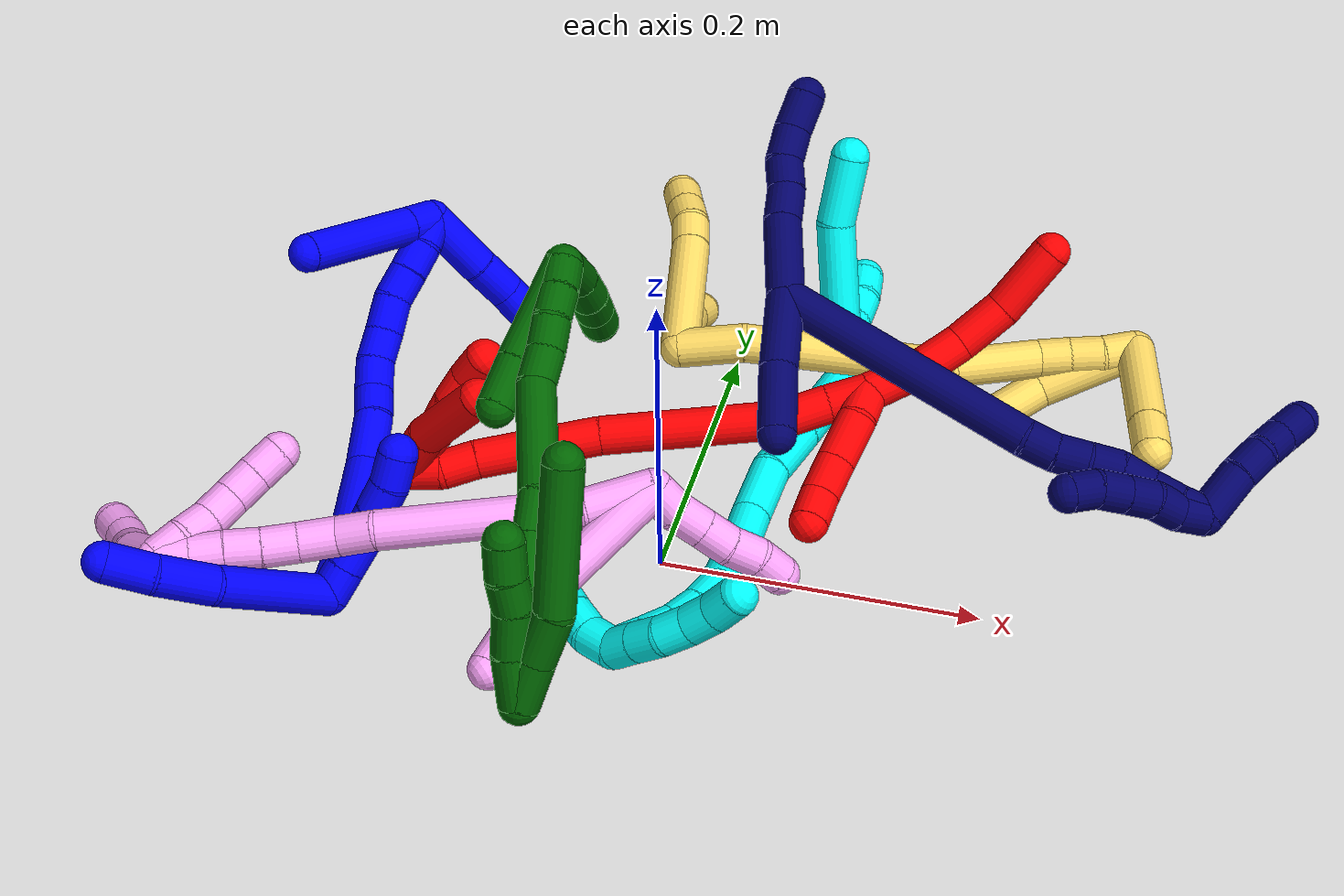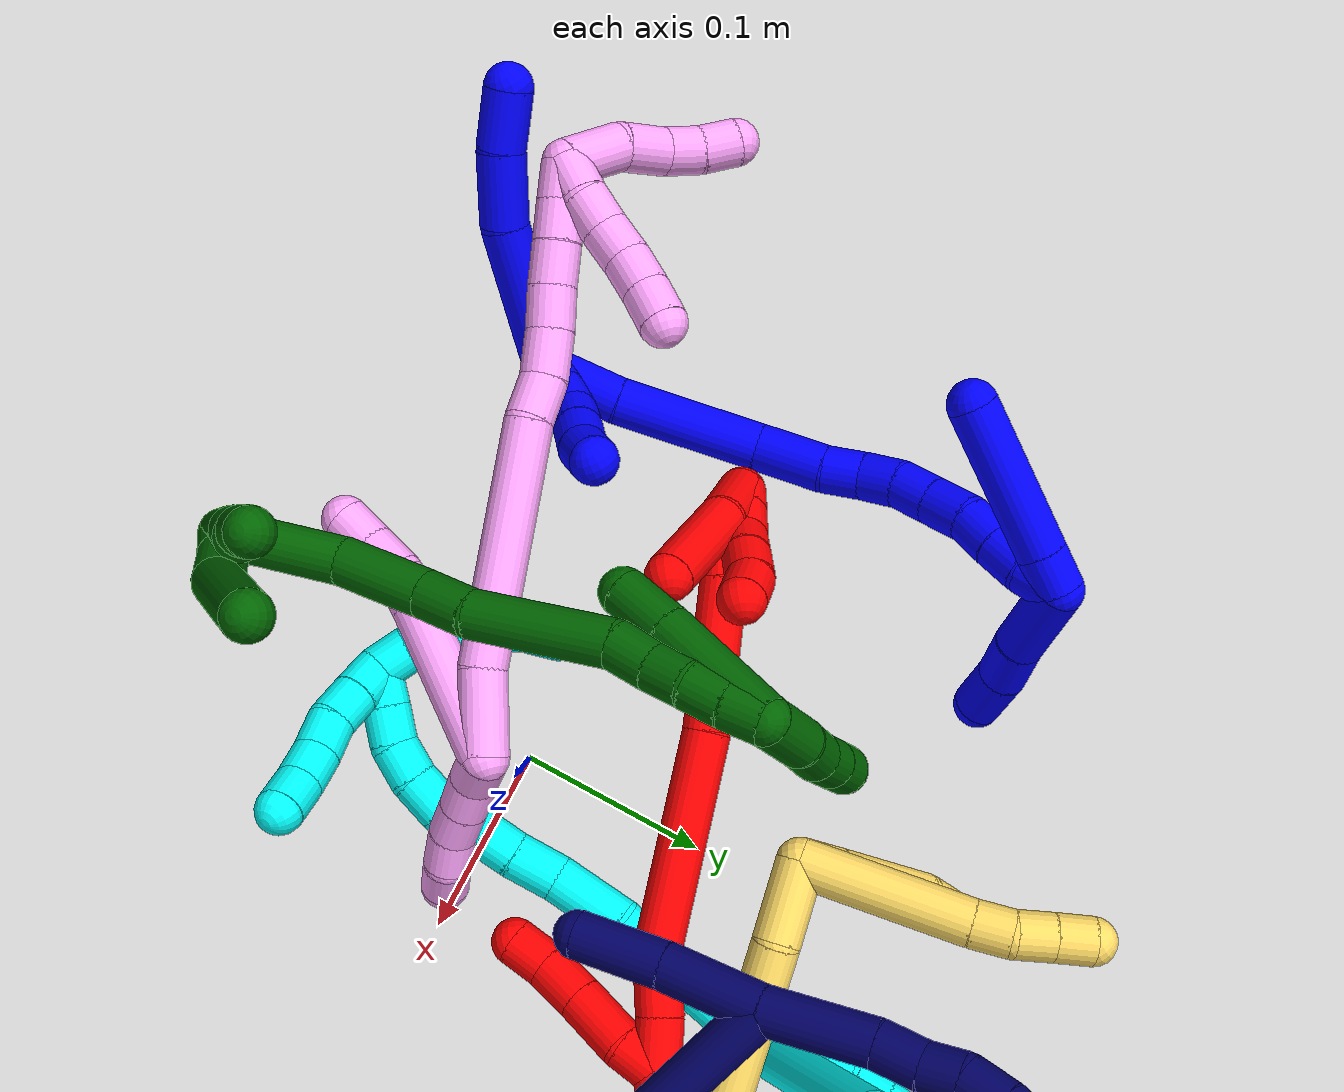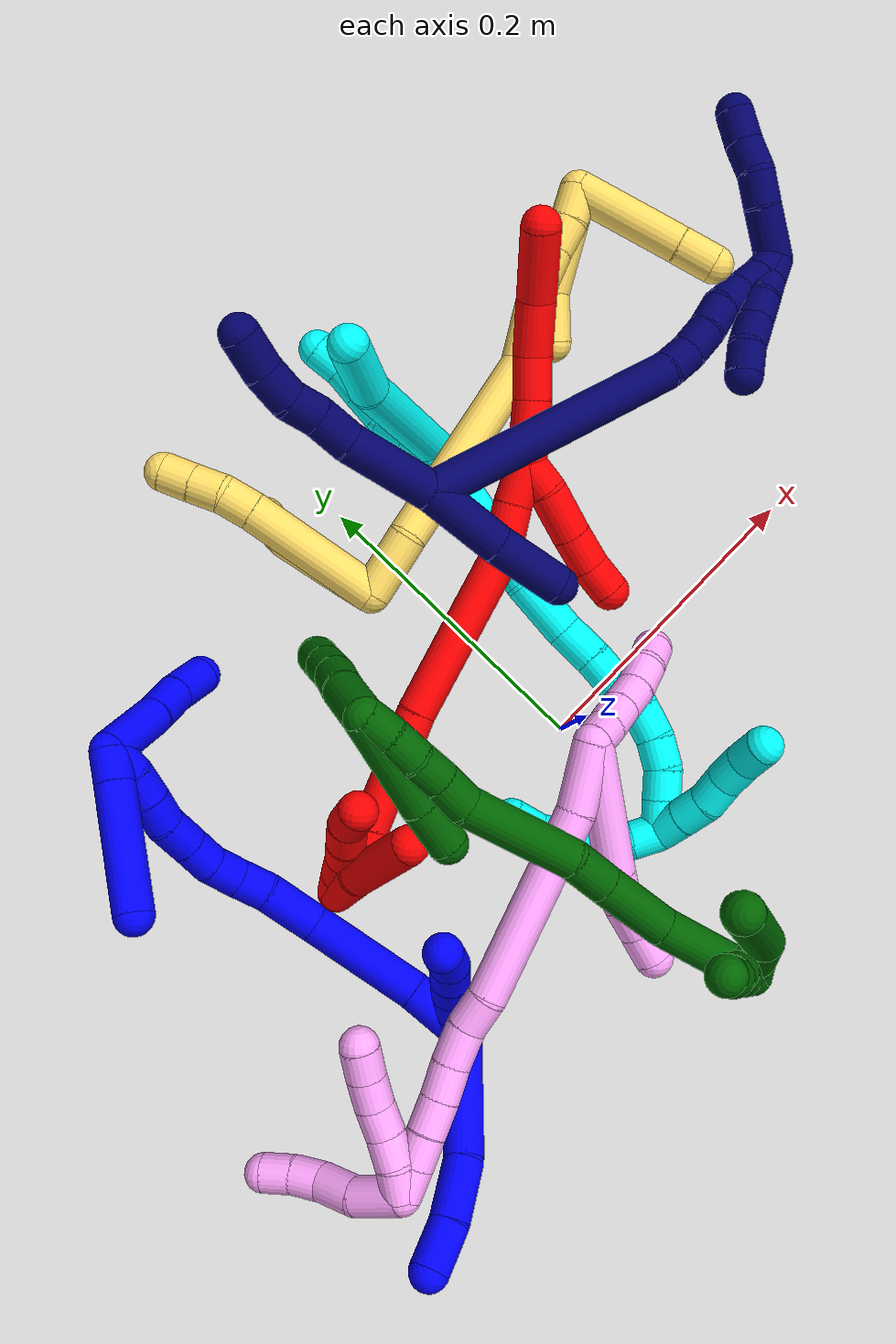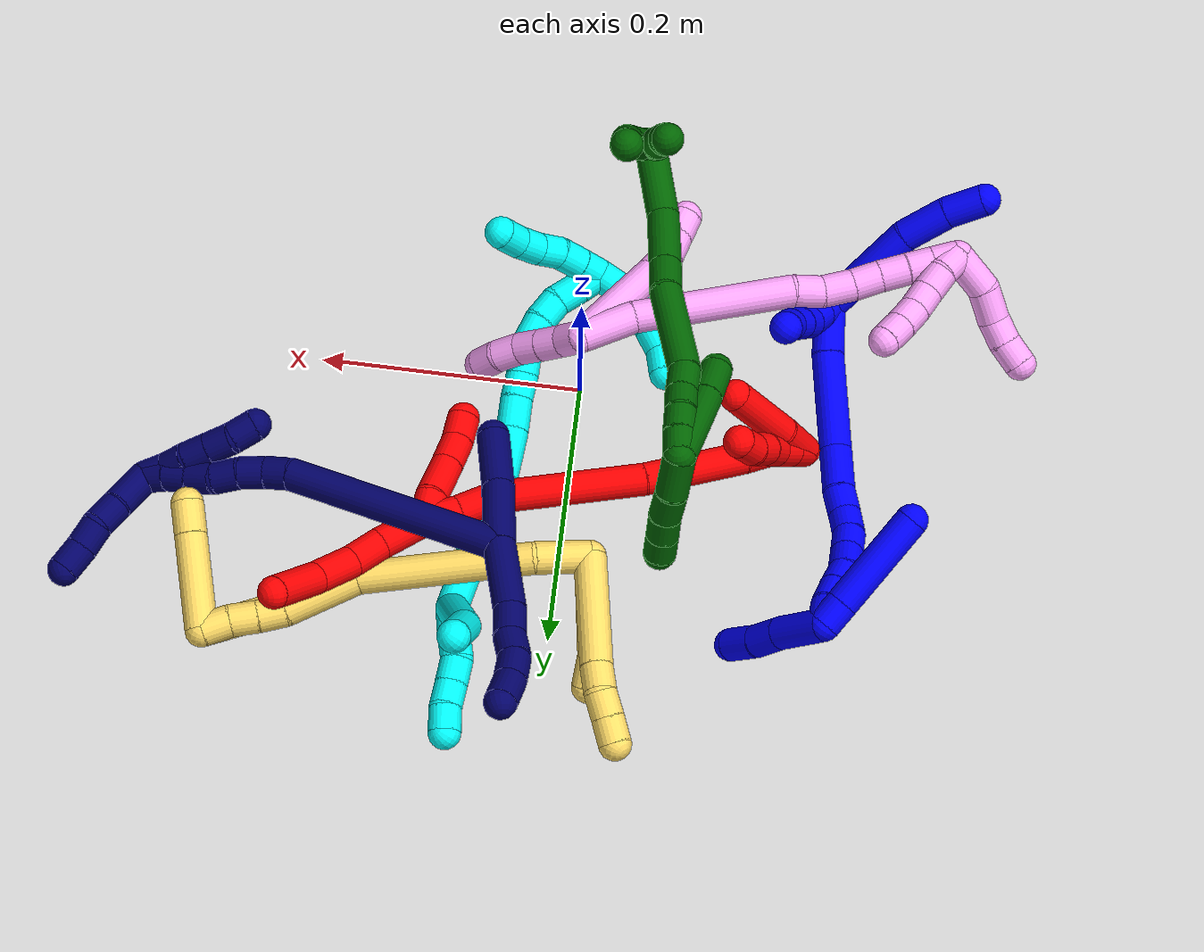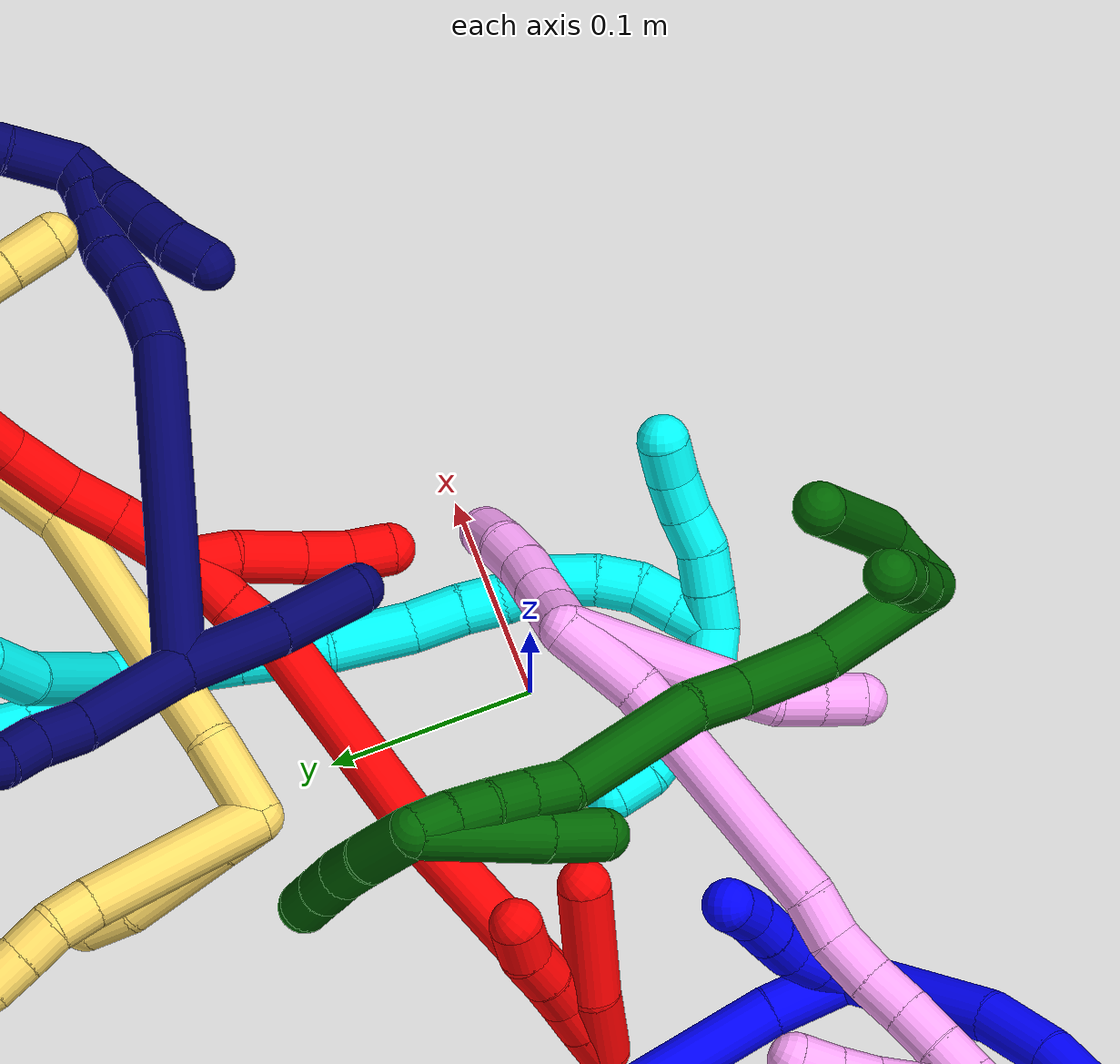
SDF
<sdf version="1.7">
 <world name="default">
  <plugin name="TubeGeneratorPlugin" filename="libtube_generator_plugin.so"/>
  <model name="photoneo_s_sensor">
   <static>1</static>
   <pose>0 0 2 1.57079 1.57079 3.14159</pose>
   <link name="link">
    <inertial><mass>0.1</mass></inertial>
    <sensor name="sensor" type="depth">
     <update_rate>30</update_rate>
     <camera>
      <horizontal_fov>1.22</horizontal_fov>
      <image><width>1920</width><height>1200</height><format>B8G8R8</format></image>
      <clip><near>0.1</near><far>4</far></clip>
      <depth_camera><output>points</output></depth_camera>
     </camera>
     <plugin name="camera_plugin" filename="libgazebo_ros_depth_camera.so">
      <baseline>0.2</baseline>
      <alwaysOn>1</alwaysOn>
      <updateRate>0.0</updateRate>
      <cameraName>camera_ir</cameraName>
      <imageTopicName>/camera/color/image_raw</imageTopicName>
      <cameraInfoTopicName>/camera/color/camera_info</cameraInfoTopicName>
      <depthImageTopicName>/camera/depth/image_raw</depthImageTopicName>
      <depthImageCameraInfoTopicName>/camera/depth/camera_info</depthImageCameraInfoTopicName>
      <pointCloudTopicName>/camera/depth/points</pointCloudTopicName>
      <frameName>fr_optical</frameName>
      <pointCloudCutoff>0.1</pointCloudCutoff>
      <pointCloudCutoffMax>2.0</pointCloudCutoffMax>
      <distortionK1>0</distortionK1>
      <distortionK2>0</distortionK2>
      <distortionK3>0</distortionK3>
      <distortionT1>0</distortionT1>
      <distortionT2>0</distortionT2>
      <CxPrime>0</CxPrime>
      <Cx>0</Cx>
      <Cy>0</Cy>
      <focalLength>0</focalLength>
      <hackBaseline>0</hackBaseline>
     </plugin>
    </sensor>
   </link>
  </model>
  <gravity>0 0 -9.8</gravity>
  <magnetic_field>6e-06 2.3e-05 -4.2e-05</magnetic_field>
  <atmosphere type="adiabatic"/>
  <physics name="default_physics" default="0" type="ode">
   <max_step_size>0.003</max_step_size>
   <real_time_factor>1</real_time_factor>
   <real_time_update_rate>1000</real_time_update_rate>
   <max_contacts>10000</max_contacts>
   <ode>
    <solver>
     <type>quick</type>
     <iters>100</iters>
     <sor>1.3</sor>
     <use_dynamic_moi_rescaling>0</use_dynamic_moi_rescaling>
    </solver>
    <constraints>
     <contact_max_correcting_vel>0</contact_max_correcting_vel>
     <contact_surface_layer>0.001</contact_surface_layer>
     <cfm>0</cfm>
     <erp>0.2</erp>
    </constraints>
   </ode>
  </physics>
  <scene><ambient>0.4 0.4 0.4 1</ambient><background>0.7 0.7 0.7 1</background><shadows>0</shadows></scene>
  <audio><device>default</device></audio>
  <spherical_coordinates>
   <surface_model>EARTH_WGS84</surface_model>
   <latitude_deg>0</latitude_deg>
   <longitude_deg>0</longitude_deg>
   <elevation>0</elevation>
   <heading_deg>0</heading_deg>
  </spherical_coordinates>
  <model name="bin">
   <static>1</static>
   <link name="bottom">
    <collision name="collision-bottom">
     <pose>0 0 -0.01 0 -0 0</pose>
     <geometry><box><size>0.8 0.6 0.02</size></box></geometry>
     <surface>
      <friction><ode><mu>100</mu><mu2>100</mu2></ode></friction>
      <contact><collide_bitmask>65535</collide_bitmask></contact>
     </surface>
    </collision>
   </link>
   <link name="west_wall">
    <collision name="collision-west_wall">
     <pose>-0.41 0 0.1 0 -0 0</pose>
     <geometry><box><size>0.02 0.6 0.2</size></box></geometry>
     <surface>
      <friction><ode><mu>100</mu><mu2>100</mu2></ode></friction>
      <contact><collide_bitmask>65535</collide_bitmask></contact>
     </surface>
    </collision>
   </link>
   <link name="east_wall">
    <collision name="collision-east_wall">
     <pose>0.41 0 0.1 0 -0 0</pose>
     <geometry><box><size>0.02 0.6 0.2</size></box></geometry>
     <surface>
      <friction><ode><mu>100</mu><mu2>100</mu2></ode></friction>
      <contact><collide_bitmask>65535</collide_bitmask></contact>
     </surface>
    </collision>
   </link>
   <link name="south_wall">
    <collision name="collision-south_wall">
     <pose>0 -0.31 0.1 0 -0 0</pose>
     <geometry><box><size>0.8 0.02 0.2</size></box></geometry>
     <surface>
      <friction><ode><mu>100</mu><mu2>100</mu2></ode></friction>
      <contact><collide_bitmask>65535</collide_bitmask></contact>
     </surface>
    </collision>
   </link>
   <link name="north_wall">
    <collision name="collision-north_wall">
     <pose>0 0.31 0.1 0 -0 0</pose>
     <geometry><box><size>0.8 0.02 0.2</size></box></geometry>
     <surface>
      <friction><ode><mu>100</mu><mu2>100</mu2></ode></friction>
      <contact><collide_bitmask>65535</collide_bitmask></contact>
     </surface>
    </collision>
   </link>
  </model>
  <model name="1">
   <static>0</static>
   <link name="1">
    <collision name="collision-cylinder-e_1_2_8">
     <pose>0.00278 0.004993 -0.040425 -3.0187 0.068136 -1.01178</pose>
     <geometry><cylinder><radius>0.0125</radius><length>0.081654</length></cylinder></geometry>
     <surface>
      <friction><ode><mu>1.16</mu><mu2>1.16</mu2><slip1>0</slip1><slip2>0</slip2></ode></friction>
      <contact><ode><kp>1e+06</kp><kd>1</kd><max_vel>0</max_vel><min_depth>0.001</min_depth></ode></contact>
     </surface>
    </collision>
    <visual name="visual-cylinder-e_1_2_8">
     <pose>0.00278 0.004993 -0.040425 -3.0187 0.068136 -1.01178</pose>
     <geometry><cylinder><radius>0.0125</radius><length>0.081654</length></cylinder></geometry>
     <material><ambient>0 0 1 1</ambient></material>
    </visual>
    <collision name="collision-cylinder-e_2_8_9">
     <pose>0.009618 0.01579 -0.098448 -2.823 0.21564 -1.18576</pose>
     <geometry><cylinder><radius>0.0125</radius><length>0.037938</length></cylinder></geometry>
     <surface>
      <friction><ode><mu>1.16</mu><mu2>1.16</mu2><slip1>0</slip1><slip2>0</slip2></ode></friction>
      <contact><ode><kp>1e+06</kp><kd>1</kd><max_vel>0</max_vel><min_depth>0.001</min_depth></ode></contact>
     </surface>
    </collision>
    <visual name="visual-cylinder-e_2_8_9">
     <pose>0.009618 0.01579 -0.098448 -2.823 0.21564 -1.18576</pose>
     <geometry><cylinder><radius>0.0125</radius><length>0.037938</length></cylinder></geometry>
     <material><ambient>0 0 1 1</ambient></material>
    </visual>
    <collision name="collision-cylinder-e_3_9_6">
     <pose>0.018261 0.028159 -0.128969 -2.67159 0.306284 -1.14524</pose>
     <geometry><cylinder><radius>0.0125</radius><length>0.030408</length></cylinder></geometry>
     <surface>
      <friction><ode><mu>1.16</mu><mu2>1.16</mu2><slip1>0</slip1><slip2>0</slip2></ode></friction>
      <contact><ode><kp>1e+06</kp><kd>1</kd><max_vel>0</max_vel><min_depth>0.001</min_depth></ode></contact>
     </surface>
    </collision>
    <visual name="visual-cylinder-e_3_9_6">
     <pose>0.018261 0.028159 -0.128969 -2.67159 0.306284 -1.14524</pose>
     <geometry><cylinder><radius>0.0125</radius><length>0.030408</length></cylinder></geometry>
     <material><ambient>0 0 1 1</ambient></material>
    </visual>
    <collision name="collision-cylinder-e_1_2_10">
     <pose>-0.007935 0.005463 0.002682 -1.11432 -0.916551 0.596333</pose>
     <geometry><cylinder><radius>0.0125</radius><length>0.02</length></cylinder></geometry>
     <surface>
      <friction><ode><mu>1.16</mu><mu2>1.16</mu2><slip1>0</slip1><slip2>0</slip2></ode></friction>
      <contact><ode><kp>1e+06</kp><kd>1</kd><max_vel>0</max_vel><min_depth>0.001</min_depth></ode></contact>
     </surface>
    </collision>
    <visual name="visual-cylinder-e_1_2_10">
     <pose>-0.007935 0.005463 0.002682 -1.11432 -0.916551 0.596333</pose>
     <geometry><cylinder><radius>0.0125</radius><length>0.02</length></cylinder></geometry>
     <material><ambient>0 0 1 1</ambient></material>
    </visual>
    <collision name="collision-cylinder-e_2_10_11">
     <pose>-0.023918 0.016291 0.007902 -1.1292 -0.935363 0.619202</pose>
     <geometry><cylinder><radius>0.0125</radius><length>0.02</length></cylinder></geometry>
     <surface>
      <friction><ode><mu>1.16</mu><mu2>1.16</mu2><slip1>0</slip1><slip2>0</slip2></ode></friction>
      <contact><ode><kp>1e+06</kp><kd>1</kd><max_vel>0</max_vel><min_depth>0.001</min_depth></ode></contact>
     </surface>
    </collision>
    <visual name="visual-cylinder-e_2_10_11">
     <pose>-0.023918 0.016291 0.007902 -1.1292 -0.935363 0.619202</pose>
     <geometry><cylinder><radius>0.0125</radius><length>0.02</length></cylinder></geometry>
     <material><ambient>0 0 1 1</ambient></material>
    </visual>
    <collision name="collision-cylinder-e_3_11_12">
     <pose>-0.040842 0.026264 0.01045 -1.56813 -1.09202 1.08965</pose>
     <geometry><cylinder><radius>0.0125</radius><length>0.02</length></cylinder></geometry>
     <surface>
      <friction><ode><mu>1.16</mu><mu2>1.16</mu2><slip1>0</slip1><slip2>0</slip2></ode></friction>
      <contact><ode><kp>1e+06</kp><kd>1</kd><max_vel>0</max_vel><min_depth>0.001</min_depth></ode></contact>
     </surface>
    </collision>
    <visual name="visual-cylinder-e_3_11_12">
     <pose>-0.040842 0.026264 0.01045 -1.56813 -1.09202 1.08965</pose>
     <geometry><cylinder><radius>0.0125</radius><length>0.02</length></cylinder></geometry>
     <material><ambient>0 0 1 1</ambient></material>
    </visual>
    <collision name="collision-cylinder-e_4_12_13">
     <pose>-0.058719 0.035216 0.010776 -1.49879 -1.12007 1.05626</pose>
     <geometry><cylinder><radius>0.0125</radius><length>0.02</length></cylinder></geometry>
     <surface>
      <friction><ode><mu>1.16</mu><mu2>1.16</mu2><slip1>0</slip1><slip2>0</slip2></ode></friction>
      <contact><ode><kp>1e+06</kp><kd>1</kd><max_vel>0</max_vel><min_depth>0.001</min_depth></ode></contact>
     </surface>
    </collision>
    <visual name="visual-cylinder-e_4_12_13">
     <pose>-0.058719 0.035216 0.010776 -1.49879 -1.12007 1.05626</pose>
     <geometry><cylinder><radius>0.0125</radius><length>0.02</length></cylinder></geometry>
     <material><ambient>0 0 1 1</ambient></material>
    </visual>
    <collision name="collision-cylinder-e_5_13_5">
     <pose>-0.075617 0.045667 0.010493 -1.66815 -0.910292 0.989562</pose>
     <geometry><cylinder><radius>0.0125</radius><length>0.02</length></cylinder></geometry>
     <surface>
      <friction><ode><mu>1.16</mu><mu2>1.16</mu2><slip1>0</slip1><slip2>0</slip2></ode></friction>
      <contact><ode><kp>1e+06</kp><kd>1</kd><max_vel>0</max_vel><min_depth>0.001</min_depth></ode></contact>
     </surface>
    </collision>
    <visual name="visual-cylinder-e_5_13_5">
     <pose>-0.075617 0.045667 0.010493 -1.66815 -0.910292 0.989562</pose>
     <geometry><cylinder><radius>0.0125</radius><length>0.02</length></cylinder></geometry>
     <material><ambient>0 0 1 1</ambient></material>
    </visual>
    <collision name="collision-cylinder-e_1_2_14">
     <pose>-0.000406 0.015433 0.012999 -0.870801 -0.020115 0.009357</pose>
     <geometry><cylinder><radius>0.0125</radius><length>0.040365</length></cylinder></geometry>
     <surface>
      <friction><ode><mu>1.16</mu><mu2>1.16</mu2><slip1>0</slip1><slip2>0</slip2></ode></friction>
      <contact><ode><kp>1e+06</kp><kd>1</kd><max_vel>0</max_vel><min_depth>0.001</min_depth></ode></contact>
     </surface>
    </collision>
    <visual name="visual-cylinder-e_1_2_14">
     <pose>-0.000406 0.015433 0.012999 -0.870801 -0.020115 0.009357</pose>
     <geometry><cylinder><radius>0.0125</radius><length>0.040365</length></cylinder></geometry>
     <material><ambient>0 0 1 1</ambient></material>
    </visual>
    <collision name="collision-cylinder-e_2_14_15">
     <pose>0.00207 0.061515 0.048839 -0.930355 0.075247 -0.037781</pose>
     <geometry><cylinder><radius>0.0125</radius><length>0.076663</length></cylinder></geometry>
     <surface>
      <friction><ode><mu>1.16</mu><mu2>1.16</mu2><slip1>0</slip1><slip2>0</slip2></ode></friction>
      <contact><ode><kp>1e+06</kp><kd>1</kd><max_vel>0</max_vel><min_depth>0.001</min_depth></ode></contact>
     </surface>
    </collision>
    <visual name="visual-cylinder-e_2_14_15">
     <pose>0.00207 0.061515 0.048839 -0.930355 0.075247 -0.037781</pose>
     <geometry><cylinder><radius>0.0125</radius><length>0.076663</length></cylinder></geometry>
     <material><ambient>0 0 1 1</ambient></material>
    </visual>
    <collision name="collision-cylinder-e_3_15_16">
     <pose>0.001598 0.108796 0.079638 -1.12446 -0.179877 0.113518</pose>
     <geometry><cylinder><radius>0.0125</radius><length>0.037482</length></cylinder></geometry>
     <surface>
      <friction><ode><mu>1.16</mu><mu2>1.16</mu2><slip1>0</slip1><slip2>0</slip2></ode></friction>
      <contact><ode><kp>1e+06</kp><kd>1</kd><max_vel>0</max_vel><min_depth>0.001</min_depth></ode></contact>
     </surface>
    </collision>
    <visual name="visual-cylinder-e_3_15_16">
     <pose>0.001598 0.108796 0.079638 -1.12446 -0.179877 0.113518</pose>
     <geometry><cylinder><radius>0.0125</radius><length>0.037482</length></cylinder></geometry>
     <material><ambient>0 0 1 1</ambient></material>
    </visual>
    <collision name="collision-cylinder-e_4_16_17">
     <pose>-0.00199 0.134981 0.091479 -1.18484 -0.022885 0.015404</pose>
     <geometry><cylinder><radius>0.0125</radius><length>0.020628</length></cylinder></geometry>
     <surface>
      <friction><ode><mu>1.16</mu><mu2>1.16</mu2><slip1>0</slip1><slip2>0</slip2></ode></friction>
      <contact><ode><kp>1e+06</kp><kd>1</kd><max_vel>0</max_vel><min_depth>0.001</min_depth></ode></contact>
     </surface>
    </collision>
    <visual name="visual-cylinder-e_4_16_17">
     <pose>-0.00199 0.134981 0.091479 -1.18484 -0.022885 0.015404</pose>
     <geometry><cylinder><radius>0.0125</radius><length>0.020628</length></cylinder></geometry>
     <material><ambient>0 0 1 1</ambient></material>
    </visual>
    <collision name="collision-cylinder-e_5_17_18">
     <pose>-0.004984 0.15428 0.097842 -1.32155 -0.26761 0.208517</pose>
     <geometry><cylinder><radius>0.0125</radius><length>0.020855</length></cylinder></geometry>
     <surface>
      <friction><ode><mu>1.16</mu><mu2>1.16</mu2><slip1>0</slip1><slip2>0</slip2></ode></friction>
      <contact><ode><kp>1e+06</kp><kd>1</kd><max_vel>0</max_vel><min_depth>0.001</min_depth></ode></contact>
     </surface>
    </collision>
    <visual name="visual-cylinder-e_5_17_18">
     <pose>-0.004984 0.15428 0.097842 -1.32155 -0.26761 0.208517</pose>
     <geometry><cylinder><radius>0.0125</radius><length>0.020855</length></cylinder></geometry>
     <material><ambient>0 0 1 1</ambient></material>
    </visual>
    <collision name="collision-cylinder-e_6_18_19">
     <pose>-0.012333 0.172453 0.103892 -1.17009 -0.465022 0.31117</pose>
     <geometry><cylinder><radius>0.0125</radius><length>0.020479</length></cylinder></geometry>
     <surface>
      <friction><ode><mu>1.16</mu><mu2>1.16</mu2><slip1>0</slip1><slip2>0</slip2></ode></friction>
      <contact><ode><kp>1e+06</kp><kd>1</kd><max_vel>0</max_vel><min_depth>0.001</min_depth></ode></contact>
     </surface>
    </collision>
    <visual name="visual-cylinder-e_6_18_19">
     <pose>-0.012333 0.172453 0.103892 -1.17009 -0.465022 0.31117</pose>
     <geometry><cylinder><radius>0.0125</radius><length>0.020479</length></cylinder></geometry>
     <material><ambient>0 0 1 1</ambient></material>
    </visual>
    <collision name="collision-cylinder-e_7_19_20">
     <pose>-0.022858 0.190302 0.110405 -1.26802 -0.541211 0.402427</pose>
     <geometry><cylinder><radius>0.0125</radius><length>0.023033</length></cylinder></geometry>
     <surface>
      <friction><ode><mu>1.16</mu><mu2>1.16</mu2><slip1>0</slip1><slip2>0</slip2></ode></friction>
      <contact><ode><kp>1e+06</kp><kd>1</kd><max_vel>0</max_vel><min_depth>0.001</min_depth></ode></contact>
     </surface>
    </collision>
    <visual name="visual-cylinder-e_7_19_20">
     <pose>-0.022858 0.190302 0.110405 -1.26802 -0.541211 0.402427</pose>
     <geometry><cylinder><radius>0.0125</radius><length>0.023033</length></cylinder></geometry>
     <material><ambient>0 0 1 1</ambient></material>
    </visual>
    <collision name="collision-cylinder-e_8_20_21">
     <pose>-0.035201 0.206368 0.117618 -0.999703 -0.681776 0.382709</pose>
     <geometry><cylinder><radius>0.0125</radius><length>0.020345</length></cylinder></geometry>
     <surface>
      <friction><ode><mu>1.16</mu><mu2>1.16</mu2><slip1>0</slip1><slip2>0</slip2></ode></friction>
      <contact><ode><kp>1e+06</kp><kd>1</kd><max_vel>0</max_vel><min_depth>0.001</min_depth></ode></contact>
     </surface>
    </collision>
    <visual name="visual-cylinder-e_8_20_21">
     <pose>-0.035201 0.206368 0.117618 -0.999703 -0.681776 0.382709</pose>
     <geometry><cylinder><radius>0.0125</radius><length>0.020345</length></cylinder></geometry>
     <material><ambient>0 0 1 1</ambient></material>
    </visual>
    <collision name="collision-cylinder-e_9_21_22">
     <pose>-0.047493 0.21985 0.126254 -1.00239 -0.62736 0.351763</pose>
     <geometry><cylinder><radius>0.0125</radius><length>0.02004</length></cylinder></geometry>
     <surface>
      <friction><ode><mu>1.16</mu><mu2>1.16</mu2><slip1>0</slip1><slip2>0</slip2></ode></friction>
      <contact><ode><kp>1e+06</kp><kd>1</kd><max_vel>0</max_vel><min_depth>0.001</min_depth></ode></contact>
     </surface>
    </collision>
    <visual name="visual-cylinder-e_9_21_22">
     <pose>-0.047493 0.21985 0.126254 -1.00239 -0.62736 0.351763</pose>
     <geometry><cylinder><radius>0.0125</radius><length>0.02004</length></cylinder></geometry>
     <material><ambient>0 0 1 1</ambient></material>
    </visual>
    <collision name="collision-cylinder-e_10_22_1">
     <pose>-0.057771 0.234693 0.134823 -1.08746 -0.452529 0.276549</pose>
     <geometry><cylinder><radius>0.0125</radius><length>0.02011</length></cylinder></geometry>
     <surface>
      <friction><ode><mu>1.16</mu><mu2>1.16</mu2><slip1>0</slip1><slip2>0</slip2></ode></friction>
      <contact><ode><kp>1e+06</kp><kd>1</kd><max_vel>0</max_vel><min_depth>0.001</min_depth></ode></contact>
     </surface>
    </collision>
    <visual name="visual-cylinder-e_10_22_1">
     <pose>-0.057771 0.234693 0.134823 -1.08746 -0.452529 0.276549</pose>
     <geometry><cylinder><radius>0.0125</radius><length>0.02011</length></cylinder></geometry>
     <material><ambient>0 0 1 1</ambient></material>
    </visual>
    <collision name="collision-cylinder-e_1_1_23">
     <pose>-0.059451 0.240661 0.129182 2.93732 0.263979 1.82672</pose>
     <geometry><cylinder><radius>0.0125</radius><length>0.020827</length></cylinder></geometry>
     <surface>
      <friction><ode><mu>1.16</mu><mu2>1.16</mu2><slip1>0</slip1><slip2>0</slip2></ode></friction>
      <contact><ode><kp>1e+06</kp><kd>1</kd><max_vel>0</max_vel><min_depth>0.001</min_depth></ode></contact>
     </surface>
    </collision>
    <visual name="visual-cylinder-e_1_1_23">
     <pose>-0.059451 0.240661 0.129182 2.93732 0.263979 1.82672</pose>
     <geometry><cylinder><radius>0.0125</radius><length>0.020827</length></cylinder></geometry>
     <material><ambient>0 0 1 1</ambient></material>
    </visual>
    <collision name="collision-cylinder-e_2_23_4">
     <pose>-0.046878 0.231202 0.081722 2.94685 0.251601 1.82625</pose>
     <geometry><cylinder><radius>0.0125</radius><length>0.079173</length></cylinder></geometry>
     <surface>
      <friction><ode><mu>1.16</mu><mu2>1.16</mu2><slip1>0</slip1><slip2>0</slip2></ode></friction>
      <contact><ode><kp>1e+06</kp><kd>1</kd><max_vel>0</max_vel><min_depth>0.001</min_depth></ode></contact>
     </surface>
    </collision>
    <visual name="visual-cylinder-e_2_23_4">
     <pose>-0.046878 0.231202 0.081722 2.94685 0.251601 1.82625</pose>
     <geometry><cylinder><radius>0.0125</radius><length>0.079173</length></cylinder></geometry>
     <material><ambient>0 0 1 1</ambient></material>
    </visual>
    <collision name="collision-cylinder-e_1_1_24">
     <pose>-0.059631 0.227699 0.155776 0.730366 0.112343 0.042991</pose>
     <geometry><cylinder><radius>0.0125</radius><length>0.045257</length></cylinder></geometry>
     <surface>
      <friction><ode><mu>1.16</mu><mu2>1.16</mu2><slip1>0</slip1><slip2>0</slip2></ode></friction>
      <contact><ode><kp>1e+06</kp><kd>1</kd><max_vel>0</max_vel><min_depth>0.001</min_depth></ode></contact>
     </surface>
    </collision>
    <visual name="visual-cylinder-e_1_1_24">
     <pose>-0.059631 0.227699 0.155776 0.730366 0.112343 0.042991</pose>
     <geometry><cylinder><radius>0.0125</radius><length>0.045257</length></cylinder></geometry>
     <material><ambient>0 0 1 1</ambient></material>
    </visual>
    <collision name="collision-cylinder-e_2_24_25">
     <pose>-0.055297 0.204926 0.183145 0.631801 0.135761 0.044434</pose>
     <geometry><cylinder><radius>0.0125</radius><length>0.026562</length></cylinder></geometry>
     <surface>
      <friction><ode><mu>1.16</mu><mu2>1.16</mu2><slip1>0</slip1><slip2>0</slip2></ode></friction>
      <contact><ode><kp>1e+06</kp><kd>1</kd><max_vel>0</max_vel><min_depth>0.001</min_depth></ode></contact>
     </surface>
    </collision>
    <visual name="visual-cylinder-e_2_24_25">
     <pose>-0.055297 0.204926 0.183145 0.631801 0.135761 0.044434</pose>
     <geometry><cylinder><radius>0.0125</radius><length>0.026562</length></cylinder></geometry>
     <material><ambient>0 0 1 1</ambient></material>
    </visual>
    <collision name="collision-cylinder-e_3_25_3">
     <pose>-0.051792 0.187392 0.20378 0.772576 0.121438 0.049442</pose>
     <geometry><cylinder><radius>0.0125</radius><length>0.028181</length></cylinder></geometry>
     <surface>
      <friction><ode><mu>1.16</mu><mu2>1.16</mu2><slip1>0</slip1><slip2>0</slip2></ode></friction>
      <contact><ode><kp>1e+06</kp><kd>1</kd><max_vel>0</max_vel><min_depth>0.001</min_depth></ode></contact>
     </surface>
    </collision>
    <visual name="visual-cylinder-e_3_25_3">
     <pose>-0.051792 0.187392 0.20378 0.772576 0.121438 0.049442</pose>
     <geometry><cylinder><radius>0.0125</radius><length>0.028181</length></cylinder></geometry>
     <material><ambient>0 0 1 1</ambient></material>
    </visual>
    <collision name="collision-sphere-3">
     <pose>-0.050085 0.177629 0.213796 0 -0 0</pose>
     <geometry><sphere><radius>0.0125</radius></sphere></geometry>
     <surface>
      <friction><ode><mu>1.16</mu><mu2>1.16</mu2><slip1>0</slip1><slip2>0</slip2></ode></friction>
      <contact><ode><kp>1e+06</kp><kd>1</kd><max_vel>0</max_vel><min_depth>0.001</min_depth></ode></contact>
     </surface>
    </collision>
    <visual name="visual-sphere-3">
     <pose>-0.050085 0.177629 0.213796 0 -0 0</pose>
     <geometry><sphere><radius>0.0125</radius></sphere></geometry>
     <material><ambient>0 0 1 1</ambient></material>
    </visual>
    <collision name="collision-sphere-25">
     <pose>-0.053499 0.197154 0.193764 0 -0 0</pose>
     <geometry><sphere><radius>0.0125</radius></sphere></geometry>
     <surface>
      <friction><ode><mu>1.16</mu><mu2>1.16</mu2><slip1>0</slip1><slip2>0</slip2></ode></friction>
      <contact><ode><kp>1e+06</kp><kd>1</kd><max_vel>0</max_vel><min_depth>0.001</min_depth></ode></contact>
     </surface>
    </collision>
    <visual name="visual-sphere-25">
     <pose>-0.053499 0.197154 0.193764 0 -0 0</pose>
     <geometry><sphere><radius>0.0125</radius></sphere></geometry>
     <material><ambient>0 0 1 1</ambient></material>
    </visual>
    <collision name="collision-sphere-24">
     <pose>-0.057094 0.212697 0.172526 0 -0 0</pose>
     <geometry><sphere><radius>0.0125</radius></sphere></geometry>
     <surface>
      <friction><ode><mu>1.16</mu><mu2>1.16</mu2><slip1>0</slip1><slip2>0</slip2></ode></friction>
      <contact><ode><kp>1e+06</kp><kd>1</kd><max_vel>0</max_vel><min_depth>0.001</min_depth></ode></contact>
     </surface>
    </collision>
    <visual name="visual-sphere-24">
     <pose>-0.057094 0.212697 0.172526 0 -0 0</pose>
     <geometry><sphere><radius>0.0125</radius></sphere></geometry>
     <material><ambient>0 0 1 1</ambient></material>
    </visual>
    <collision name="collision-sphere-4">
     <pose>-0.037023 0.223783 0.044107 0 -0 0</pose>
     <geometry><sphere><radius>0.0125</radius></sphere></geometry>
     <surface>
      <friction><ode><mu>1.16</mu><mu2>1.16</mu2><slip1>0</slip1><slip2>0</slip2></ode></friction>
      <contact><ode><kp>1e+06</kp><kd>1</kd><max_vel>0</max_vel><min_depth>0.001</min_depth></ode></contact>
     </surface>
    </collision>
    <visual name="visual-sphere-4">
     <pose>-0.037023 0.223783 0.044107 0 -0 0</pose>
     <geometry><sphere><radius>0.0125</radius></sphere></geometry>
     <material><ambient>0 0 1 1</ambient></material>
    </visual>
    <collision name="collision-sphere-23">
     <pose>-0.056733 0.238621 0.119338 0 -0 0</pose>
     <geometry><sphere><radius>0.0125</radius></sphere></geometry>
     <surface>
      <friction><ode><mu>1.16</mu><mu2>1.16</mu2><slip1>0</slip1><slip2>0</slip2></ode></friction>
      <contact><ode><kp>1e+06</kp><kd>1</kd><max_vel>0</max_vel><min_depth>0.001</min_depth></ode></contact>
     </surface>
    </collision>
    <visual name="visual-sphere-23">
     <pose>-0.056733 0.238621 0.119338 0 -0 0</pose>
     <geometry><sphere><radius>0.0125</radius></sphere></geometry>
     <material><ambient>0 0 1 1</ambient></material>
    </visual>
    <collision name="collision-sphere-1">
     <pose>-0.062168 0.2427 0.139026 0 -0 0</pose>
     <geometry><sphere><radius>0.0125</radius></sphere></geometry>
     <surface>
      <friction><ode><mu>1.16</mu><mu2>1.16</mu2><slip1>0</slip1><slip2>0</slip2></ode></friction>
      <contact><ode><kp>1e+06</kp><kd>1</kd><max_vel>0</max_vel><min_depth>0.001</min_depth></ode></contact>
     </surface>
    </collision>
    <visual name="visual-sphere-1">
     <pose>-0.062168 0.2427 0.139026 0 -0 0</pose>
     <geometry><sphere><radius>0.0125</radius></sphere></geometry>
     <material><ambient>0 0 1 1</ambient></material>
    </visual>
    <collision name="collision-sphere-22">
     <pose>-0.053375 0.226686 0.130621 0 -0 0</pose>
     <geometry><sphere><radius>0.0125</radius></sphere></geometry>
     <surface>
      <friction><ode><mu>1.16</mu><mu2>1.16</mu2><slip1>0</slip1><slip2>0</slip2></ode></friction>
      <contact><ode><kp>1e+06</kp><kd>1</kd><max_vel>0</max_vel><min_depth>0.001</min_depth></ode></contact>
     </surface>
    </collision>
    <visual name="visual-sphere-22">
     <pose>-0.053375 0.226686 0.130621 0 -0 0</pose>
     <geometry><sphere><radius>0.0125</radius></sphere></geometry>
     <material><ambient>0 0 1 1</ambient></material>
    </visual>
    <collision name="collision-sphere-21">
     <pose>-0.041611 0.213013 0.121887 0 -0 0</pose>
     <geometry><sphere><radius>0.0125</radius></sphere></geometry>
     <surface>
      <friction><ode><mu>1.16</mu><mu2>1.16</mu2><slip1>0</slip1><slip2>0</slip2></ode></friction>
      <contact><ode><kp>1e+06</kp><kd>1</kd><max_vel>0</max_vel><min_depth>0.001</min_depth></ode></contact>
     </surface>
    </collision>
    <visual name="visual-sphere-21">
     <pose>-0.041611 0.213013 0.121887 0 -0 0</pose>
     <geometry><sphere><radius>0.0125</radius></sphere></geometry>
     <material><ambient>0 0 1 1</ambient></material>
    </visual>
    <collision name="collision-sphere-11">
     <pose>-0.031966 0.021657 0.010438 0 -0 0</pose>
     <geometry><sphere><radius>0.0125</radius></sphere></geometry>
     <surface>
      <friction><ode><mu>1.16</mu><mu2>1.16</mu2><slip1>0</slip1><slip2>0</slip2></ode></friction>
      <contact><ode><kp>1e+06</kp><kd>1</kd><max_vel>0</max_vel><min_depth>0.001</min_depth></ode></contact>
     </surface>
    </collision>
    <visual name="visual-sphere-11">
     <pose>-0.031966 0.021657 0.010438 0 -0 0</pose>
     <geometry><sphere><radius>0.0125</radius></sphere></geometry>
     <material><ambient>0 0 1 1</ambient></material>
    </visual>
    <collision name="collision-sphere-10">
     <pose>-0.01587 0.010925 0.005365 0 -0 0</pose>
     <geometry><sphere><radius>0.0125</radius></sphere></geometry>
     <surface>
      <friction><ode><mu>1.16</mu><mu2>1.16</mu2><slip1>0</slip1><slip2>0</slip2></ode></friction>
      <contact><ode><kp>1e+06</kp><kd>1</kd><max_vel>0</max_vel><min_depth>0.001</min_depth></ode></contact>
     </surface>
    </collision>
    <visual name="visual-sphere-10">
     <pose>-0.01587 0.010925 0.005365 0 -0 0</pose>
     <geometry><sphere><radius>0.0125</radius></sphere></geometry>
     <material><ambient>0 0 1 1</ambient></material>
    </visual>
    <collision name="collision-sphere-6">
     <pose>0.022845 0.034724 -0.141894 0 -0 0</pose>
     <geometry><sphere><radius>0.0125</radius></sphere></geometry>
     <surface>
      <friction><ode><mu>1.16</mu><mu2>1.16</mu2><slip1>0</slip1><slip2>0</slip2></ode></friction>
      <contact><ode><kp>1e+06</kp><kd>1</kd><max_vel>0</max_vel><min_depth>0.001</min_depth></ode></contact>
     </surface>
    </collision>
    <visual name="visual-sphere-6">
     <pose>0.022845 0.034724 -0.141894 0 -0 0</pose>
     <geometry><sphere><radius>0.0125</radius></sphere></geometry>
     <material><ambient>0 0 1 1</ambient></material>
    </visual>
    <collision name="collision-sphere-9">
     <pose>0.013677 0.021594 -0.116045 0 -0 0</pose>
     <geometry><sphere><radius>0.0125</radius></sphere></geometry>
     <surface>
      <friction><ode><mu>1.16</mu><mu2>1.16</mu2><slip1>0</slip1><slip2>0</slip2></ode></friction>
      <contact><ode><kp>1e+06</kp><kd>1</kd><max_vel>0</max_vel><min_depth>0.001</min_depth></ode></contact>
     </surface>
    </collision>
    <visual name="visual-sphere-9">
     <pose>0.013677 0.021594 -0.116045 0 -0 0</pose>
     <geometry><sphere><radius>0.0125</radius></sphere></geometry>
     <material><ambient>0 0 1 1</ambient></material>
    </visual>
    <collision name="collision-sphere-2">
     <geometry><sphere><radius>0.0125</radius></sphere></geometry>
     <surface>
      <friction><ode><mu>1.16</mu><mu2>1.16</mu2><slip1>0</slip1><slip2>0</slip2></ode></friction>
      <contact><ode><kp>1e+06</kp><kd>1</kd><max_vel>0</max_vel><min_depth>0.001</min_depth></ode></contact>
     </surface>
    </collision>
    <visual name="visual-sphere-2">
     <geometry><sphere><radius>0.0125</radius></sphere></geometry>
     <material><ambient>0 0 1 1</ambient></material>
    </visual>
    <collision name="collision-sphere-19">
     <pose>-0.016925 0.18088 0.107462 0 -0 0</pose>
     <geometry><sphere><radius>0.0125</radius></sphere></geometry>
     <surface>
      <friction><ode><mu>1.16</mu><mu2>1.16</mu2><slip1>0</slip1><slip2>0</slip2></ode></friction>
      <contact><ode><kp>1e+06</kp><kd>1</kd><max_vel>0</max_vel><min_depth>0.001</min_depth></ode></contact>
     </surface>
    </collision>
    <visual name="visual-sphere-19">
     <pose>-0.016925 0.18088 0.107462 0 -0 0</pose>
     <geometry><sphere><radius>0.0125</radius></sphere></geometry>
     <material><ambient>0 0 1 1</ambient></material>
    </visual>
    <collision name="collision-sphere-8">
     <pose>0.005559 0.009986 -0.080851 0 -0 0</pose>
     <geometry><sphere><radius>0.0125</radius></sphere></geometry>
     <surface>
      <friction><ode><mu>1.16</mu><mu2>1.16</mu2><slip1>0</slip1><slip2>0</slip2></ode></friction>
      <contact><ode><kp>1e+06</kp><kd>1</kd><max_vel>0</max_vel><min_depth>0.001</min_depth></ode></contact>
     </surface>
    </collision>
    <visual name="visual-sphere-8">
     <pose>0.005559 0.009986 -0.080851 0 -0 0</pose>
     <geometry><sphere><radius>0.0125</radius></sphere></geometry>
     <material><ambient>0 0 1 1</ambient></material>
    </visual>
    <collision name="collision-sphere-12">
     <pose>-0.049718 0.030871 0.010463 0 -0 0</pose>
     <geometry><sphere><radius>0.0125</radius></sphere></geometry>
     <surface>
      <friction><ode><mu>1.16</mu><mu2>1.16</mu2><slip1>0</slip1><slip2>0</slip2></ode></friction>
      <contact><ode><kp>1e+06</kp><kd>1</kd><max_vel>0</max_vel><min_depth>0.001</min_depth></ode></contact>
     </surface>
    </collision>
    <visual name="visual-sphere-12">
     <pose>-0.049718 0.030871 0.010463 0 -0 0</pose>
     <geometry><sphere><radius>0.0125</radius></sphere></geometry>
     <material><ambient>0 0 1 1</ambient></material>
    </visual>
    <collision name="collision-sphere-13">
     <pose>-0.06772 0.03956 0.01109 0 -0 0</pose>
     <geometry><sphere><radius>0.0125</radius></sphere></geometry>
     <surface>
      <friction><ode><mu>1.16</mu><mu2>1.16</mu2><slip1>0</slip1><slip2>0</slip2></ode></friction>
      <contact><ode><kp>1e+06</kp><kd>1</kd><max_vel>0</max_vel><min_depth>0.001</min_depth></ode></contact>
     </surface>
    </collision>
    <visual name="visual-sphere-13">
     <pose>-0.06772 0.03956 0.01109 0 -0 0</pose>
     <geometry><sphere><radius>0.0125</radius></sphere></geometry>
     <material><ambient>0 0 1 1</ambient></material>
    </visual>
    <collision name="collision-sphere-5">
     <pose>-0.083514 0.051773 0.009897 0 -0 0</pose>
     <geometry><sphere><radius>0.0125</radius></sphere></geometry>
     <surface>
      <friction><ode><mu>1.16</mu><mu2>1.16</mu2><slip1>0</slip1><slip2>0</slip2></ode></friction>
      <contact><ode><kp>1e+06</kp><kd>1</kd><max_vel>0</max_vel><min_depth>0.001</min_depth></ode></contact>
     </surface>
    </collision>
    <visual name="visual-sphere-5">
     <pose>-0.083514 0.051773 0.009897 0 -0 0</pose>
     <geometry><sphere><radius>0.0125</radius></sphere></geometry>
     <material><ambient>0 0 1 1</ambient></material>
    </visual>
    <collision name="collision-sphere-14">
     <pose>-0.000812 0.030867 0.025999 0 -0 0</pose>
     <geometry><sphere><radius>0.0125</radius></sphere></geometry>
     <surface>
      <friction><ode><mu>1.16</mu><mu2>1.16</mu2><slip1>0</slip1><slip2>0</slip2></ode></friction>
      <contact><ode><kp>1e+06</kp><kd>1</kd><max_vel>0</max_vel><min_depth>0.001</min_depth></ode></contact>
     </surface>
    </collision>
    <visual name="visual-sphere-14">
     <pose>-0.000812 0.030867 0.025999 0 -0 0</pose>
     <geometry><sphere><radius>0.0125</radius></sphere></geometry>
     <material><ambient>0 0 1 1</ambient></material>
    </visual>
    <collision name="collision-sphere-15">
     <pose>0.004951 0.092164 0.071679 0 -0 0</pose>
     <geometry><sphere><radius>0.0125</radius></sphere></geometry>
     <surface>
      <friction><ode><mu>1.16</mu><mu2>1.16</mu2><slip1>0</slip1><slip2>0</slip2></ode></friction>
      <contact><ode><kp>1e+06</kp><kd>1</kd><max_vel>0</max_vel><min_depth>0.001</min_depth></ode></contact>
     </surface>
    </collision>
    <visual name="visual-sphere-15">
     <pose>0.004951 0.092164 0.071679 0 -0 0</pose>
     <geometry><sphere><radius>0.0125</radius></sphere></geometry>
     <material><ambient>0 0 1 1</ambient></material>
    </visual>
    <collision name="collision-sphere-16">
     <pose>-0.001754 0.125429 0.087598 0 -0 0</pose>
     <geometry><sphere><radius>0.0125</radius></sphere></geometry>
     <surface>
      <friction><ode><mu>1.16</mu><mu2>1.16</mu2><slip1>0</slip1><slip2>0</slip2></ode></friction>
      <contact><ode><kp>1e+06</kp><kd>1</kd><max_vel>0</max_vel><min_depth>0.001</min_depth></ode></contact>
     </surface>
    </collision>
    <visual name="visual-sphere-16">
     <pose>-0.001754 0.125429 0.087598 0 -0 0</pose>
     <geometry><sphere><radius>0.0125</radius></sphere></geometry>
     <material><ambient>0 0 1 1</ambient></material>
    </visual>
    <collision name="collision-sphere-17">
     <pose>-0.002227 0.144534 0.095361 0 -0 0</pose>
     <geometry><sphere><radius>0.0125</radius></sphere></geometry>
     <surface>
      <friction><ode><mu>1.16</mu><mu2>1.16</mu2><slip1>0</slip1><slip2>0</slip2></ode></friction>
      <contact><ode><kp>1e+06</kp><kd>1</kd><max_vel>0</max_vel><min_depth>0.001</min_depth></ode></contact>
     </surface>
    </collision>
    <visual name="visual-sphere-17">
     <pose>-0.002227 0.144534 0.095361 0 -0 0</pose>
     <geometry><sphere><radius>0.0125</radius></sphere></geometry>
     <material><ambient>0 0 1 1</ambient></material>
    </visual>
    <collision name="collision-sphere-18">
     <pose>-0.007741 0.164026 0.100322 0 -0 0</pose>
     <geometry><sphere><radius>0.0125</radius></sphere></geometry>
     <surface>
      <friction><ode><mu>1.16</mu><mu2>1.16</mu2><slip1>0</slip1><slip2>0</slip2></ode></friction>
      <contact><ode><kp>1e+06</kp><kd>1</kd><max_vel>0</max_vel><min_depth>0.001</min_depth></ode></contact>
     </surface>
    </collision>
    <visual name="visual-sphere-18">
     <pose>-0.007741 0.164026 0.100322 0 -0 0</pose>
     <geometry><sphere><radius>0.0125</radius></sphere></geometry>
     <material><ambient>0 0 1 1</ambient></material>
    </visual>
    <collision name="collision-sphere-20">
     <pose>-0.028791 0.199723 0.113348 0 -0 0</pose>
     <geometry><sphere><radius>0.0125</radius></sphere></geometry>
     <surface>
      <friction><ode><mu>1.16</mu><mu2>1.16</mu2><slip1>0</slip1><slip2>0</slip2></ode></friction>
      <contact><ode><kp>1e+06</kp><kd>1</kd><max_vel>0</max_vel><min_depth>0.001</min_depth></ode></contact>
     </surface>
    </collision>
    <visual name="visual-sphere-20">
     <pose>-0.028791 0.199723 0.113348 0 -0 0</pose>
     <geometry><sphere><radius>0.0125</radius></sphere></geometry>
     <material><ambient>0 0 1 1</ambient></material>
    </visual>
    <inertial>
     <pose>-0.022829 0.113926 0.053591 0 -0 0</pose>
     <mass>0.75</mass>
     <inertia><ixx>9e-05</ixx><ixy>0</ixy><ixz>0</ixz><iyy>5.7e-05</iyy><iyz>0</iyz><izz>-5.8e-05</izz></inertia>
    </inertial>
   </link>
   <pose>-0.183771 -0.087969 0.011495 2.43383 0.833621 -3.06142</pose>
  </model>
  <model name="2">
   <static>0</static>
   <link name="2">
    <collision name="collision-cylinder-e_1_2_8">
     <pose>0.006053 -0.001396 0.018954 0.073533 0.308349 0.011433</pose>
     <geometry><cylinder><radius>0.0125</radius><length>0.039893</length></cylinder></geometry>
     <surface>
      <friction><ode><mu>1.16</mu><mu2>1.16</mu2><slip1>0</slip1><slip2>0</slip2></ode></friction>
      <contact><ode><kp>1e+06</kp><kd>1</kd><max_vel>0</max_vel><min_depth>0.001</min_depth></ode></contact>
     </surface>
    </collision>
    <visual name="visual-cylinder-e_1_2_8">
     <pose>0.006053 -0.001396 0.018954 0.073533 0.308349 0.011433</pose>
     <geometry><cylinder><radius>0.0125</radius><length>0.039893</length></cylinder></geometry>
     <material><ambient>1 0 0 1</ambient></material>
    </visual>
    <collision name="collision-cylinder-e_2_8_9">
     <pose>0.015617 -0.002016 0.051318 -0.057821 0.255594 -0.007432</pose>
     <geometry><cylinder><radius>0.0125</radius><length>0.027767</length></cylinder></geometry>
     <surface>
      <friction><ode><mu>1.16</mu><mu2>1.16</mu2><slip1>0</slip1><slip2>0</slip2></ode></friction>
      <contact><ode><kp>1e+06</kp><kd>1</kd><max_vel>0</max_vel><min_depth>0.001</min_depth></ode></contact>
     </surface>
    </collision>
    <visual name="visual-cylinder-e_2_8_9">
     <pose>0.015617 -0.002016 0.051318 -0.057821 0.255594 -0.007432</pose>
     <geometry><cylinder><radius>0.0125</radius><length>0.027767</length></cylinder></geometry>
     <material><ambient>1 0 0 1</ambient></material>
    </visual>
    <collision name="collision-cylinder-e_3_9_10">
     <pose>0.019685 0.000333 0.082302 -0.08929 0.031633 -0.001413</pose>
     <geometry><cylinder><radius>0.0125</radius><length>0.035305</length></cylinder></geometry>
     <surface>
      <friction><ode><mu>1.16</mu><mu2>1.16</mu2><slip1>0</slip1><slip2>0</slip2></ode></friction>
      <contact><ode><kp>1e+06</kp><kd>1</kd><max_vel>0</max_vel><min_depth>0.001</min_depth></ode></contact>
     </surface>
    </collision>
    <visual name="visual-cylinder-e_3_9_10">
     <pose>0.019685 0.000333 0.082302 -0.08929 0.031633 -0.001413</pose>
     <geometry><cylinder><radius>0.0125</radius><length>0.035305</length></cylinder></geometry>
     <material><ambient>1 0 0 1</ambient></material>
    </visual>
    <collision name="collision-cylinder-e_4_10_6">
     <pose>0.015612 0.006681 0.122432 -0.208584 -0.198236 0.020817</pose>
     <geometry><cylinder><radius>0.0125</radius><length>0.047036</length></cylinder></geometry>
     <surface>
      <friction><ode><mu>1.16</mu><mu2>1.16</mu2><slip1>0</slip1><slip2>0</slip2></ode></friction>
      <contact><ode><kp>1e+06</kp><kd>1</kd><max_vel>0</max_vel><min_depth>0.001</min_depth></ode></contact>
     </surface>
    </collision>
    <visual name="visual-cylinder-e_4_10_6">
     <pose>0.015612 0.006681 0.122432 -0.208584 -0.198236 0.020817</pose>
     <geometry><cylinder><radius>0.0125</radius><length>0.047036</length></cylinder></geometry>
     <material><ambient>1 0 0 1</ambient></material>
    </visual>
    <collision name="collision-cylinder-e_1_2_11">
     <pose>-0.004508 -0.006469 -0.00723 2.41169 -0.434943 -1.04869</pose>
     <geometry><cylinder><radius>0.0125</radius><length>0.021396</length></cylinder></geometry>
     <surface>
      <friction><ode><mu>1.16</mu><mu2>1.16</mu2><slip1>0</slip1><slip2>0</slip2></ode></friction>
      <contact><ode><kp>1e+06</kp><kd>1</kd><max_vel>0</max_vel><min_depth>0.001</min_depth></ode></contact>
     </surface>
    </collision>
    <visual name="visual-cylinder-e_1_2_11">
     <pose>-0.004508 -0.006469 -0.00723 2.41169 -0.434943 -1.04869</pose>
     <geometry><cylinder><radius>0.0125</radius><length>0.021396</length></cylinder></geometry>
     <material><ambient>1 0 0 1</ambient></material>
    </visual>
    <collision name="collision-cylinder-e_2_11_12">
     <pose>-0.013114 -0.021834 -0.027523 2.5437 -0.253745 -0.784868</pose>
     <geometry><cylinder><radius>0.0125</radius><length>0.032652</length></cylinder></geometry>
     <surface>
      <friction><ode><mu>1.16</mu><mu2>1.16</mu2><slip1>0</slip1><slip2>0</slip2></ode></friction>
      <contact><ode><kp>1e+06</kp><kd>1</kd><max_vel>0</max_vel><min_depth>0.001</min_depth></ode></contact>
     </surface>
    </collision>
    <visual name="visual-cylinder-e_2_11_12">
     <pose>-0.013114 -0.021834 -0.027523 2.5437 -0.253745 -0.784868</pose>
     <geometry><cylinder><radius>0.0125</radius><length>0.032652</length></cylinder></geometry>
     <material><ambient>1 0 0 1</ambient></material>
    </visual>
    <collision name="collision-cylinder-e_3_12_13">
     <pose>-0.020567 -0.037736 -0.050224 2.51311 -0.274431 -0.803501</pose>
     <geometry><cylinder><radius>0.0125</radius><length>0.02476</length></cylinder></geometry>
     <surface>
      <friction><ode><mu>1.16</mu><mu2>1.16</mu2><slip1>0</slip1><slip2>0</slip2></ode></friction>
      <contact><ode><kp>1e+06</kp><kd>1</kd><max_vel>0</max_vel><min_depth>0.001</min_depth></ode></contact>
     </surface>
    </collision>
    <visual name="visual-cylinder-e_3_12_13">
     <pose>-0.020567 -0.037736 -0.050224 2.51311 -0.274431 -0.803501</pose>
     <geometry><cylinder><radius>0.0125</radius><length>0.02476</length></cylinder></geometry>
     <material><ambient>1 0 0 1</ambient></material>
    </visual>
    <collision name="collision-cylinder-e_4_13_5">
     <pose>-0.028471 -0.051263 -0.066869 2.39198 -0.443682 -1.04117</pose>
     <geometry><cylinder><radius>0.0125</radius><length>0.021191</length></cylinder></geometry>
     <surface>
      <friction><ode><mu>1.16</mu><mu2>1.16</mu2><slip1>0</slip1><slip2>0</slip2></ode></friction>
      <contact><ode><kp>1e+06</kp><kd>1</kd><max_vel>0</max_vel><min_depth>0.001</min_depth></ode></contact>
     </surface>
    </collision>
    <visual name="visual-cylinder-e_4_13_5">
     <pose>-0.028471 -0.051263 -0.066869 2.39198 -0.443682 -1.04117</pose>
     <geometry><cylinder><radius>0.0125</radius><length>0.021191</length></cylinder></geometry>
     <material><ambient>1 0 0 1</ambient></material>
    </visual>
    <collision name="collision-cylinder-e_1_2_14">
     <pose>-0.002242 0.003677 -0.012484 -2.85514 -0.170625 1.07051</pose>
     <geometry><cylinder><radius>0.0125</radius><length>0.026413</length></cylinder></geometry>
     <surface>
      <friction><ode><mu>1.16</mu><mu2>1.16</mu2><slip1>0</slip1><slip2>0</slip2></ode></friction>
      <contact><ode><kp>1e+06</kp><kd>1</kd><max_vel>0</max_vel><min_depth>0.001</min_depth></ode></contact>
     </surface>
    </collision>
    <visual name="visual-cylinder-e_1_2_14">
     <pose>-0.002242 0.003677 -0.012484 -2.85514 -0.170625 1.07051</pose>
     <geometry><cylinder><radius>0.0125</radius><length>0.026413</length></cylinder></geometry>
     <material><ambient>1 0 0 1</ambient></material>
    </visual>
    <collision name="collision-cylinder-e_2_14_15">
     <pose>-0.008848 0.010612 -0.039971 -2.92779 -0.276892 1.82905</pose>
     <geometry><cylinder><radius>0.0125</radius><length>0.03192</length></cylinder></geometry>
     <surface>
      <friction><ode><mu>1.16</mu><mu2>1.16</mu2><slip1>0</slip1><slip2>0</slip2></ode></friction>
      <contact><ode><kp>1e+06</kp><kd>1</kd><max_vel>0</max_vel><min_depth>0.001</min_depth></ode></contact>
     </surface>
    </collision>
    <visual name="visual-cylinder-e_2_14_15">
     <pose>-0.008848 0.010612 -0.039971 -2.92779 -0.276892 1.82905</pose>
     <geometry><cylinder><radius>0.0125</radius><length>0.03192</length></cylinder></geometry>
     <material><ambient>1 0 0 1</ambient></material>
    </visual>
    <collision name="collision-cylinder-e_3_15_16">
     <pose>-0.023757 0.040058 -0.104467 -2.6549 -0.186159 0.719308</pose>
     <geometry><cylinder><radius>0.0125</radius><length>0.113958</length></cylinder></geometry>
     <surface>
      <friction><ode><mu>1.16</mu><mu2>1.16</mu2><slip1>0</slip1><slip2>0</slip2></ode></friction>
      <contact><ode><kp>1e+06</kp><kd>1</kd><max_vel>0</max_vel><min_depth>0.001</min_depth></ode></contact>
     </surface>
    </collision>
    <visual name="visual-cylinder-e_3_15_16">
     <pose>-0.023757 0.040058 -0.104467 -2.6549 -0.186159 0.719308</pose>
     <geometry><cylinder><radius>0.0125</radius><length>0.113958</length></cylinder></geometry>
     <material><ambient>1 0 0 1</ambient></material>
    </visual>
    <collision name="collision-cylinder-e_4_16_17">
     <pose>-0.042603 0.080298 -0.190074 -2.77054 -0.211013 1.02741</pose>
     <geometry><cylinder><radius>0.0125</radius><length>0.07926</length></cylinder></geometry>
     <surface>
      <friction><ode><mu>1.16</mu><mu2>1.16</mu2><slip1>0</slip1><slip2>0</slip2></ode></friction>
      <contact><ode><kp>1e+06</kp><kd>1</kd><max_vel>0</max_vel><min_depth>0.001</min_depth></ode></contact>
     </surface>
    </collision>
    <visual name="visual-cylinder-e_4_16_17">
     <pose>-0.042603 0.080298 -0.190074 -2.77054 -0.211013 1.02741</pose>
     <geometry><cylinder><radius>0.0125</radius><length>0.07926</length></cylinder></geometry>
     <material><ambient>1 0 0 1</ambient></material>
    </visual>
    <collision name="collision-cylinder-e_5_17_18">
     <pose>-0.053147 0.097199 -0.236876 -2.88106 -0.200016 1.30723</pose>
     <geometry><cylinder><radius>0.0125</radius><length>0.022575</length></cylinder></geometry>
     <surface>
      <friction><ode><mu>1.16</mu><mu2>1.16</mu2><slip1>0</slip1><slip2>0</slip2></ode></friction>
      <contact><ode><kp>1e+06</kp><kd>1</kd><max_vel>0</max_vel><min_depth>0.001</min_depth></ode></contact>
     </surface>
    </collision>
    <visual name="visual-cylinder-e_5_17_18">
     <pose>-0.053147 0.097199 -0.236876 -2.88106 -0.200016 1.30723</pose>
     <geometry><cylinder><radius>0.0125</radius><length>0.022575</length></cylinder></geometry>
     <material><ambient>1 0 0 1</ambient></material>
    </visual>
    <collision name="collision-cylinder-e_6_18_1">
     <pose>-0.056713 0.10719 -0.258271 -2.5533 -0.102518 0.335529</pose>
     <geometry><cylinder><radius>0.0125</radius><length>0.025874</length></cylinder></geometry>
     <surface>
      <friction><ode><mu>1.16</mu><mu2>1.16</mu2><slip1>0</slip1><slip2>0</slip2></ode></friction>
      <contact><ode><kp>1e+06</kp><kd>1</kd><max_vel>0</max_vel><min_depth>0.001</min_depth></ode></contact>
     </surface>
    </collision>
    <visual name="visual-cylinder-e_6_18_1">
     <pose>-0.056713 0.10719 -0.258271 -2.5533 -0.102518 0.335529</pose>
     <geometry><cylinder><radius>0.0125</radius><length>0.025874</length></cylinder></geometry>
     <material><ambient>1 0 0 1</ambient></material>
    </visual>
    <collision name="collision-cylinder-e_1_1_19">
     <pose>-0.071592 0.114111 -0.254214 0.014942 -0.742724 -0.005819</pose>
     <geometry><cylinder><radius>0.0125</radius><length>0.040085</length></cylinder></geometry>
     <surface>
      <friction><ode><mu>1.16</mu><mu2>1.16</mu2><slip1>0</slip1><slip2>0</slip2></ode></friction>
      <contact><ode><kp>1e+06</kp><kd>1</kd><max_vel>0</max_vel><min_depth>0.001</min_depth></ode></contact>
     </surface>
    </collision>
    <visual name="visual-cylinder-e_1_1_19">
     <pose>-0.071592 0.114111 -0.254214 0.014942 -0.742724 -0.005819</pose>
     <geometry><cylinder><radius>0.0125</radius><length>0.040085</length></cylinder></geometry>
     <material><ambient>1 0 0 1</ambient></material>
    </visual>
    <collision name="collision-cylinder-e_2_19_4">
     <pose>-0.103904 0.106988 -0.217137 0.300012 -0.676584 -0.106248</pose>
     <geometry><cylinder><radius>0.0125</radius><length>0.059915</length></cylinder></geometry>
     <surface>
      <friction><ode><mu>1.16</mu><mu2>1.16</mu2><slip1>0</slip1><slip2>0</slip2></ode></friction>
      <contact><ode><kp>1e+06</kp><kd>1</kd><max_vel>0</max_vel><min_depth>0.001</min_depth></ode></contact>
     </surface>
    </collision>
    <visual name="visual-cylinder-e_2_19_4">
     <pose>-0.103904 0.106988 -0.217137 0.300012 -0.676584 -0.106248</pose>
     <geometry><cylinder><radius>0.0125</radius><length>0.059915</length></cylinder></geometry>
     <material><ambient>1 0 0 1</ambient></material>
    </visual>
    <collision name="collision-cylinder-e_1_1_20">
     <pose>-0.061775 0.115468 -0.259771 -0.122789 -0.383073 0.023839</pose>
     <geometry><cylinder><radius>0.0125</radius><length>0.02</length></cylinder></geometry>
     <surface>
      <friction><ode><mu>1.16</mu><mu2>1.16</mu2><slip1>0</slip1><slip2>0</slip2></ode></friction>
      <contact><ode><kp>1e+06</kp><kd>1</kd><max_vel>0</max_vel><min_depth>0.001</min_depth></ode></contact>
     </surface>
    </collision>
    <visual name="visual-cylinder-e_1_1_20">
     <pose>-0.061775 0.115468 -0.259771 -0.122789 -0.383073 0.023839</pose>
     <geometry><cylinder><radius>0.0125</radius><length>0.02</length></cylinder></geometry>
     <material><ambient>1 0 0 1</ambient></material>
    </visual>
    <collision name="collision-cylinder-e_2_20_21">
     <pose>-0.069315 0.11755 -0.241365 -0.102446 -0.390074 0.020255</pose>
     <geometry><cylinder><radius>0.0125</radius><length>0.02</length></cylinder></geometry>
     <surface>
      <friction><ode><mu>1.16</mu><mu2>1.16</mu2><slip1>0</slip1><slip2>0</slip2></ode></friction>
      <contact><ode><kp>1e+06</kp><kd>1</kd><max_vel>0</max_vel><min_depth>0.001</min_depth></ode></contact>
     </surface>
    </collision>
    <visual name="visual-cylinder-e_2_20_21">
     <pose>-0.069315 0.11755 -0.241365 -0.102446 -0.390074 0.020255</pose>
     <geometry><cylinder><radius>0.0125</radius><length>0.02</length></cylinder></geometry>
     <material><ambient>1 0 0 1</ambient></material>
    </visual>
    <collision name="collision-cylinder-e_3_21_22">
     <pose>-0.077932 0.12089 -0.223734 -0.276661 -0.502328 0.071412</pose>
     <geometry><cylinder><radius>0.0125</radius><length>0.02</length></cylinder></geometry>
     <surface>
      <friction><ode><mu>1.16</mu><mu2>1.16</mu2><slip1>0</slip1><slip2>0</slip2></ode></friction>
      <contact><ode><kp>1e+06</kp><kd>1</kd><max_vel>0</max_vel><min_depth>0.001</min_depth></ode></contact>
     </surface>
    </collision>
    <visual name="visual-cylinder-e_3_21_22">
     <pose>-0.077932 0.12089 -0.223734 -0.276661 -0.502328 0.071412</pose>
     <geometry><cylinder><radius>0.0125</radius><length>0.02</length></cylinder></geometry>
     <material><ambient>1 0 0 1</ambient></material>
    </visual>
    <collision name="collision-cylinder-e_4_22_23">
     <pose>-0.086655 0.125293 -0.206319 -0.220059 -0.401476 0.044951</pose>
     <geometry><cylinder><radius>0.0125</radius><length>0.02</length></cylinder></geometry>
     <surface>
      <friction><ode><mu>1.16</mu><mu2>1.16</mu2><slip1>0</slip1><slip2>0</slip2></ode></friction>
      <contact><ode><kp>1e+06</kp><kd>1</kd><max_vel>0</max_vel><min_depth>0.001</min_depth></ode></contact>
     </surface>
    </collision>
    <visual name="visual-cylinder-e_4_22_23">
     <pose>-0.086655 0.125293 -0.206319 -0.220059 -0.401476 0.044951</pose>
     <geometry><cylinder><radius>0.0125</radius><length>0.02</length></cylinder></geometry>
     <material><ambient>1 0 0 1</ambient></material>
    </visual>
    <collision name="collision-cylinder-e_5_23_3">
     <pose>-0.096454 0.127124 -0.189258 0.022096 -0.629931 -0.007199</pose>
     <geometry><cylinder><radius>0.0125</radius><length>0.02</length></cylinder></geometry>
     <surface>
      <friction><ode><mu>1.16</mu><mu2>1.16</mu2><slip1>0</slip1><slip2>0</slip2></ode></friction>
      <contact><ode><kp>1e+06</kp><kd>1</kd><max_vel>0</max_vel><min_depth>0.001</min_depth></ode></contact>
     </surface>
    </collision>
    <visual name="visual-cylinder-e_5_23_3">
     <pose>-0.096454 0.127124 -0.189258 0.022096 -0.629931 -0.007199</pose>
     <geometry><cylinder><radius>0.0125</radius><length>0.02</length></cylinder></geometry>
     <material><ambient>1 0 0 1</ambient></material>
    </visual>
    <collision name="collision-sphere-3">
     <pose>-0.102344 0.126945 -0.181179 0 -0 0</pose>
     <geometry><sphere><radius>0.0125</radius></sphere></geometry>
     <surface>
      <friction><ode><mu>1.16</mu><mu2>1.16</mu2><slip1>0</slip1><slip2>0</slip2></ode></friction>
      <contact><ode><kp>1e+06</kp><kd>1</kd><max_vel>0</max_vel><min_depth>0.001</min_depth></ode></contact>
     </surface>
    </collision>
    <visual name="visual-sphere-3">
     <pose>-0.102344 0.126945 -0.181179 0 -0 0</pose>
     <geometry><sphere><radius>0.0125</radius></sphere></geometry>
     <material><ambient>1 0 0 1</ambient></material>
    </visual>
    <collision name="collision-sphere-23">
     <pose>-0.090563 0.127302 -0.197337 0 -0 0</pose>
     <geometry><sphere><radius>0.0125</radius></sphere></geometry>
     <surface>
      <friction><ode><mu>1.16</mu><mu2>1.16</mu2><slip1>0</slip1><slip2>0</slip2></ode></friction>
      <contact><ode><kp>1e+06</kp><kd>1</kd><max_vel>0</max_vel><min_depth>0.001</min_depth></ode></contact>
     </surface>
    </collision>
    <visual name="visual-sphere-23">
     <pose>-0.090563 0.127302 -0.197337 0 -0 0</pose>
     <geometry><sphere><radius>0.0125</radius></sphere></geometry>
     <material><ambient>1 0 0 1</ambient></material>
    </visual>
    <collision name="collision-sphere-22">
     <pose>-0.082747 0.123284 -0.215302 0 -0 0</pose>
     <geometry><sphere><radius>0.0125</radius></sphere></geometry>
     <surface>
      <friction><ode><mu>1.16</mu><mu2>1.16</mu2><slip1>0</slip1><slip2>0</slip2></ode></friction>
      <contact><ode><kp>1e+06</kp><kd>1</kd><max_vel>0</max_vel><min_depth>0.001</min_depth></ode></contact>
     </surface>
    </collision>
    <visual name="visual-sphere-22">
     <pose>-0.082747 0.123284 -0.215302 0 -0 0</pose>
     <geometry><sphere><radius>0.0125</radius></sphere></geometry>
     <material><ambient>1 0 0 1</ambient></material>
    </visual>
    <collision name="collision-sphere-21">
     <pose>-0.073118 0.118496 -0.232165 0 -0 0</pose>
     <geometry><sphere><radius>0.0125</radius></sphere></geometry>
     <surface>
      <friction><ode><mu>1.16</mu><mu2>1.16</mu2><slip1>0</slip1><slip2>0</slip2></ode></friction>
      <contact><ode><kp>1e+06</kp><kd>1</kd><max_vel>0</max_vel><min_depth>0.001</min_depth></ode></contact>
     </surface>
    </collision>
    <visual name="visual-sphere-21">
     <pose>-0.073118 0.118496 -0.232165 0 -0 0</pose>
     <geometry><sphere><radius>0.0125</radius></sphere></geometry>
     <material><ambient>1 0 0 1</ambient></material>
    </visual>
    <collision name="collision-sphere-20">
     <pose>-0.065513 0.116604 -0.250566 0 -0 0</pose>
     <geometry><sphere><radius>0.0125</radius></sphere></geometry>
     <surface>
      <friction><ode><mu>1.16</mu><mu2>1.16</mu2><slip1>0</slip1><slip2>0</slip2></ode></friction>
      <contact><ode><kp>1e+06</kp><kd>1</kd><max_vel>0</max_vel><min_depth>0.001</min_depth></ode></contact>
     </surface>
    </collision>
    <visual name="visual-sphere-20">
     <pose>-0.065513 0.116604 -0.250566 0 -0 0</pose>
     <geometry><sphere><radius>0.0125</radius></sphere></geometry>
     <material><ambient>1 0 0 1</ambient></material>
    </visual>
    <collision name="collision-sphere-4">
     <pose>-0.122661 0.100085 -0.194822 0 -0 0</pose>
     <geometry><sphere><radius>0.0125</radius></sphere></geometry>
     <surface>
      <friction><ode><mu>1.16</mu><mu2>1.16</mu2><slip1>0</slip1><slip2>0</slip2></ode></friction>
      <contact><ode><kp>1e+06</kp><kd>1</kd><max_vel>0</max_vel><min_depth>0.001</min_depth></ode></contact>
     </surface>
    </collision>
    <visual name="visual-sphere-4">
     <pose>-0.122661 0.100085 -0.194822 0 -0 0</pose>
     <geometry><sphere><radius>0.0125</radius></sphere></geometry>
     <material><ambient>1 0 0 1</ambient></material>
    </visual>
    <collision name="collision-sphere-11">
     <pose>-0.009015 -0.012939 -0.014461 0 -0 0</pose>
     <geometry><sphere><radius>0.0125</radius></sphere></geometry>
     <surface>
      <friction><ode><mu>1.16</mu><mu2>1.16</mu2><slip1>0</slip1><slip2>0</slip2></ode></friction>
      <contact><ode><kp>1e+06</kp><kd>1</kd><max_vel>0</max_vel><min_depth>0.001</min_depth></ode></contact>
     </surface>
    </collision>
    <visual name="visual-sphere-11">
     <pose>-0.009015 -0.012939 -0.014461 0 -0 0</pose>
     <geometry><sphere><radius>0.0125</radius></sphere></geometry>
     <material><ambient>1 0 0 1</ambient></material>
    </visual>
    <collision name="collision-sphere-6">
     <pose>0.01098 0.011456 0.14499 0 -0 0</pose>
     <geometry><sphere><radius>0.0125</radius></sphere></geometry>
     <surface>
      <friction><ode><mu>1.16</mu><mu2>1.16</mu2><slip1>0</slip1><slip2>0</slip2></ode></friction>
      <contact><ode><kp>1e+06</kp><kd>1</kd><max_vel>0</max_vel><min_depth>0.001</min_depth></ode></contact>
     </surface>
    </collision>
    <visual name="visual-sphere-6">
     <pose>0.01098 0.011456 0.14499 0 -0 0</pose>
     <geometry><sphere><radius>0.0125</radius></sphere></geometry>
     <material><ambient>1 0 0 1</ambient></material>
    </visual>
    <collision name="collision-sphere-10">
     <pose>0.020243 0.001907 0.099875 0 -0 0</pose>
     <geometry><sphere><radius>0.0125</radius></sphere></geometry>
     <surface>
      <friction><ode><mu>1.16</mu><mu2>1.16</mu2><slip1>0</slip1><slip2>0</slip2></ode></friction>
      <contact><ode><kp>1e+06</kp><kd>1</kd><max_vel>0</max_vel><min_depth>0.001</min_depth></ode></contact>
     </surface>
    </collision>
    <visual name="visual-sphere-10">
     <pose>0.020243 0.001907 0.099875 0 -0 0</pose>
     <geometry><sphere><radius>0.0125</radius></sphere></geometry>
     <material><ambient>1 0 0 1</ambient></material>
    </visual>
    <collision name="collision-sphere-9">
     <pose>0.019127 -0.00124 0.064728 0 -0 0</pose>
     <geometry><sphere><radius>0.0125</radius></sphere></geometry>
     <surface>
      <friction><ode><mu>1.16</mu><mu2>1.16</mu2><slip1>0</slip1><slip2>0</slip2></ode></friction>
      <contact><ode><kp>1e+06</kp><kd>1</kd><max_vel>0</max_vel><min_depth>0.001</min_depth></ode></contact>
     </surface>
    </collision>
    <visual name="visual-sphere-9">
     <pose>0.019127 -0.00124 0.064728 0 -0 0</pose>
     <geometry><sphere><radius>0.0125</radius></sphere></geometry>
     <material><ambient>1 0 0 1</ambient></material>
    </visual>
    <collision name="collision-sphere-2">
     <geometry><sphere><radius>0.0125</radius></sphere></geometry>
     <surface>
      <friction><ode><mu>1.16</mu><mu2>1.16</mu2><slip1>0</slip1><slip2>0</slip2></ode></friction>
      <contact><ode><kp>1e+06</kp><kd>1</kd><max_vel>0</max_vel><min_depth>0.001</min_depth></ode></contact>
     </surface>
    </collision>
    <visual name="visual-sphere-2">
     <geometry><sphere><radius>0.0125</radius></sphere></geometry>
     <material><ambient>1 0 0 1</ambient></material>
    </visual>
    <collision name="collision-sphere-19">
     <pose>-0.085147 0.113891 -0.239452 0 -0 0</pose>
     <geometry><sphere><radius>0.0125</radius></sphere></geometry>
     <surface>
      <friction><ode><mu>1.16</mu><mu2>1.16</mu2><slip1>0</slip1><slip2>0</slip2></ode></friction>
      <contact><ode><kp>1e+06</kp><kd>1</kd><max_vel>0</max_vel><min_depth>0.001</min_depth></ode></contact>
     </surface>
    </collision>
    <visual name="visual-sphere-19">
     <pose>-0.085147 0.113891 -0.239452 0 -0 0</pose>
     <geometry><sphere><radius>0.0125</radius></sphere></geometry>
     <material><ambient>1 0 0 1</ambient></material>
    </visual>
    <collision name="collision-sphere-8">
     <pose>0.012107 -0.002793 0.037908 0 -0 0</pose>
     <geometry><sphere><radius>0.0125</radius></sphere></geometry>
     <surface>
      <friction><ode><mu>1.16</mu><mu2>1.16</mu2><slip1>0</slip1><slip2>0</slip2></ode></friction>
      <contact><ode><kp>1e+06</kp><kd>1</kd><max_vel>0</max_vel><min_depth>0.001</min_depth></ode></contact>
     </surface>
    </collision>
    <visual name="visual-sphere-8">
     <pose>0.012107 -0.002793 0.037908 0 -0 0</pose>
     <geometry><sphere><radius>0.0125</radius></sphere></geometry>
     <material><ambient>1 0 0 1</ambient></material>
    </visual>
    <collision name="collision-sphere-12">
     <pose>-0.017212 -0.03073 -0.040584 0 -0 0</pose>
     <geometry><sphere><radius>0.0125</radius></sphere></geometry>
     <surface>
      <friction><ode><mu>1.16</mu><mu2>1.16</mu2><slip1>0</slip1><slip2>0</slip2></ode></friction>
      <contact><ode><kp>1e+06</kp><kd>1</kd><max_vel>0</max_vel><min_depth>0.001</min_depth></ode></contact>
     </surface>
    </collision>
    <visual name="visual-sphere-12">
     <pose>-0.017212 -0.03073 -0.040584 0 -0 0</pose>
     <geometry><sphere><radius>0.0125</radius></sphere></geometry>
     <material><ambient>1 0 0 1</ambient></material>
    </visual>
    <collision name="collision-sphere-13">
     <pose>-0.023922 -0.044742 -0.059864 0 -0 0</pose>
     <geometry><sphere><radius>0.0125</radius></sphere></geometry>
     <surface>
      <friction><ode><mu>1.16</mu><mu2>1.16</mu2><slip1>0</slip1><slip2>0</slip2></ode></friction>
      <contact><ode><kp>1e+06</kp><kd>1</kd><max_vel>0</max_vel><min_depth>0.001</min_depth></ode></contact>
     </surface>
    </collision>
    <visual name="visual-sphere-13">
     <pose>-0.023922 -0.044742 -0.059864 0 -0 0</pose>
     <geometry><sphere><radius>0.0125</radius></sphere></geometry>
     <material><ambient>1 0 0 1</ambient></material>
    </visual>
    <collision name="collision-sphere-5">
     <pose>-0.033019 -0.057783 -0.073873 0 -0 0</pose>
     <geometry><sphere><radius>0.0125</radius></sphere></geometry>
     <surface>
      <friction><ode><mu>1.16</mu><mu2>1.16</mu2><slip1>0</slip1><slip2>0</slip2></ode></friction>
      <contact><ode><kp>1e+06</kp><kd>1</kd><max_vel>0</max_vel><min_depth>0.001</min_depth></ode></contact>
     </surface>
    </collision>
    <visual name="visual-sphere-5">
     <pose>-0.033019 -0.057783 -0.073873 0 -0 0</pose>
     <geometry><sphere><radius>0.0125</radius></sphere></geometry>
     <material><ambient>1 0 0 1</ambient></material>
    </visual>
    <collision name="collision-sphere-14">
     <pose>-0.004485 0.007355 -0.024969 0 -0 0</pose>
     <geometry><sphere><radius>0.0125</radius></sphere></geometry>
     <surface>
      <friction><ode><mu>1.16</mu><mu2>1.16</mu2><slip1>0</slip1><slip2>0</slip2></ode></friction>
      <contact><ode><kp>1e+06</kp><kd>1</kd><max_vel>0</max_vel><min_depth>0.001</min_depth></ode></contact>
     </surface>
    </collision>
    <visual name="visual-sphere-14">
     <pose>-0.004485 0.007355 -0.024969 0 -0 0</pose>
     <geometry><sphere><radius>0.0125</radius></sphere></geometry>
     <material><ambient>1 0 0 1</ambient></material>
    </visual>
    <collision name="collision-sphere-15">
     <pose>-0.013211 0.013869 -0.054974 0 -0 0</pose>
     <geometry><sphere><radius>0.0125</radius></sphere></geometry>
     <surface>
      <friction><ode><mu>1.16</mu><mu2>1.16</mu2><slip1>0</slip1><slip2>0</slip2></ode></friction>
      <contact><ode><kp>1e+06</kp><kd>1</kd><max_vel>0</max_vel><min_depth>0.001</min_depth></ode></contact>
     </surface>
    </collision>
    <visual name="visual-sphere-15">
     <pose>-0.013211 0.013869 -0.054974 0 -0 0</pose>
     <geometry><sphere><radius>0.0125</radius></sphere></geometry>
     <material><ambient>1 0 0 1</ambient></material>
    </visual>
    <collision name="collision-sphere-16">
     <pose>-0.034303 0.066247 -0.15396 0 -0 0</pose>
     <geometry><sphere><radius>0.0125</radius></sphere></geometry>
     <surface>
      <friction><ode><mu>1.16</mu><mu2>1.16</mu2><slip1>0</slip1><slip2>0</slip2></ode></friction>
      <contact><ode><kp>1e+06</kp><kd>1</kd><max_vel>0</max_vel><min_depth>0.001</min_depth></ode></contact>
     </surface>
    </collision>
    <visual name="visual-sphere-16">
     <pose>-0.034303 0.066247 -0.15396 0 -0 0</pose>
     <geometry><sphere><radius>0.0125</radius></sphere></geometry>
     <material><ambient>1 0 0 1</ambient></material>
    </visual>
    <collision name="collision-sphere-17">
     <pose>-0.050904 0.09435 -0.226187 0 -0 0</pose>
     <geometry><sphere><radius>0.0125</radius></sphere></geometry>
     <surface>
      <friction><ode><mu>1.16</mu><mu2>1.16</mu2><slip1>0</slip1><slip2>0</slip2></ode></friction>
      <contact><ode><kp>1e+06</kp><kd>1</kd><max_vel>0</max_vel><min_depth>0.001</min_depth></ode></contact>
     </surface>
    </collision>
    <visual name="visual-sphere-17">
     <pose>-0.050904 0.09435 -0.226187 0 -0 0</pose>
     <geometry><sphere><radius>0.0125</radius></sphere></geometry>
     <material><ambient>1 0 0 1</ambient></material>
    </visual>
    <collision name="collision-sphere-18">
     <pose>-0.055389 0.100049 -0.247565 0 -0 0</pose>
     <geometry><sphere><radius>0.0125</radius></sphere></geometry>
     <surface>
      <friction><ode><mu>1.16</mu><mu2>1.16</mu2><slip1>0</slip1><slip2>0</slip2></ode></friction>
      <contact><ode><kp>1e+06</kp><kd>1</kd><max_vel>0</max_vel><min_depth>0.001</min_depth></ode></contact>
     </surface>
    </collision>
    <visual name="visual-sphere-18">
     <pose>-0.055389 0.100049 -0.247565 0 -0 0</pose>
     <geometry><sphere><radius>0.0125</radius></sphere></geometry>
     <material><ambient>1 0 0 1</ambient></material>
    </visual>
    <collision name="collision-sphere-1">
     <pose>-0.058037 0.114332 -0.268976 0 -0 0</pose>
     <geometry><sphere><radius>0.0125</radius></sphere></geometry>
     <surface>
      <friction><ode><mu>1.16</mu><mu2>1.16</mu2><slip1>0</slip1><slip2>0</slip2></ode></friction>
      <contact><ode><kp>1e+06</kp><kd>1</kd><max_vel>0</max_vel><min_depth>0.001</min_depth></ode></contact>
     </surface>
    </collision>
    <visual name="visual-sphere-1">
     <pose>-0.058037 0.114332 -0.268976 0 -0 0</pose>
     <geometry><sphere><radius>0.0125</radius></sphere></geometry>
     <material><ambient>1 0 0 1</ambient></material>
    </visual>
    <inertial>
     <pose>-0.034085 0.049048 -0.105444 0 -0 0</pose>
     <mass>0.75</mass>
     <inertia>
      <ixx>0.000283</ixx>
      <ixy>0</ixy>
      <ixz>0</ixz>
      <iyy>8.2e-05</iyy>
      <iyz>0</iyz>
      <izz>-1.6e-05</izz>
     </inertia>
    </inertial>
   </link>
   <pose>0.101364 0.131578 0.05154 0.690374 0.893826 1.42012</pose>
  </model>
  <model name="3">
   <static>0</static>
   <link name="3">
    <collision name="collision-cylinder-e_1_2_8">
     <pose>-0.043387 0.015925 0.025492 -0.558395 -0.964931 0.298076</pose>
     <geometry><cylinder><radius>0.0125</radius><length>0.105562</length></cylinder></geometry>
     <surface>
      <friction><ode><mu>1.16</mu><mu2>1.16</mu2><slip1>0</slip1><slip2>0</slip2></ode></friction>
      <contact><ode><kp>1e+06</kp><kd>1</kd><max_vel>0</max_vel><min_depth>0.001</min_depth></ode></contact>
     </surface>
    </collision>
    <visual name="visual-cylinder-e_1_2_8">
     <pose>-0.043387 0.015925 0.025492 -0.558395 -0.964931 0.298076</pose>
     <geometry><cylinder><radius>0.0125</radius><length>0.105562</length></cylinder></geometry>
     <material><ambient>0.003922 1 0.996078 1</ambient></material>
    </visual>
    <collision name="collision-cylinder-e_2_8_6">
     <pose>-0.101193 0.041055 0.065162 -0.575829 -0.706244 0.217438</pose>
     <geometry><cylinder><radius>0.0125</radius><length>0.044438</length></cylinder></geometry>
     <surface>
      <friction><ode><mu>1.16</mu><mu2>1.16</mu2><slip1>0</slip1><slip2>0</slip2></ode></friction>
      <contact><ode><kp>1e+06</kp><kd>1</kd><max_vel>0</max_vel><min_depth>0.001</min_depth></ode></contact>
     </surface>
    </collision>
    <visual name="visual-cylinder-e_2_8_6">
     <pose>-0.101193 0.041055 0.065162 -0.575829 -0.706244 0.217438</pose>
     <geometry><cylinder><radius>0.0125</radius><length>0.044438</length></cylinder></geometry>
     <material><ambient>0.003922 1 0.996078 1</ambient></material>
    </visual>
    <collision name="collision-cylinder-e_1_2_9">
     <pose>-0.003174 0.009032 -0.002891 -1.88061 -0.322951 0.43917</pose>
     <geometry><cylinder><radius>0.0125</radius><length>0.02</length></cylinder></geometry>
     <surface>
      <friction><ode><mu>1.16</mu><mu2>1.16</mu2><slip1>0</slip1><slip2>0</slip2></ode></friction>
      <contact><ode><kp>1e+06</kp><kd>1</kd><max_vel>0</max_vel><min_depth>0.001</min_depth></ode></contact>
     </surface>
    </collision>
    <visual name="visual-cylinder-e_1_2_9">
     <pose>-0.003174 0.009032 -0.002891 -1.88061 -0.322951 0.43917</pose>
     <geometry><cylinder><radius>0.0125</radius><length>0.02</length></cylinder></geometry>
     <material><ambient>0.003922 1 0.996078 1</ambient></material>
    </visual>
    <collision name="collision-cylinder-e_2_9_10">
     <pose>-0.010083 0.026882 -0.008659 -1.88606 -0.382804 0.52186</pose>
     <geometry><cylinder><radius>0.0125</radius><length>0.02</length></cylinder></geometry>
     <surface>
      <friction><ode><mu>1.16</mu><mu2>1.16</mu2><slip1>0</slip1><slip2>0</slip2></ode></friction>
      <contact><ode><kp>1e+06</kp><kd>1</kd><max_vel>0</max_vel><min_depth>0.001</min_depth></ode></contact>
     </surface>
    </collision>
    <visual name="visual-cylinder-e_2_9_10">
     <pose>-0.010083 0.026882 -0.008659 -1.88606 -0.382804 0.52186</pose>
     <geometry><cylinder><radius>0.0125</radius><length>0.02</length></cylinder></geometry>
     <material><ambient>0.003922 1 0.996078 1</ambient></material>
    </visual>
    <collision name="collision-cylinder-e_3_10_11">
     <pose>-0.014996 0.045597 -0.012364 -1.65439 -0.118092 0.128374</pose>
     <geometry><cylinder><radius>0.0125</radius><length>0.02</length></cylinder></geometry>
     <surface>
      <friction><ode><mu>1.16</mu><mu2>1.16</mu2><slip1>0</slip1><slip2>0</slip2></ode></friction>
      <contact><ode><kp>1e+06</kp><kd>1</kd><max_vel>0</max_vel><min_depth>0.001</min_depth></ode></contact>
     </surface>
    </collision>
    <visual name="visual-cylinder-e_3_10_11">
     <pose>-0.014996 0.045597 -0.012364 -1.65439 -0.118092 0.128374</pose>
     <geometry><cylinder><radius>0.0125</radius><length>0.02</length></cylinder></geometry>
     <material><ambient>0.003922 1 0.996078 1</ambient></material>
    </visual>
    <collision name="collision-cylinder-e_4_11_12">
     <pose>-0.018669 0.065165 -0.012732 -1.5231 -0.252164 0.240529</pose>
     <geometry><cylinder><radius>0.0125</radius><length>0.02</length></cylinder></geometry>
     <surface>
      <friction><ode><mu>1.16</mu><mu2>1.16</mu2><slip1>0</slip1><slip2>0</slip2></ode></friction>
      <contact><ode><kp>1e+06</kp><kd>1</kd><max_vel>0</max_vel><min_depth>0.001</min_depth></ode></contact>
     </surface>
    </collision>
    <visual name="visual-cylinder-e_4_11_12">
     <pose>-0.018669 0.065165 -0.012732 -1.5231 -0.252164 0.240529</pose>
     <geometry><cylinder><radius>0.0125</radius><length>0.02</length></cylinder></geometry>
     <material><ambient>0.003922 1 0.996078 1</ambient></material>
    </visual>
    <collision name="collision-cylinder-e_5_12_5">
     <pose>-0.024213 0.084218 -0.013918 -1.74474 -0.309803 0.367764</pose>
     <geometry><cylinder><radius>0.0125</radius><length>0.02</length></cylinder></geometry>
     <surface>
      <friction><ode><mu>1.16</mu><mu2>1.16</mu2><slip1>0</slip1><slip2>0</slip2></ode></friction>
      <contact><ode><kp>1e+06</kp><kd>1</kd><max_vel>0</max_vel><min_depth>0.001</min_depth></ode></contact>
     </surface>
    </collision>
    <visual name="visual-cylinder-e_5_12_5">
     <pose>-0.024213 0.084218 -0.013918 -1.74474 -0.309803 0.367764</pose>
     <geometry><cylinder><radius>0.0125</radius><length>0.02</length></cylinder></geometry>
     <material><ambient>0.003922 1 0.996078 1</ambient></material>
    </visual>
    <collision name="collision-cylinder-e_1_2_13">
     <pose>-0.000706 -0.032795 0.001213 1.53383 -0.021504 -0.020724</pose>
     <geometry><cylinder><radius>0.0125</radius><length>0.06565</length></cylinder></geometry>
     <surface>
      <friction><ode><mu>1.16</mu><mu2>1.16</mu2><slip1>0</slip1><slip2>0</slip2></ode></friction>
      <contact><ode><kp>1e+06</kp><kd>1</kd><max_vel>0</max_vel><min_depth>0.001</min_depth></ode></contact>
     </surface>
    </collision>
    <visual name="visual-cylinder-e_1_2_13">
     <pose>-0.000706 -0.032795 0.001213 1.53383 -0.021504 -0.020724</pose>
     <geometry><cylinder><radius>0.0125</radius><length>0.06565</length></cylinder></geometry>
     <material><ambient>0.003922 1 0.996078 1</ambient></material>
    </visual>
    <collision name="collision-cylinder-e_2_13_14">
     <pose>-0.002135 -0.086647 0.003041 1.54155 -0.034347 -0.033357</pose>
     <geometry><cylinder><radius>0.0125</radius><length>0.042157</length></cylinder></geometry>
     <surface>
      <friction><ode><mu>1.16</mu><mu2>1.16</mu2><slip1>0</slip1><slip2>0</slip2></ode></friction>
      <contact><ode><kp>1e+06</kp><kd>1</kd><max_vel>0</max_vel><min_depth>0.001</min_depth></ode></contact>
     </surface>
    </collision>
    <visual name="visual-cylinder-e_2_13_14">
     <pose>-0.002135 -0.086647 0.003041 1.54155 -0.034347 -0.033357</pose>
     <geometry><cylinder><radius>0.0125</radius><length>0.042157</length></cylinder></geometry>
     <material><ambient>0.003922 1 0.996078 1</ambient></material>
    </visual>
    <collision name="collision-cylinder-e_3_14_15">
     <pose>0.00122 -0.127247 0.003923 1.5572 0.205763 0.203004</pose>
     <geometry><cylinder><radius>0.0125</radius><length>0.039932</length></cylinder></geometry>
     <surface>
      <friction><ode><mu>1.16</mu><mu2>1.16</mu2><slip1>0</slip1><slip2>0</slip2></ode></friction>
      <contact><ode><kp>1e+06</kp><kd>1</kd><max_vel>0</max_vel><min_depth>0.001</min_depth></ode></contact>
     </surface>
    </collision>
    <visual name="visual-cylinder-e_3_14_15">
     <pose>0.00122 -0.127247 0.003923 1.5572 0.205763 0.203004</pose>
     <geometry><cylinder><radius>0.0125</radius><length>0.039932</length></cylinder></geometry>
     <material><ambient>0.003922 1 0.996078 1</ambient></material>
    </visual>
    <collision name="collision-cylinder-e_4_15_16">
     <pose>0.007371 -0.159285 0.006297 1.40363 0.162089 0.137115</pose>
     <geometry><cylinder><radius>0.0125</radius><length>0.025679</length></cylinder></geometry>
     <surface>
      <friction><ode><mu>1.16</mu><mu2>1.16</mu2><slip1>0</slip1><slip2>0</slip2></ode></friction>
      <contact><ode><kp>1e+06</kp><kd>1</kd><max_vel>0</max_vel><min_depth>0.001</min_depth></ode></contact>
     </surface>
    </collision>
    <visual name="visual-cylinder-e_4_15_16">
     <pose>0.007371 -0.159285 0.006297 1.40363 0.162089 0.137115</pose>
     <geometry><cylinder><radius>0.0125</radius><length>0.025679</length></cylinder></geometry>
     <material><ambient>0.003922 1 0.996078 1</ambient></material>
    </visual>
    <collision name="collision-cylinder-e_5_16_17">
     <pose>0.01067 -0.181844 0.009166 1.49536 0.120894 0.11212</pose>
     <geometry><cylinder><radius>0.0125</radius><length>0.020334</length></cylinder></geometry>
     <surface>
      <friction><ode><mu>1.16</mu><mu2>1.16</mu2><slip1>0</slip1><slip2>0</slip2></ode></friction>
      <contact><ode><kp>1e+06</kp><kd>1</kd><max_vel>0</max_vel><min_depth>0.001</min_depth></ode></contact>
     </surface>
    </collision>
    <visual name="visual-cylinder-e_5_16_17">
     <pose>0.01067 -0.181844 0.009166 1.49536 0.120894 0.11212</pose>
     <geometry><cylinder><radius>0.0125</radius><length>0.020334</length></cylinder></geometry>
     <material><ambient>0.003922 1 0.996078 1</ambient></material>
    </visual>
    <collision name="collision-cylinder-e_6_17_18">
     <pose>0.012027 -0.203291 0.013024 1.30518 0.011157 0.008527</pose>
     <geometry><cylinder><radius>0.0125</radius><length>0.023595</length></cylinder></geometry>
     <surface>
      <friction><ode><mu>1.16</mu><mu2>1.16</mu2><slip1>0</slip1><slip2>0</slip2></ode></friction>
      <contact><ode><kp>1e+06</kp><kd>1</kd><max_vel>0</max_vel><min_depth>0.001</min_depth></ode></contact>
     </surface>
    </collision>
    <visual name="visual-cylinder-e_6_17_18">
     <pose>0.012027 -0.203291 0.013024 1.30518 0.011157 0.008527</pose>
     <geometry><cylinder><radius>0.0125</radius><length>0.023595</length></cylinder></geometry>
     <material><ambient>0.003922 1 0.996078 1</ambient></material>
    </visual>
    <collision name="collision-cylinder-e_7_18_19">
     <pose>0.011249 -0.225743 0.015359 1.6395 -0.081852 -0.08767</pose>
     <geometry><cylinder><radius>0.0125</radius><length>0.022266</length></cylinder></geometry>
     <surface>
      <friction><ode><mu>1.16</mu><mu2>1.16</mu2><slip1>0</slip1><slip2>0</slip2></ode></friction>
      <contact><ode><kp>1e+06</kp><kd>1</kd><max_vel>0</max_vel><min_depth>0.001</min_depth></ode></contact>
     </surface>
    </collision>
    <visual name="visual-cylinder-e_7_18_19">
     <pose>0.011249 -0.225743 0.015359 1.6395 -0.081852 -0.08767</pose>
     <geometry><cylinder><radius>0.0125</radius><length>0.022266</length></cylinder></geometry>
     <material><ambient>0.003922 1 0.996078 1</ambient></material>
    </visual>
    <collision name="collision-cylinder-e_8_19_20">
     <pose>0.008437 -0.246442 0.012158 1.81886 -0.189167 -0.242582</pose>
     <geometry><cylinder><radius>0.0125</radius><length>0.020228</length></cylinder></geometry>
     <surface>
      <friction><ode><mu>1.16</mu><mu2>1.16</mu2><slip1>0</slip1><slip2>0</slip2></ode></friction>
      <contact><ode><kp>1e+06</kp><kd>1</kd><max_vel>0</max_vel><min_depth>0.001</min_depth></ode></contact>
     </surface>
    </collision>
    <visual name="visual-cylinder-e_8_19_20">
     <pose>0.008437 -0.246442 0.012158 1.81886 -0.189167 -0.242582</pose>
     <geometry><cylinder><radius>0.0125</radius><length>0.020228</length></cylinder></geometry>
     <material><ambient>0.003922 1 0.996078 1</ambient></material>
    </visual>
    <collision name="collision-cylinder-e_9_20_21">
     <pose>0.003128 -0.264206 0.004882 2.10732 -0.345574 -0.595461</pose>
     <geometry><cylinder><radius>0.0125</radius><length>0.020119</length></cylinder></geometry>
     <surface>
      <friction><ode><mu>1.16</mu><mu2>1.16</mu2><slip1>0</slip1><slip2>0</slip2></ode></friction>
      <contact><ode><kp>1e+06</kp><kd>1</kd><max_vel>0</max_vel><min_depth>0.001</min_depth></ode></contact>
     </surface>
    </collision>
    <visual name="visual-cylinder-e_9_20_21">
     <pose>0.003128 -0.264206 0.004882 2.10732 -0.345574 -0.595461</pose>
     <geometry><cylinder><radius>0.0125</radius><length>0.020119</length></cylinder></geometry>
     <material><ambient>0.003922 1 0.996078 1</ambient></material>
    </visual>
    <collision name="collision-cylinder-e_10_21_1">
     <pose>-0.003933 -0.280574 -0.004348 2.06084 -0.37313 -0.609651</pose>
     <geometry><cylinder><radius>0.0125</radius><length>0.02004</length></cylinder></geometry>
     <surface>
      <friction><ode><mu>1.16</mu><mu2>1.16</mu2><slip1>0</slip1><slip2>0</slip2></ode></friction>
      <contact><ode><kp>1e+06</kp><kd>1</kd><max_vel>0</max_vel><min_depth>0.001</min_depth></ode></contact>
     </surface>
    </collision>
    <visual name="visual-cylinder-e_10_21_1">
     <pose>-0.003933 -0.280574 -0.004348 2.06084 -0.37313 -0.609651</pose>
     <geometry><cylinder><radius>0.0125</radius><length>0.02004</length></cylinder></geometry>
     <material><ambient>0.003922 1 0.996078 1</ambient></material>
    </visual>
    <collision name="collision-cylinder-e_1_1_22">
     <pose>-0.013959 -0.286381 -0.016054 -2.82136 -0.691017 2.29809</pose>
     <geometry><cylinder><radius>0.0125</radius><length>0.02</length></cylinder></geometry>
     <surface>
      <friction><ode><mu>1.16</mu><mu2>1.16</mu2><slip1>0</slip1><slip2>0</slip2></ode></friction>
      <contact><ode><kp>1e+06</kp><kd>1</kd><max_vel>0</max_vel><min_depth>0.001</min_depth></ode></contact>
     </surface>
    </collision>
    <visual name="visual-cylinder-e_1_1_22">
     <pose>-0.013959 -0.286381 -0.016054 -2.82136 -0.691017 2.29809</pose>
     <geometry><cylinder><radius>0.0125</radius><length>0.02</length></cylinder></geometry>
     <material><ambient>0.003922 1 0.996078 1</ambient></material>
    </visual>
    <collision name="collision-cylinder-e_2_22_23">
     <pose>-0.026912 -0.278807 -0.028864 -2.3889 -0.718122 1.51928</pose>
     <geometry><cylinder><radius>0.0125</radius><length>0.02</length></cylinder></geometry>
     <surface>
      <friction><ode><mu>1.16</mu><mu2>1.16</mu2><slip1>0</slip1><slip2>0</slip2></ode></friction>
      <contact><ode><kp>1e+06</kp><kd>1</kd><max_vel>0</max_vel><min_depth>0.001</min_depth></ode></contact>
     </surface>
    </collision>
    <visual name="visual-cylinder-e_2_22_23">
     <pose>-0.026912 -0.278807 -0.028864 -2.3889 -0.718122 1.51928</pose>
     <geometry><cylinder><radius>0.0125</radius><length>0.02</length></cylinder></geometry>
     <material><ambient>0.003922 1 0.996078 1</ambient></material>
    </visual>
    <collision name="collision-cylinder-e_3_23_24">
     <pose>-0.038731 -0.267567 -0.040313 -2.34468 -0.551462 1.18351</pose>
     <geometry><cylinder><radius>0.0125</radius><length>0.02</length></cylinder></geometry>
     <surface>
      <friction><ode><mu>1.16</mu><mu2>1.16</mu2><slip1>0</slip1><slip2>0</slip2></ode></friction>
      <contact><ode><kp>1e+06</kp><kd>1</kd><max_vel>0</max_vel><min_depth>0.001</min_depth></ode></contact>
     </surface>
    </collision>
    <visual name="visual-cylinder-e_3_23_24">
     <pose>-0.038731 -0.267567 -0.040313 -2.34468 -0.551462 1.18351</pose>
     <geometry><cylinder><radius>0.0125</radius><length>0.02</length></cylinder></geometry>
     <material><ambient>0.003922 1 0.996078 1</ambient></material>
    </visual>
    <collision name="collision-cylinder-e_4_24_25">
     <pose>-0.049392 -0.254536 -0.051004 -2.1698 -0.573103 1.01783</pose>
     <geometry><cylinder><radius>0.0125</radius><length>0.02</length></cylinder></geometry>
     <surface>
      <friction><ode><mu>1.16</mu><mu2>1.16</mu2><slip1>0</slip1><slip2>0</slip2></ode></friction>
      <contact><ode><kp>1e+06</kp><kd>1</kd><max_vel>0</max_vel><min_depth>0.001</min_depth></ode></contact>
     </surface>
    </collision>
    <visual name="visual-cylinder-e_4_24_25">
     <pose>-0.049392 -0.254536 -0.051004 -2.1698 -0.573103 1.01783</pose>
     <geometry><cylinder><radius>0.0125</radius><length>0.02</length></cylinder></geometry>
     <material><ambient>0.003922 1 0.996078 1</ambient></material>
    </visual>
    <collision name="collision-cylinder-e_5_25_4">
     <pose>-0.059063 -0.238851 -0.058079 -1.83204 -0.438792 0.565314</pose>
     <geometry><cylinder><radius>0.0125</radius><length>0.02</length></cylinder></geometry>
     <surface>
      <friction><ode><mu>1.16</mu><mu2>1.16</mu2><slip1>0</slip1><slip2>0</slip2></ode></friction>
      <contact><ode><kp>1e+06</kp><kd>1</kd><max_vel>0</max_vel><min_depth>0.001</min_depth></ode></contact>
     </surface>
    </collision>
    <visual name="visual-cylinder-e_5_25_4">
     <pose>-0.059063 -0.238851 -0.058079 -1.83204 -0.438792 0.565314</pose>
     <geometry><cylinder><radius>0.0125</radius><length>0.02</length></cylinder></geometry>
     <material><ambient>0.003922 1 0.996078 1</ambient></material>
    </visual>
    <collision name="collision-cylinder-e_1_1_26">
     <pose>-0.006344 -0.288415 0.001175 -0.039463 0.124488 -0.00246</pose>
     <geometry><cylinder><radius>0.0125</radius><length>0.02</length></cylinder></geometry>
     <surface>
      <friction><ode><mu>1.16</mu><mu2>1.16</mu2><slip1>0</slip1><slip2>0</slip2></ode></friction>
      <contact><ode><kp>1e+06</kp><kd>1</kd><max_vel>0</max_vel><min_depth>0.001</min_depth></ode></contact>
     </surface>
    </collision>
    <visual name="visual-cylinder-e_1_1_26">
     <pose>-0.006344 -0.288415 0.001175 -0.039463 0.124488 -0.00246</pose>
     <geometry><cylinder><radius>0.0125</radius><length>0.02</length></cylinder></geometry>
     <material><ambient>0.003922 1 0.996078 1</ambient></material>
    </visual>
    <collision name="collision-cylinder-e_2_26_27">
     <pose>-0.003556 -0.287521 0.020957 -0.050838 0.155189 -0.003954</pose>
     <geometry><cylinder><radius>0.0125</radius><length>0.02</length></cylinder></geometry>
     <surface>
      <friction><ode><mu>1.16</mu><mu2>1.16</mu2><slip1>0</slip1><slip2>0</slip2></ode></friction>
      <contact><ode><kp>1e+06</kp><kd>1</kd><max_vel>0</max_vel><min_depth>0.001</min_depth></ode></contact>
     </surface>
    </collision>
    <visual name="visual-cylinder-e_2_26_27">
     <pose>-0.003556 -0.287521 0.020957 -0.050838 0.155189 -0.003954</pose>
     <geometry><cylinder><radius>0.0125</radius><length>0.02</length></cylinder></geometry>
     <material><ambient>0.003922 1 0.996078 1</ambient></material>
    </visual>
    <collision name="collision-cylinder-e_3_27_28">
     <pose>-0.000405 -0.283857 0.040174 -0.326184 0.16124 -0.026589</pose>
     <geometry><cylinder><radius>0.0125</radius><length>0.02</length></cylinder></geometry>
     <surface>
      <friction><ode><mu>1.16</mu><mu2>1.16</mu2><slip1>0</slip1><slip2>0</slip2></ode></friction>
      <contact><ode><kp>1e+06</kp><kd>1</kd><max_vel>0</max_vel><min_depth>0.001</min_depth></ode></contact>
     </surface>
    </collision>
    <visual name="visual-cylinder-e_3_27_28">
     <pose>-0.000405 -0.283857 0.040174 -0.326184 0.16124 -0.026589</pose>
     <geometry><cylinder><radius>0.0125</radius><length>0.02</length></cylinder></geometry>
     <material><ambient>0.003922 1 0.996078 1</ambient></material>
    </visual>
    <collision name="collision-cylinder-e_4_28_29">
     <pose>0.001444 -0.278543 0.059287 -0.216858 0.024431 -0.00266</pose>
     <geometry><cylinder><radius>0.0125</radius><length>0.02</length></cylinder></geometry>
     <surface>
      <friction><ode><mu>1.16</mu><mu2>1.16</mu2><slip1>0</slip1><slip2>0</slip2></ode></friction>
      <contact><ode><kp>1e+06</kp><kd>1</kd><max_vel>0</max_vel><min_depth>0.001</min_depth></ode></contact>
     </surface>
    </collision>
    <visual name="visual-cylinder-e_4_28_29">
     <pose>0.001444 -0.278543 0.059287 -0.216858 0.024431 -0.00266</pose>
     <geometry><cylinder><radius>0.0125</radius><length>0.02</length></cylinder></geometry>
     <material><ambient>0.003922 1 0.996078 1</ambient></material>
    </visual>
    <collision name="collision-cylinder-e_5_29_3">
     <pose>0.000552 -0.275047 0.078893 -0.135817 -0.113928 0.007757</pose>
     <geometry><cylinder><radius>0.0125</radius><length>0.02</length></cylinder></geometry>
     <surface>
      <friction><ode><mu>1.16</mu><mu2>1.16</mu2><slip1>0</slip1><slip2>0</slip2></ode></friction>
      <contact><ode><kp>1e+06</kp><kd>1</kd><max_vel>0</max_vel><min_depth>0.001</min_depth></ode></contact>
     </surface>
    </collision>
    <visual name="visual-cylinder-e_5_29_3">
     <pose>0.000552 -0.275047 0.078893 -0.135817 -0.113928 0.007757</pose>
     <geometry><cylinder><radius>0.0125</radius><length>0.02</length></cylinder></geometry>
     <material><ambient>0.003922 1 0.996078 1</ambient></material>
    </visual>
    <collision name="collision-sphere-3">
     <pose>-0.000585 -0.273701 0.088737 0 -0 0</pose>
     <geometry><sphere><radius>0.0125</radius></sphere></geometry>
     <surface>
      <friction><ode><mu>1.16</mu><mu2>1.16</mu2><slip1>0</slip1><slip2>0</slip2></ode></friction>
      <contact><ode><kp>1e+06</kp><kd>1</kd><max_vel>0</max_vel><min_depth>0.001</min_depth></ode></contact>
     </surface>
    </collision>
    <visual name="visual-sphere-3">
     <pose>-0.000585 -0.273701 0.088737 0 -0 0</pose>
     <geometry><sphere><radius>0.0125</radius></sphere></geometry>
     <material><ambient>0.003922 1 0.996078 1</ambient></material>
    </visual>
    <collision name="collision-sphere-29">
     <pose>0.001689 -0.276392 0.06905 0 -0 0</pose>
     <geometry><sphere><radius>0.0125</radius></sphere></geometry>
     <surface>
      <friction><ode><mu>1.16</mu><mu2>1.16</mu2><slip1>0</slip1><slip2>0</slip2></ode></friction>
      <contact><ode><kp>1e+06</kp><kd>1</kd><max_vel>0</max_vel><min_depth>0.001</min_depth></ode></contact>
     </surface>
    </collision>
    <visual name="visual-sphere-29">
     <pose>0.001689 -0.276392 0.06905 0 -0 0</pose>
     <geometry><sphere><radius>0.0125</radius></sphere></geometry>
     <material><ambient>0.003922 1 0.996078 1</ambient></material>
    </visual>
    <collision name="collision-sphere-28">
     <pose>0.0012 -0.280694 0.049524 0 -0 0</pose>
     <geometry><sphere><radius>0.0125</radius></sphere></geometry>
     <surface>
      <friction><ode><mu>1.16</mu><mu2>1.16</mu2><slip1>0</slip1><slip2>0</slip2></ode></friction>
      <contact><ode><kp>1e+06</kp><kd>1</kd><max_vel>0</max_vel><min_depth>0.001</min_depth></ode></contact>
     </surface>
    </collision>
    <visual name="visual-sphere-28">
     <pose>0.0012 -0.280694 0.049524 0 -0 0</pose>
     <geometry><sphere><radius>0.0125</radius></sphere></geometry>
     <material><ambient>0.003922 1 0.996078 1</ambient></material>
    </visual>
    <collision name="collision-sphere-27">
     <pose>-0.002011 -0.287019 0.030824 0 -0 0</pose>
     <geometry><sphere><radius>0.0125</radius></sphere></geometry>
     <surface>
      <friction><ode><mu>1.16</mu><mu2>1.16</mu2><slip1>0</slip1><slip2>0</slip2></ode></friction>
      <contact><ode><kp>1e+06</kp><kd>1</kd><max_vel>0</max_vel><min_depth>0.001</min_depth></ode></contact>
     </surface>
    </collision>
    <visual name="visual-sphere-27">
     <pose>-0.002011 -0.287019 0.030824 0 -0 0</pose>
     <geometry><sphere><radius>0.0125</radius></sphere></geometry>
     <material><ambient>0.003922 1 0.996078 1</ambient></material>
    </visual>
    <collision name="collision-sphere-26">
     <pose>-0.005102 -0.288023 0.01109 0 -0 0</pose>
     <geometry><sphere><radius>0.0125</radius></sphere></geometry>
     <surface>
      <friction><ode><mu>1.16</mu><mu2>1.16</mu2><slip1>0</slip1><slip2>0</slip2></ode></friction>
      <contact><ode><kp>1e+06</kp><kd>1</kd><max_vel>0</max_vel><min_depth>0.001</min_depth></ode></contact>
     </surface>
    </collision>
    <visual name="visual-sphere-26">
     <pose>-0.005102 -0.288023 0.01109 0 -0 0</pose>
     <geometry><sphere><radius>0.0125</radius></sphere></geometry>
     <material><ambient>0.003922 1 0.996078 1</ambient></material>
    </visual>
    <collision name="collision-sphere-4">
     <pose>-0.063312 -0.230106 -0.060418 0 -0 0</pose>
     <geometry><sphere><radius>0.0125</radius></sphere></geometry>
     <surface>
      <friction><ode><mu>1.16</mu><mu2>1.16</mu2><slip1>0</slip1><slip2>0</slip2></ode></friction>
      <contact><ode><kp>1e+06</kp><kd>1</kd><max_vel>0</max_vel><min_depth>0.001</min_depth></ode></contact>
     </surface>
    </collision>
    <visual name="visual-sphere-4">
     <pose>-0.063312 -0.230106 -0.060418 0 -0 0</pose>
     <geometry><sphere><radius>0.0125</radius></sphere></geometry>
     <material><ambient>0.003922 1 0.996078 1</ambient></material>
    </visual>
    <collision name="collision-sphere-25">
     <pose>-0.054815 -0.247597 -0.055741 0 -0 0</pose>
     <geometry><sphere><radius>0.0125</radius></sphere></geometry>
     <surface>
      <friction><ode><mu>1.16</mu><mu2>1.16</mu2><slip1>0</slip1><slip2>0</slip2></ode></friction>
      <contact><ode><kp>1e+06</kp><kd>1</kd><max_vel>0</max_vel><min_depth>0.001</min_depth></ode></contact>
     </surface>
    </collision>
    <visual name="visual-sphere-25">
     <pose>-0.054815 -0.247597 -0.055741 0 -0 0</pose>
     <geometry><sphere><radius>0.0125</radius></sphere></geometry>
     <material><ambient>0.003922 1 0.996078 1</ambient></material>
    </visual>
    <collision name="collision-sphere-24">
     <pose>-0.04397 -0.261476 -0.046267 0 -0 0</pose>
     <geometry><sphere><radius>0.0125</radius></sphere></geometry>
     <surface>
      <friction><ode><mu>1.16</mu><mu2>1.16</mu2><slip1>0</slip1><slip2>0</slip2></ode></friction>
      <contact><ode><kp>1e+06</kp><kd>1</kd><max_vel>0</max_vel><min_depth>0.001</min_depth></ode></contact>
     </surface>
    </collision>
    <visual name="visual-sphere-24">
     <pose>-0.04397 -0.261476 -0.046267 0 -0 0</pose>
     <geometry><sphere><radius>0.0125</radius></sphere></geometry>
     <material><ambient>0.003922 1 0.996078 1</ambient></material>
    </visual>
    <collision name="collision-sphere-23">
     <pose>-0.033491 -0.273659 -0.03436 0 -0 0</pose>
     <geometry><sphere><radius>0.0125</radius></sphere></geometry>
     <surface>
      <friction><ode><mu>1.16</mu><mu2>1.16</mu2><slip1>0</slip1><slip2>0</slip2></ode></friction>
      <contact><ode><kp>1e+06</kp><kd>1</kd><max_vel>0</max_vel><min_depth>0.001</min_depth></ode></contact>
     </surface>
    </collision>
    <visual name="visual-sphere-23">
     <pose>-0.033491 -0.273659 -0.03436 0 -0 0</pose>
     <geometry><sphere><radius>0.0125</radius></sphere></geometry>
     <material><ambient>0.003922 1 0.996078 1</ambient></material>
    </visual>
    <collision name="collision-sphere-22">
     <pose>-0.020332 -0.283955 -0.023368 0 -0 0</pose>
     <geometry><sphere><radius>0.0125</radius></sphere></geometry>
     <surface>
      <friction><ode><mu>1.16</mu><mu2>1.16</mu2><slip1>0</slip1><slip2>0</slip2></ode></friction>
      <contact><ode><kp>1e+06</kp><kd>1</kd><max_vel>0</max_vel><min_depth>0.001</min_depth></ode></contact>
     </surface>
    </collision>
    <visual name="visual-sphere-22">
     <pose>-0.020332 -0.283955 -0.023368 0 -0 0</pose>
     <geometry><sphere><radius>0.0125</radius></sphere></geometry>
     <material><ambient>0.003922 1 0.996078 1</ambient></material>
    </visual>
    <collision name="collision-sphere-1">
     <pose>-0.007585 -0.288806 -0.00874 0 -0 0</pose>
     <geometry><sphere><radius>0.0125</radius></sphere></geometry>
     <surface>
      <friction><ode><mu>1.16</mu><mu2>1.16</mu2><slip1>0</slip1><slip2>0</slip2></ode></friction>
      <contact><ode><kp>1e+06</kp><kd>1</kd><max_vel>0</max_vel><min_depth>0.001</min_depth></ode></contact>
     </surface>
    </collision>
    <visual name="visual-sphere-1">
     <pose>-0.007585 -0.288806 -0.00874 0 -0 0</pose>
     <geometry><sphere><radius>0.0125</radius></sphere></geometry>
     <material><ambient>0.003922 1 0.996078 1</ambient></material>
    </visual>
    <collision name="collision-sphere-21">
     <pose>-0.00028 -0.272341 4.4e-05 0 -0 0</pose>
     <geometry><sphere><radius>0.0125</radius></sphere></geometry>
     <surface>
      <friction><ode><mu>1.16</mu><mu2>1.16</mu2><slip1>0</slip1><slip2>0</slip2></ode></friction>
      <contact><ode><kp>1e+06</kp><kd>1</kd><max_vel>0</max_vel><min_depth>0.001</min_depth></ode></contact>
     </surface>
    </collision>
    <visual name="visual-sphere-21">
     <pose>-0.00028 -0.272341 4.4e-05 0 -0 0</pose>
     <geometry><sphere><radius>0.0125</radius></sphere></geometry>
     <material><ambient>0.003922 1 0.996078 1</ambient></material>
    </visual>
    <collision name="collision-sphere-11">
     <pose>-0.016174 0.055492 -0.013193 0 -0 0</pose>
     <geometry><sphere><radius>0.0125</radius></sphere></geometry>
     <surface>
      <friction><ode><mu>1.16</mu><mu2>1.16</mu2><slip1>0</slip1><slip2>0</slip2></ode></friction>
      <contact><ode><kp>1e+06</kp><kd>1</kd><max_vel>0</max_vel><min_depth>0.001</min_depth></ode></contact>
     </surface>
    </collision>
    <visual name="visual-sphere-11">
     <pose>-0.016174 0.055492 -0.013193 0 -0 0</pose>
     <geometry><sphere><radius>0.0125</radius></sphere></geometry>
     <material><ambient>0.003922 1 0.996078 1</ambient></material>
    </visual>
    <collision name="collision-sphere-10">
     <pose>-0.013818 0.035701 -0.011535 0 -0 0</pose>
     <geometry><sphere><radius>0.0125</radius></sphere></geometry>
     <surface>
      <friction><ode><mu>1.16</mu><mu2>1.16</mu2><slip1>0</slip1><slip2>0</slip2></ode></friction>
      <contact><ode><kp>1e+06</kp><kd>1</kd><max_vel>0</max_vel><min_depth>0.001</min_depth></ode></contact>
     </surface>
    </collision>
    <visual name="visual-sphere-10">
     <pose>-0.013818 0.035701 -0.011535 0 -0 0</pose>
     <geometry><sphere><radius>0.0125</radius></sphere></geometry>
     <material><ambient>0.003922 1 0.996078 1</ambient></material>
    </visual>
    <collision name="collision-sphere-6">
     <pose>-0.115612 0.05026 0.07934 0 -0 0</pose>
     <geometry><sphere><radius>0.0125</radius></sphere></geometry>
     <surface>
      <friction><ode><mu>1.16</mu><mu2>1.16</mu2><slip1>0</slip1><slip2>0</slip2></ode></friction>
      <contact><ode><kp>1e+06</kp><kd>1</kd><max_vel>0</max_vel><min_depth>0.001</min_depth></ode></contact>
     </surface>
    </collision>
    <visual name="visual-sphere-6">
     <pose>-0.115612 0.05026 0.07934 0 -0 0</pose>
     <geometry><sphere><radius>0.0125</radius></sphere></geometry>
     <material><ambient>0.003922 1 0.996078 1</ambient></material>
    </visual>
    <collision name="collision-sphere-9">
     <pose>-0.006347 0.018063 -0.005782 0 -0 0</pose>
     <geometry><sphere><radius>0.0125</radius></sphere></geometry>
     <surface>
      <friction><ode><mu>1.16</mu><mu2>1.16</mu2><slip1>0</slip1><slip2>0</slip2></ode></friction>
      <contact><ode><kp>1e+06</kp><kd>1</kd><max_vel>0</max_vel><min_depth>0.001</min_depth></ode></contact>
     </surface>
    </collision>
    <visual name="visual-sphere-9">
     <pose>-0.006347 0.018063 -0.005782 0 -0 0</pose>
     <geometry><sphere><radius>0.0125</radius></sphere></geometry>
     <material><ambient>0.003922 1 0.996078 1</ambient></material>
    </visual>
    <collision name="collision-sphere-2">
     <geometry><sphere><radius>0.0125</radius></sphere></geometry>
     <surface>
      <friction><ode><mu>1.16</mu><mu2>1.16</mu2><slip1>0</slip1><slip2>0</slip2></ode></friction>
      <contact><ode><kp>1e+06</kp><kd>1</kd><max_vel>0</max_vel><min_depth>0.001</min_depth></ode></contact>
     </surface>
    </collision>
    <visual name="visual-sphere-2">
     <geometry><sphere><radius>0.0125</radius></sphere></geometry>
     <material><ambient>0.003922 1 0.996078 1</ambient></material>
    </visual>
    <collision name="collision-sphere-19">
     <pose>0.010339 -0.236813 0.014597 0 -0 0</pose>
     <geometry><sphere><radius>0.0125</radius></sphere></geometry>
     <surface>
      <friction><ode><mu>1.16</mu><mu2>1.16</mu2><slip1>0</slip1><slip2>0</slip2></ode></friction>
      <contact><ode><kp>1e+06</kp><kd>1</kd><max_vel>0</max_vel><min_depth>0.001</min_depth></ode></contact>
     </surface>
    </collision>
    <visual name="visual-sphere-19">
     <pose>0.010339 -0.236813 0.014597 0 -0 0</pose>
     <geometry><sphere><radius>0.0125</radius></sphere></geometry>
     <material><ambient>0.003922 1 0.996078 1</ambient></material>
    </visual>
    <collision name="collision-sphere-8">
     <pose>-0.086773 0.03185 0.050984 0 -0 0</pose>
     <geometry><sphere><radius>0.0125</radius></sphere></geometry>
     <surface>
      <friction><ode><mu>1.16</mu><mu2>1.16</mu2><slip1>0</slip1><slip2>0</slip2></ode></friction>
      <contact><ode><kp>1e+06</kp><kd>1</kd><max_vel>0</max_vel><min_depth>0.001</min_depth></ode></contact>
     </surface>
    </collision>
    <visual name="visual-sphere-8">
     <pose>-0.086773 0.03185 0.050984 0 -0 0</pose>
     <geometry><sphere><radius>0.0125</radius></sphere></geometry>
     <material><ambient>0.003922 1 0.996078 1</ambient></material>
    </visual>
    <collision name="collision-sphere-12">
     <pose>-0.021164 0.074838 -0.01227 0 -0 0</pose>
     <geometry><sphere><radius>0.0125</radius></sphere></geometry>
     <surface>
      <friction><ode><mu>1.16</mu><mu2>1.16</mu2><slip1>0</slip1><slip2>0</slip2></ode></friction>
      <contact><ode><kp>1e+06</kp><kd>1</kd><max_vel>0</max_vel><min_depth>0.001</min_depth></ode></contact>
     </surface>
    </collision>
    <visual name="visual-sphere-12">
     <pose>-0.021164 0.074838 -0.01227 0 -0 0</pose>
     <geometry><sphere><radius>0.0125</radius></sphere></geometry>
     <material><ambient>0.003922 1 0.996078 1</ambient></material>
    </visual>
    <collision name="collision-sphere-5">
     <pose>-0.027262 0.093598 -0.015566 0 -0 0</pose>
     <geometry><sphere><radius>0.0125</radius></sphere></geometry>
     <surface>
      <friction><ode><mu>1.16</mu><mu2>1.16</mu2><slip1>0</slip1><slip2>0</slip2></ode></friction>
      <contact><ode><kp>1e+06</kp><kd>1</kd><max_vel>0</max_vel><min_depth>0.001</min_depth></ode></contact>
     </surface>
    </collision>
    <visual name="visual-sphere-5">
     <pose>-0.027262 0.093598 -0.015566 0 -0 0</pose>
     <geometry><sphere><radius>0.0125</radius></sphere></geometry>
     <material><ambient>0.003922 1 0.996078 1</ambient></material>
    </visual>
    <collision name="collision-sphere-13">
     <pose>-0.001412 -0.06559 0.002426 0 -0 0</pose>
     <geometry><sphere><radius>0.0125</radius></sphere></geometry>
     <surface>
      <friction><ode><mu>1.16</mu><mu2>1.16</mu2><slip1>0</slip1><slip2>0</slip2></ode></friction>
      <contact><ode><kp>1e+06</kp><kd>1</kd><max_vel>0</max_vel><min_depth>0.001</min_depth></ode></contact>
     </surface>
    </collision>
    <visual name="visual-sphere-13">
     <pose>-0.001412 -0.06559 0.002426 0 -0 0</pose>
     <geometry><sphere><radius>0.0125</radius></sphere></geometry>
     <material><ambient>0.003922 1 0.996078 1</ambient></material>
    </visual>
    <collision name="collision-sphere-14">
     <pose>-0.002859 -0.107704 0.003657 0 -0 0</pose>
     <geometry><sphere><radius>0.0125</radius></sphere></geometry>
     <surface>
      <friction><ode><mu>1.16</mu><mu2>1.16</mu2><slip1>0</slip1><slip2>0</slip2></ode></friction>
      <contact><ode><kp>1e+06</kp><kd>1</kd><max_vel>0</max_vel><min_depth>0.001</min_depth></ode></contact>
     </surface>
    </collision>
    <visual name="visual-sphere-14">
     <pose>-0.002859 -0.107704 0.003657 0 -0 0</pose>
     <geometry><sphere><radius>0.0125</radius></sphere></geometry>
     <material><ambient>0.003922 1 0.996078 1</ambient></material>
    </visual>
    <collision name="collision-sphere-15">
     <pose>0.005299 -0.14679 0.004189 0 -0 0</pose>
     <geometry><sphere><radius>0.0125</radius></sphere></geometry>
     <surface>
      <friction><ode><mu>1.16</mu><mu2>1.16</mu2><slip1>0</slip1><slip2>0</slip2></ode></friction>
      <contact><ode><kp>1e+06</kp><kd>1</kd><max_vel>0</max_vel><min_depth>0.001</min_depth></ode></contact>
     </surface>
    </collision>
    <visual name="visual-sphere-15">
     <pose>0.005299 -0.14679 0.004189 0 -0 0</pose>
     <geometry><sphere><radius>0.0125</radius></sphere></geometry>
     <material><ambient>0.003922 1 0.996078 1</ambient></material>
    </visual>
    <collision name="collision-sphere-16">
     <pose>0.009444 -0.171779 0.008406 0 -0 0</pose>
     <geometry><sphere><radius>0.0125</radius></sphere></geometry>
     <surface>
      <friction><ode><mu>1.16</mu><mu2>1.16</mu2><slip1>0</slip1><slip2>0</slip2></ode></friction>
      <contact><ode><kp>1e+06</kp><kd>1</kd><max_vel>0</max_vel><min_depth>0.001</min_depth></ode></contact>
     </surface>
    </collision>
    <visual name="visual-sphere-16">
     <pose>0.009444 -0.171779 0.008406 0 -0 0</pose>
     <geometry><sphere><radius>0.0125</radius></sphere></geometry>
     <material><ambient>0.003922 1 0.996078 1</ambient></material>
    </visual>
    <collision name="collision-sphere-17">
     <pose>0.011896 -0.191908 0.009927 0 -0 0</pose>
     <geometry><sphere><radius>0.0125</radius></sphere></geometry>
     <surface>
      <friction><ode><mu>1.16</mu><mu2>1.16</mu2><slip1>0</slip1><slip2>0</slip2></ode></friction>
      <contact><ode><kp>1e+06</kp><kd>1</kd><max_vel>0</max_vel><min_depth>0.001</min_depth></ode></contact>
     </surface>
    </collision>
    <visual name="visual-sphere-17">
     <pose>0.011896 -0.191908 0.009927 0 -0 0</pose>
     <geometry><sphere><radius>0.0125</radius></sphere></geometry>
     <material><ambient>0.003922 1 0.996078 1</ambient></material>
    </visual>
    <collision name="collision-sphere-18">
     <pose>0.012159 -0.214674 0.016121 0 -0 0</pose>
     <geometry><sphere><radius>0.0125</radius></sphere></geometry>
     <surface>
      <friction><ode><mu>1.16</mu><mu2>1.16</mu2><slip1>0</slip1><slip2>0</slip2></ode></friction>
      <contact><ode><kp>1e+06</kp><kd>1</kd><max_vel>0</max_vel><min_depth>0.001</min_depth></ode></contact>
     </surface>
    </collision>
    <visual name="visual-sphere-18">
     <pose>0.012159 -0.214674 0.016121 0 -0 0</pose>
     <geometry><sphere><radius>0.0125</radius></sphere></geometry>
     <material><ambient>0.003922 1 0.996078 1</ambient></material>
    </visual>
    <collision name="collision-sphere-20">
     <pose>0.006535 -0.256071 0.009719 0 -0 0</pose>
     <geometry><sphere><radius>0.0125</radius></sphere></geometry>
     <surface>
      <friction><ode><mu>1.16</mu><mu2>1.16</mu2><slip1>0</slip1><slip2>0</slip2></ode></friction>
      <contact><ode><kp>1e+06</kp><kd>1</kd><max_vel>0</max_vel><min_depth>0.001</min_depth></ode></contact>
     </surface>
    </collision>
    <visual name="visual-sphere-20">
     <pose>0.006535 -0.256071 0.009719 0 -0 0</pose>
     <geometry><sphere><radius>0.0125</radius></sphere></geometry>
     <material><ambient>0.003922 1 0.996078 1</ambient></material>
    </visual>
    <inertial>
     <pose>-0.017892 -0.121451 0.008424 0 -0 0</pose>
     <mass>0.75</mass>
     <inertia>
      <ixx>0.000138</ixx>
      <ixy>0</ixy>
      <ixz>0</ixz>
      <iyy>0.000133</iyy>
      <iyz>0</iyz>
      <izz>0.000109</izz>
     </inertia>
    </inertial>
   </link>
   <pose>0.074544 0.187128 0.012489 -0.004177 0.795553 -0.238781</pose>
  </model>
  <model name="4">
   <static>0</static>
   <link name="4">
    <collision name="collision-cylinder-e_1_2_8">
     <pose>0.007244 0.004947 -0.042692 -3.02624 0.166979 -1.93366</pose>
     <geometry><cylinder><radius>0.0125</radius><length>0.087167</length></cylinder></geometry>
     <surface>
      <friction><ode><mu>1.16</mu><mu2>1.16</mu2><slip1>0</slip1><slip2>0</slip2></ode></friction>
      <contact><ode><kp>1e+06</kp><kd>1</kd><max_vel>0</max_vel><min_depth>0.001</min_depth></ode></contact>
     </surface>
    </collision>
    <visual name="visual-cylinder-e_1_2_8">
     <pose>0.007244 0.004947 -0.042692 -3.02624 0.166979 -1.93366</pose>
     <geometry><cylinder><radius>0.0125</radius><length>0.087167</length></cylinder></geometry>
     <material><ambient>1 0.65098 0.996078 1</ambient></material>
    </visual>
    <collision name="collision-cylinder-e_2_8_9">
     <pose>0.016338 0.010082 -0.095255 -3.12244 0.185244 -2.93612</pose>
     <geometry><cylinder><radius>0.0125</radius><length>0.020092</length></cylinder></geometry>
     <surface>
      <friction><ode><mu>1.16</mu><mu2>1.16</mu2><slip1>0</slip1><slip2>0</slip2></ode></friction>
      <contact><ode><kp>1e+06</kp><kd>1</kd><max_vel>0</max_vel><min_depth>0.001</min_depth></ode></contact>
     </surface>
    </collision>
    <visual name="visual-cylinder-e_2_8_9">
     <pose>0.016338 0.010082 -0.095255 -3.12244 0.185244 -2.93612</pose>
     <geometry><cylinder><radius>0.0125</radius><length>0.020092</length></cylinder></geometry>
     <material><ambient>1 0.65098 0.996078 1</ambient></material>
    </visual>
    <collision name="collision-cylinder-e_3_9_10">
     <pose>0.023377 0.011264 -0.114811 -3.03945 0.489707 -2.73802</pose>
     <geometry><cylinder><radius>0.0125</radius><length>0.022062</length></cylinder></geometry>
     <surface>
      <friction><ode><mu>1.16</mu><mu2>1.16</mu2><slip1>0</slip1><slip2>0</slip2></ode></friction>
      <contact><ode><kp>1e+06</kp><kd>1</kd><max_vel>0</max_vel><min_depth>0.001</min_depth></ode></contact>
     </surface>
    </collision>
    <visual name="visual-cylinder-e_3_9_10">
     <pose>0.023377 0.011264 -0.114811 -3.03945 0.489707 -2.73802</pose>
     <geometry><cylinder><radius>0.0125</radius><length>0.022062</length></cylinder></geometry>
     <material><ambient>1 0.65098 0.996078 1</ambient></material>
    </visual>
    <collision name="collision-cylinder-e_4_10_6">
     <pose>0.03323 0.012005 -0.13372 3.1143 0.467996 3.02722</pose>
     <geometry><cylinder><radius>0.0125</radius><length>0.02068</length></cylinder></geometry>
     <surface>
      <friction><ode><mu>1.16</mu><mu2>1.16</mu2><slip1>0</slip1><slip2>0</slip2></ode></friction>
      <contact><ode><kp>1e+06</kp><kd>1</kd><max_vel>0</max_vel><min_depth>0.001</min_depth></ode></contact>
     </surface>
    </collision>
    <visual name="visual-cylinder-e_4_10_6">
     <pose>0.03323 0.012005 -0.13372 3.1143 0.467996 3.02722</pose>
     <geometry><cylinder><radius>0.0125</radius><length>0.02068</length></cylinder></geometry>
     <material><ambient>1 0.65098 0.996078 1</ambient></material>
    </visual>
    <collision name="collision-cylinder-e_1_2_11">
     <pose>0.006049 0.007449 0.002815 -1.20952 0.64965 -0.457351</pose>
     <geometry><cylinder><radius>0.0125</radius><length>0.02</length></cylinder></geometry>
     <surface>
      <friction><ode><mu>1.16</mu><mu2>1.16</mu2><slip1>0</slip1><slip2>0</slip2></ode></friction>
      <contact><ode><kp>1e+06</kp><kd>1</kd><max_vel>0</max_vel><min_depth>0.001</min_depth></ode></contact>
     </surface>
    </collision>
    <visual name="visual-cylinder-e_1_2_11">
     <pose>0.006049 0.007449 0.002815 -1.20952 0.64965 -0.457351</pose>
     <geometry><cylinder><radius>0.0125</radius><length>0.02</length></cylinder></geometry>
     <material><ambient>1 0.65098 0.996078 1</ambient></material>
    </visual>
    <collision name="collision-cylinder-e_2_11_12">
     <pose>0.018422 0.021098 0.010273 -0.927933 0.684676 -0.352944</pose>
     <geometry><cylinder><radius>0.0125</radius><length>0.02</length></cylinder></geometry>
     <surface>
      <friction><ode><mu>1.16</mu><mu2>1.16</mu2><slip1>0</slip1><slip2>0</slip2></ode></friction>
      <contact><ode><kp>1e+06</kp><kd>1</kd><max_vel>0</max_vel><min_depth>0.001</min_depth></ode></contact>
     </surface>
    </collision>
    <visual name="visual-cylinder-e_2_11_12">
     <pose>0.018422 0.021098 0.010273 -0.927933 0.684676 -0.352944</pose>
     <geometry><cylinder><radius>0.0125</radius><length>0.02</length></cylinder></geometry>
     <material><ambient>1 0.65098 0.996078 1</ambient></material>
    </visual>
    <collision name="collision-cylinder-e_3_12_13">
     <pose>0.031262 0.033398 0.019426 -0.934203 0.70963 -0.369439</pose>
     <geometry><cylinder><radius>0.0125</radius><length>0.02</length></cylinder></geometry>
     <surface>
      <friction><ode><mu>1.16</mu><mu2>1.16</mu2><slip1>0</slip1><slip2>0</slip2></ode></friction>
      <contact><ode><kp>1e+06</kp><kd>1</kd><max_vel>0</max_vel><min_depth>0.001</min_depth></ode></contact>
     </surface>
    </collision>
    <visual name="visual-cylinder-e_3_12_13">
     <pose>0.031262 0.033398 0.019426 -0.934203 0.70963 -0.369439</pose>
     <geometry><cylinder><radius>0.0125</radius><length>0.02</length></cylinder></geometry>
     <material><ambient>1 0.65098 0.996078 1</ambient></material>
    </visual>
    <collision name="collision-cylinder-e_4_13_14">
     <pose>0.043199 0.045321 0.029994 -0.76564 0.57301 -0.236168</pose>
     <geometry><cylinder><radius>0.0125</radius><length>0.02</length></cylinder></geometry>
     <surface>
      <friction><ode><mu>1.16</mu><mu2>1.16</mu2><slip1>0</slip1><slip2>0</slip2></ode></friction>
      <contact><ode><kp>1e+06</kp><kd>1</kd><max_vel>0</max_vel><min_depth>0.001</min_depth></ode></contact>
     </surface>
    </collision>
    <visual name="visual-cylinder-e_4_13_14">
     <pose>0.043199 0.045321 0.029994 -0.76564 0.57301 -0.236168</pose>
     <geometry><cylinder><radius>0.0125</radius><length>0.02</length></cylinder></geometry>
     <material><ambient>1 0.65098 0.996078 1</ambient></material>
    </visual>
    <collision name="collision-cylinder-e_5_14_5">
     <pose>0.05331 0.058942 0.040201 -1.08182 0.488064 -0.296925</pose>
     <geometry><cylinder><radius>0.0125</radius><length>0.02</length></cylinder></geometry>
     <surface>
      <friction><ode><mu>1.16</mu><mu2>1.16</mu2><slip1>0</slip1><slip2>0</slip2></ode></friction>
      <contact><ode><kp>1e+06</kp><kd>1</kd><max_vel>0</max_vel><min_depth>0.001</min_depth></ode></contact>
     </surface>
    </collision>
    <visual name="visual-cylinder-e_5_14_5">
     <pose>0.05331 0.058942 0.040201 -1.08182 0.488064 -0.296925</pose>
     <geometry><cylinder><radius>0.0125</radius><length>0.02</length></cylinder></geometry>
     <material><ambient>1 0.65098 0.996078 1</ambient></material>
    </visual>
    <collision name="collision-cylinder-e_1_2_15">
     <pose>-0.006202 -0.001131 -0.020783 3.08722 -0.289592 -2.77285</pose>
     <geometry><cylinder><radius>0.0125</radius><length>0.043435</length></cylinder></geometry>
     <surface>
      <friction><ode><mu>1.16</mu><mu2>1.16</mu2><slip1>0</slip1><slip2>0</slip2></ode></friction>
      <contact><ode><kp>1e+06</kp><kd>1</kd><max_vel>0</max_vel><min_depth>0.001</min_depth></ode></contact>
     </surface>
    </collision>
    <visual name="visual-cylinder-e_1_2_15">
     <pose>-0.006202 -0.001131 -0.020783 3.08722 -0.289592 -2.77285</pose>
     <geometry><cylinder><radius>0.0125</radius><length>0.043435</length></cylinder></geometry>
     <material><ambient>1 0.65098 0.996078 1</ambient></material>
    </visual>
    <collision name="collision-cylinder-e_2_15_16">
     <pose>-0.042601 -0.005585 -0.095875 3.08048 -0.506665 -2.90655</pose>
     <geometry><cylinder><radius>0.0125</radius><length>0.124459</length></cylinder></geometry>
     <surface>
      <friction><ode><mu>1.16</mu><mu2>1.16</mu2><slip1>0</slip1><slip2>0</slip2></ode></friction>
      <contact><ode><kp>1e+06</kp><kd>1</kd><max_vel>0</max_vel><min_depth>0.001</min_depth></ode></contact>
     </surface>
    </collision>
    <visual name="visual-cylinder-e_2_15_16">
     <pose>-0.042601 -0.005585 -0.095875 3.08048 -0.506665 -2.90655</pose>
     <geometry><cylinder><radius>0.0125</radius><length>0.124459</length></cylinder></geometry>
     <material><ambient>1 0.65098 0.996078 1</ambient></material>
    </visual>
    <collision name="collision-cylinder-e_3_16_17">
     <pose>-0.079177 -0.006943 -0.159602 -2.9358 -0.58546 2.48143</pose>
     <geometry><cylinder><radius>0.0125</radius><length>0.023085</length></cylinder></geometry>
     <surface>
      <friction><ode><mu>1.16</mu><mu2>1.16</mu2><slip1>0</slip1><slip2>0</slip2></ode></friction>
      <contact><ode><kp>1e+06</kp><kd>1</kd><max_vel>0</max_vel><min_depth>0.001</min_depth></ode></contact>
     </surface>
    </collision>
    <visual name="visual-cylinder-e_3_16_17">
     <pose>-0.079177 -0.006943 -0.159602 -2.9358 -0.58546 2.48143</pose>
     <geometry><cylinder><radius>0.0125</radius><length>0.023085</length></cylinder></geometry>
     <material><ambient>1 0.65098 0.996078 1</ambient></material>
    </visual>
    <collision name="collision-cylinder-e_4_17_18">
     <pose>-0.090858 -0.005592 -0.180122 3.08624 -0.445008 -2.8981</pose>
     <geometry><cylinder><radius>0.0125</radius><length>0.02464</length></cylinder></geometry>
     <surface>
      <friction><ode><mu>1.16</mu><mu2>1.16</mu2><slip1>0</slip1><slip2>0</slip2></ode></friction>
      <contact><ode><kp>1e+06</kp><kd>1</kd><max_vel>0</max_vel><min_depth>0.001</min_depth></ode></contact>
     </surface>
    </collision>
    <visual name="visual-cylinder-e_4_17_18">
     <pose>-0.090858 -0.005592 -0.180122 3.08624 -0.445008 -2.8981</pose>
     <geometry><cylinder><radius>0.0125</radius><length>0.02464</length></cylinder></geometry>
     <material><ambient>1 0.65098 0.996078 1</ambient></material>
    </visual>
    <collision name="collision-cylinder-e_5_18_19">
     <pose>-0.100374 -0.007875 -0.201334 2.97812 -0.390038 -2.35536</pose>
     <geometry><cylinder><radius>0.0125</radius><length>0.022155</length></cylinder></geometry>
     <surface>
      <friction><ode><mu>1.16</mu><mu2>1.16</mu2><slip1>0</slip1><slip2>0</slip2></ode></friction>
      <contact><ode><kp>1e+06</kp><kd>1</kd><max_vel>0</max_vel><min_depth>0.001</min_depth></ode></contact>
     </surface>
    </collision>
    <visual name="visual-cylinder-e_5_18_19">
     <pose>-0.100374 -0.007875 -0.201334 2.97812 -0.390038 -2.35536</pose>
     <geometry><cylinder><radius>0.0125</radius><length>0.022155</length></cylinder></geometry>
     <material><ambient>1 0.65098 0.996078 1</ambient></material>
    </visual>
    <collision name="collision-cylinder-e_6_19_20">
     <pose>-0.10945 -0.01138 -0.221093 2.95337 -0.459755 -2.37481</pose>
     <geometry><cylinder><radius>0.0125</radius><length>0.021925</length></cylinder></geometry>
     <surface>
      <friction><ode><mu>1.16</mu><mu2>1.16</mu2><slip1>0</slip1><slip2>0</slip2></ode></friction>
      <contact><ode><kp>1e+06</kp><kd>1</kd><max_vel>0</max_vel><min_depth>0.001</min_depth></ode></contact>
     </surface>
    </collision>
    <visual name="visual-cylinder-e_6_19_20">
     <pose>-0.10945 -0.01138 -0.221093 2.95337 -0.459755 -2.37481</pose>
     <geometry><cylinder><radius>0.0125</radius><length>0.021925</length></cylinder></geometry>
     <material><ambient>1 0.65098 0.996078 1</ambient></material>
    </visual>
    <collision name="collision-cylinder-e_7_20_21">
     <pose>-0.118608 -0.014248 -0.239884 3.02941 -0.436772 -2.64596</pose>
     <geometry><cylinder><radius>0.0125</radius><length>0.020301</length></cylinder></geometry>
     <surface>
      <friction><ode><mu>1.16</mu><mu2>1.16</mu2><slip1>0</slip1><slip2>0</slip2></ode></friction>
      <contact><ode><kp>1e+06</kp><kd>1</kd><max_vel>0</max_vel><min_depth>0.001</min_depth></ode></contact>
     </surface>
    </collision>
    <visual name="visual-cylinder-e_7_20_21">
     <pose>-0.118608 -0.014248 -0.239884 3.02941 -0.436772 -2.64596</pose>
     <geometry><cylinder><radius>0.0125</radius><length>0.020301</length></cylinder></geometry>
     <material><ambient>1 0.65098 0.996078 1</ambient></material>
    </visual>
    <collision name="collision-cylinder-e_8_21_1">
     <pose>-0.127334 -0.016541 -0.257898 3.00017 -0.459212 -2.55312</pose>
     <geometry><cylinder><radius>0.0125</radius><length>0.020001</length></cylinder></geometry>
     <surface>
      <friction><ode><mu>1.16</mu><mu2>1.16</mu2><slip1>0</slip1><slip2>0</slip2></ode></friction>
      <contact><ode><kp>1e+06</kp><kd>1</kd><max_vel>0</max_vel><min_depth>0.001</min_depth></ode></contact>
     </surface>
    </collision>
    <visual name="visual-cylinder-e_8_21_1">
     <pose>-0.127334 -0.016541 -0.257898 3.00017 -0.459212 -2.55312</pose>
     <geometry><cylinder><radius>0.0125</radius><length>0.020001</length></cylinder></geometry>
     <material><ambient>1 0.65098 0.996078 1</ambient></material>
    </visual>
    <collision name="collision-cylinder-e_1_1_22">
     <pose>-0.133226 -0.017844 -0.25688 0.003927 -0.146415 -0.000288</pose>
     <geometry><cylinder><radius>0.0125</radius><length>0.02</length></cylinder></geometry>
     <surface>
      <friction><ode><mu>1.16</mu><mu2>1.16</mu2><slip1>0</slip1><slip2>0</slip2></ode></friction>
      <contact><ode><kp>1e+06</kp><kd>1</kd><max_vel>0</max_vel><min_depth>0.001</min_depth></ode></contact>
     </surface>
    </collision>
    <visual name="visual-cylinder-e_1_1_22">
     <pose>-0.133226 -0.017844 -0.25688 0.003927 -0.146415 -0.000288</pose>
     <geometry><cylinder><radius>0.0125</radius><length>0.02</length></cylinder></geometry>
     <material><ambient>1 0.65098 0.996078 1</ambient></material>
    </visual>
    <collision name="collision-cylinder-e_2_22_23">
     <pose>-0.136928 -0.015849 -0.237457 -0.210176 -0.226263 0.023967</pose>
     <geometry><cylinder><radius>0.0125</radius><length>0.02</length></cylinder></geometry>
     <surface>
      <friction><ode><mu>1.16</mu><mu2>1.16</mu2><slip1>0</slip1><slip2>0</slip2></ode></friction>
      <contact><ode><kp>1e+06</kp><kd>1</kd><max_vel>0</max_vel><min_depth>0.001</min_depth></ode></contact>
     </surface>
    </collision>
    <visual name="visual-cylinder-e_2_22_23">
     <pose>-0.136928 -0.015849 -0.237457 -0.210176 -0.226263 0.023967</pose>
     <geometry><cylinder><radius>0.0125</radius><length>0.02</length></cylinder></geometry>
     <material><ambient>1 0.65098 0.996078 1</ambient></material>
    </visual>
    <collision name="collision-cylinder-e_3_23_24">
     <pose>-0.142064 -0.013559 -0.218357 -0.026908 -0.293391 0.003976</pose>
     <geometry><cylinder><radius>0.0125</radius><length>0.02</length></cylinder></geometry>
     <surface>
      <friction><ode><mu>1.16</mu><mu2>1.16</mu2><slip1>0</slip1><slip2>0</slip2></ode></friction>
      <contact><ode><kp>1e+06</kp><kd>1</kd><max_vel>0</max_vel><min_depth>0.001</min_depth></ode></contact>
     </surface>
    </collision>
    <visual name="visual-cylinder-e_3_23_24">
     <pose>-0.142064 -0.013559 -0.218357 -0.026908 -0.293391 0.003976</pose>
     <geometry><cylinder><radius>0.0125</radius><length>0.02</length></cylinder></geometry>
     <material><ambient>1 0.65098 0.996078 1</ambient></material>
    </visual>
    <collision name="collision-cylinder-e_4_24_25">
     <pose>-0.147095 -0.014102 -0.199052 0.082049 -0.215631 -0.008886</pose>
     <geometry><cylinder><radius>0.0125</radius><length>0.02</length></cylinder></geometry>
     <surface>
      <friction><ode><mu>1.16</mu><mu2>1.16</mu2><slip1>0</slip1><slip2>0</slip2></ode></friction>
      <contact><ode><kp>1e+06</kp><kd>1</kd><max_vel>0</max_vel><min_depth>0.001</min_depth></ode></contact>
     </surface>
    </collision>
    <visual name="visual-cylinder-e_4_24_25">
     <pose>-0.147095 -0.014102 -0.199052 0.082049 -0.215631 -0.008886</pose>
     <geometry><cylinder><radius>0.0125</radius><length>0.02</length></cylinder></geometry>
     <material><ambient>1 0.65098 0.996078 1</ambient></material>
    </visual>
    <collision name="collision-cylinder-e_5_25_4">
     <pose>-0.150871 -0.016175 -0.179533 0.129321 -0.164359 -0.010666</pose>
     <geometry><cylinder><radius>0.0125</radius><length>0.02</length></cylinder></geometry>
     <surface>
      <friction><ode><mu>1.16</mu><mu2>1.16</mu2><slip1>0</slip1><slip2>0</slip2></ode></friction>
      <contact><ode><kp>1e+06</kp><kd>1</kd><max_vel>0</max_vel><min_depth>0.001</min_depth></ode></contact>
     </surface>
    </collision>
    <visual name="visual-cylinder-e_5_25_4">
     <pose>-0.150871 -0.016175 -0.179533 0.129321 -0.164359 -0.010666</pose>
     <geometry><cylinder><radius>0.0125</radius><length>0.02</length></cylinder></geometry>
     <material><ambient>1 0.65098 0.996078 1</ambient></material>
    </visual>
    <collision name="collision-cylinder-e_1_1_26">
     <pose>-0.144811 -0.008313 -0.270086 -1.90659 -0.914155 1.21142</pose>
     <geometry><cylinder><radius>0.0125</radius><length>0.032937</length></cylinder></geometry>
     <surface>
      <friction><ode><mu>1.16</mu><mu2>1.16</mu2><slip1>0</slip1><slip2>0</slip2></ode></friction>
      <contact><ode><kp>1e+06</kp><kd>1</kd><max_vel>0</max_vel><min_depth>0.001</min_depth></ode></contact>
     </surface>
    </collision>
    <visual name="visual-cylinder-e_1_1_26">
     <pose>-0.144811 -0.008313 -0.270086 -1.90659 -0.914155 1.21142</pose>
     <geometry><cylinder><radius>0.0125</radius><length>0.032937</length></cylinder></geometry>
     <material><ambient>1 0.65098 0.996078 1</ambient></material>
    </visual>
    <collision name="collision-cylinder-e_2_26_27">
     <pose>-0.166993 0.011094 -0.272298 -1.46025 -0.74163 0.66984</pose>
     <geometry><cylinder><radius>0.0125</radius><length>0.027059</length></cylinder></geometry>
     <surface>
      <friction><ode><mu>1.16</mu><mu2>1.16</mu2><slip1>0</slip1><slip2>0</slip2></ode></friction>
      <contact><ode><kp>1e+06</kp><kd>1</kd><max_vel>0</max_vel><min_depth>0.001</min_depth></ode></contact>
     </surface>
    </collision>
    <visual name="visual-cylinder-e_2_26_27">
     <pose>-0.166993 0.011094 -0.272298 -1.46025 -0.74163 0.66984</pose>
     <geometry><cylinder><radius>0.0125</radius><length>0.027059</length></cylinder></geometry>
     <material><ambient>1 0.65098 0.996078 1</ambient></material>
    </visual>
    <collision name="collision-cylinder-e_3_27_28">
     <pose>-0.184821 0.025814 -0.269992 -1.32492 -1.05265 0.851037</pose>
     <geometry><cylinder><radius>0.0125</radius><length>0.020002</length></cylinder></geometry>
     <surface>
      <friction><ode><mu>1.16</mu><mu2>1.16</mu2><slip1>0</slip1><slip2>0</slip2></ode></friction>
      <contact><ode><kp>1e+06</kp><kd>1</kd><max_vel>0</max_vel><min_depth>0.001</min_depth></ode></contact>
     </surface>
    </collision>
    <visual name="visual-cylinder-e_3_27_28">
     <pose>-0.184821 0.025814 -0.269992 -1.32492 -1.05265 0.851037</pose>
     <geometry><cylinder><radius>0.0125</radius><length>0.020002</length></cylinder></geometry>
     <material><ambient>1 0.65098 0.996078 1</ambient></material>
    </visual>
    <collision name="collision-cylinder-e_4_28_3">
     <pose>-0.202769 0.034396 -0.268792 -1.57234 -1.18344 1.18487</pose>
     <geometry><cylinder><radius>0.0125</radius><length>0.020002</length></cylinder></geometry>
     <surface>
      <friction><ode><mu>1.16</mu><mu2>1.16</mu2><slip1>0</slip1><slip2>0</slip2></ode></friction>
      <contact><ode><kp>1e+06</kp><kd>1</kd><max_vel>0</max_vel><min_depth>0.001</min_depth></ode></contact>
     </surface>
    </collision>
    <visual name="visual-cylinder-e_4_28_3">
     <pose>-0.202769 0.034396 -0.268792 -1.57234 -1.18344 1.18487</pose>
     <geometry><cylinder><radius>0.0125</radius><length>0.020002</length></cylinder></geometry>
     <material><ambient>1 0.65098 0.996078 1</ambient></material>
    </visual>
    <collision name="collision-sphere-3">
     <pose>-0.212029 0.038173 -0.268798 0 -0 0</pose>
     <geometry><sphere><radius>0.0125</radius></sphere></geometry>
     <surface>
      <friction><ode><mu>1.16</mu><mu2>1.16</mu2><slip1>0</slip1><slip2>0</slip2></ode></friction>
      <contact><ode><kp>1e+06</kp><kd>1</kd><max_vel>0</max_vel><min_depth>0.001</min_depth></ode></contact>
     </surface>
    </collision>
    <visual name="visual-sphere-3">
     <pose>-0.212029 0.038173 -0.268798 0 -0 0</pose>
     <geometry><sphere><radius>0.0125</radius></sphere></geometry>
     <material><ambient>1 0.65098 0.996078 1</ambient></material>
    </visual>
    <collision name="collision-sphere-28">
     <pose>-0.193509 0.030618 -0.268786 0 -0 0</pose>
     <geometry><sphere><radius>0.0125</radius></sphere></geometry>
     <surface>
      <friction><ode><mu>1.16</mu><mu2>1.16</mu2><slip1>0</slip1><slip2>0</slip2></ode></friction>
      <contact><ode><kp>1e+06</kp><kd>1</kd><max_vel>0</max_vel><min_depth>0.001</min_depth></ode></contact>
     </surface>
    </collision>
    <visual name="visual-sphere-28">
     <pose>-0.193509 0.030618 -0.268786 0 -0 0</pose>
     <geometry><sphere><radius>0.0125</radius></sphere></geometry>
     <material><ambient>1 0.65098 0.996078 1</ambient></material>
    </visual>
    <collision name="collision-sphere-27">
     <pose>-0.176132 0.021009 -0.271197 0 -0 0</pose>
     <geometry><sphere><radius>0.0125</radius></sphere></geometry>
     <surface>
      <friction><ode><mu>1.16</mu><mu2>1.16</mu2><slip1>0</slip1><slip2>0</slip2></ode></friction>
      <contact><ode><kp>1e+06</kp><kd>1</kd><max_vel>0</max_vel><min_depth>0.001</min_depth></ode></contact>
     </surface>
    </collision>
    <visual name="visual-sphere-27">
     <pose>-0.176132 0.021009 -0.271197 0 -0 0</pose>
     <geometry><sphere><radius>0.0125</radius></sphere></geometry>
     <material><ambient>1 0.65098 0.996078 1</ambient></material>
    </visual>
    <collision name="collision-sphere-26">
     <pose>-0.157855 0.001179 -0.273399 0 -0 0</pose>
     <geometry><sphere><radius>0.0125</radius></sphere></geometry>
     <surface>
      <friction><ode><mu>1.16</mu><mu2>1.16</mu2><slip1>0</slip1><slip2>0</slip2></ode></friction>
      <contact><ode><kp>1e+06</kp><kd>1</kd><max_vel>0</max_vel><min_depth>0.001</min_depth></ode></contact>
     </surface>
    </collision>
    <visual name="visual-sphere-26">
     <pose>-0.157855 0.001179 -0.273399 0 -0 0</pose>
     <geometry><sphere><radius>0.0125</radius></sphere></geometry>
     <material><ambient>1 0.65098 0.996078 1</ambient></material>
    </visual>
    <collision name="collision-sphere-4">
     <pose>-0.152507 -0.017447 -0.169751 0 -0 0</pose>
     <geometry><sphere><radius>0.0125</radius></sphere></geometry>
     <surface>
      <friction><ode><mu>1.16</mu><mu2>1.16</mu2><slip1>0</slip1><slip2>0</slip2></ode></friction>
      <contact><ode><kp>1e+06</kp><kd>1</kd><max_vel>0</max_vel><min_depth>0.001</min_depth></ode></contact>
     </surface>
    </collision>
    <visual name="visual-sphere-4">
     <pose>-0.152507 -0.017447 -0.169751 0 -0 0</pose>
     <geometry><sphere><radius>0.0125</radius></sphere></geometry>
     <material><ambient>1 0.65098 0.996078 1</ambient></material>
    </visual>
    <collision name="collision-sphere-25">
     <pose>-0.149235 -0.014902 -0.189316 0 -0 0</pose>
     <geometry><sphere><radius>0.0125</radius></sphere></geometry>
     <surface>
      <friction><ode><mu>1.16</mu><mu2>1.16</mu2><slip1>0</slip1><slip2>0</slip2></ode></friction>
      <contact><ode><kp>1e+06</kp><kd>1</kd><max_vel>0</max_vel><min_depth>0.001</min_depth></ode></contact>
     </surface>
    </collision>
    <visual name="visual-sphere-25">
     <pose>-0.149235 -0.014902 -0.189316 0 -0 0</pose>
     <geometry><sphere><radius>0.0125</radius></sphere></geometry>
     <material><ambient>1 0.65098 0.996078 1</ambient></material>
    </visual>
    <collision name="collision-sphere-24">
     <pose>-0.144956 -0.013301 -0.208787 0 -0 0</pose>
     <geometry><sphere><radius>0.0125</radius></sphere></geometry>
     <surface>
      <friction><ode><mu>1.16</mu><mu2>1.16</mu2><slip1>0</slip1><slip2>0</slip2></ode></friction>
      <contact><ode><kp>1e+06</kp><kd>1</kd><max_vel>0</max_vel><min_depth>0.001</min_depth></ode></contact>
     </surface>
    </collision>
    <visual name="visual-sphere-24">
     <pose>-0.144956 -0.013301 -0.208787 0 -0 0</pose>
     <geometry><sphere><radius>0.0125</radius></sphere></geometry>
     <material><ambient>1 0.65098 0.996078 1</ambient></material>
    </visual>
    <collision name="collision-sphere-23">
     <pose>-0.139172 -0.013816 -0.227926 0 -0 0</pose>
     <geometry><sphere><radius>0.0125</radius></sphere></geometry>
     <surface>
      <friction><ode><mu>1.16</mu><mu2>1.16</mu2><slip1>0</slip1><slip2>0</slip2></ode></friction>
      <contact><ode><kp>1e+06</kp><kd>1</kd><max_vel>0</max_vel><min_depth>0.001</min_depth></ode></contact>
     </surface>
    </collision>
    <visual name="visual-sphere-23">
     <pose>-0.139172 -0.013816 -0.227926 0 -0 0</pose>
     <geometry><sphere><radius>0.0125</radius></sphere></geometry>
     <material><ambient>1 0.65098 0.996078 1</ambient></material>
    </visual>
    <collision name="collision-sphere-22">
     <pose>-0.134685 -0.017883 -0.246987 0 -0 0</pose>
     <geometry><sphere><radius>0.0125</radius></sphere></geometry>
     <surface>
      <friction><ode><mu>1.16</mu><mu2>1.16</mu2><slip1>0</slip1><slip2>0</slip2></ode></friction>
      <contact><ode><kp>1e+06</kp><kd>1</kd><max_vel>0</max_vel><min_depth>0.001</min_depth></ode></contact>
     </surface>
    </collision>
    <visual name="visual-sphere-22">
     <pose>-0.134685 -0.017883 -0.246987 0 -0 0</pose>
     <geometry><sphere><radius>0.0125</radius></sphere></geometry>
     <material><ambient>1 0.65098 0.996078 1</ambient></material>
    </visual>
    <collision name="collision-sphere-1">
     <pose>-0.131767 -0.017805 -0.266773 0 -0 0</pose>
     <geometry><sphere><radius>0.0125</radius></sphere></geometry>
     <surface>
      <friction><ode><mu>1.16</mu><mu2>1.16</mu2><slip1>0</slip1><slip2>0</slip2></ode></friction>
      <contact><ode><kp>1e+06</kp><kd>1</kd><max_vel>0</max_vel><min_depth>0.001</min_depth></ode></contact>
     </surface>
    </collision>
    <visual name="visual-sphere-1">
     <pose>-0.131767 -0.017805 -0.266773 0 -0 0</pose>
     <geometry><sphere><radius>0.0125</radius></sphere></geometry>
     <material><ambient>1 0.65098 0.996078 1</ambient></material>
    </visual>
    <collision name="collision-sphere-21">
     <pose>-0.122902 -0.015278 -0.249023 0 -0 0</pose>
     <geometry><sphere><radius>0.0125</radius></sphere></geometry>
     <surface>
      <friction><ode><mu>1.16</mu><mu2>1.16</mu2><slip1>0</slip1><slip2>0</slip2></ode></friction>
      <contact><ode><kp>1e+06</kp><kd>1</kd><max_vel>0</max_vel><min_depth>0.001</min_depth></ode></contact>
     </surface>
    </collision>
    <visual name="visual-sphere-21">
     <pose>-0.122902 -0.015278 -0.249023 0 -0 0</pose>
     <geometry><sphere><radius>0.0125</radius></sphere></geometry>
     <material><ambient>1 0.65098 0.996078 1</ambient></material>
    </visual>
    <collision name="collision-sphere-11">
     <pose>0.012098 0.014898 0.005629 0 -0 0</pose>
     <geometry><sphere><radius>0.0125</radius></sphere></geometry>
     <surface>
      <friction><ode><mu>1.16</mu><mu2>1.16</mu2><slip1>0</slip1><slip2>0</slip2></ode></friction>
      <contact><ode><kp>1e+06</kp><kd>1</kd><max_vel>0</max_vel><min_depth>0.001</min_depth></ode></contact>
     </surface>
    </collision>
    <visual name="visual-sphere-11">
     <pose>0.012098 0.014898 0.005629 0 -0 0</pose>
     <geometry><sphere><radius>0.0125</radius></sphere></geometry>
     <material><ambient>1 0.65098 0.996078 1</ambient></material>
    </visual>
    <collision name="collision-sphere-6">
     <pose>0.037894 0.011753 -0.142944 0 -0 0</pose>
     <geometry><sphere><radius>0.0125</radius></sphere></geometry>
     <surface>
      <friction><ode><mu>1.16</mu><mu2>1.16</mu2><slip1>0</slip1><slip2>0</slip2></ode></friction>
      <contact><ode><kp>1e+06</kp><kd>1</kd><max_vel>0</max_vel><min_depth>0.001</min_depth></ode></contact>
     </surface>
    </collision>
    <visual name="visual-sphere-6">
     <pose>0.037894 0.011753 -0.142944 0 -0 0</pose>
     <geometry><sphere><radius>0.0125</radius></sphere></geometry>
     <material><ambient>1 0.65098 0.996078 1</ambient></material>
    </visual>
    <collision name="collision-sphere-10">
     <pose>0.028565 0.012256 -0.124495 0 -0 0</pose>
     <geometry><sphere><radius>0.0125</radius></sphere></geometry>
     <surface>
      <friction><ode><mu>1.16</mu><mu2>1.16</mu2><slip1>0</slip1><slip2>0</slip2></ode></friction>
      <contact><ode><kp>1e+06</kp><kd>1</kd><max_vel>0</max_vel><min_depth>0.001</min_depth></ode></contact>
     </surface>
    </collision>
    <visual name="visual-sphere-10">
     <pose>0.028565 0.012256 -0.124495 0 -0 0</pose>
     <geometry><sphere><radius>0.0125</radius></sphere></geometry>
     <material><ambient>1 0.65098 0.996078 1</ambient></material>
    </visual>
    <collision name="collision-sphere-9">
     <pose>0.018188 0.010271 -0.105128 0 -0 0</pose>
     <geometry><sphere><radius>0.0125</radius></sphere></geometry>
     <surface>
      <friction><ode><mu>1.16</mu><mu2>1.16</mu2><slip1>0</slip1><slip2>0</slip2></ode></friction>
      <contact><ode><kp>1e+06</kp><kd>1</kd><max_vel>0</max_vel><min_depth>0.001</min_depth></ode></contact>
     </surface>
    </collision>
    <visual name="visual-sphere-9">
     <pose>0.018188 0.010271 -0.105128 0 -0 0</pose>
     <geometry><sphere><radius>0.0125</radius></sphere></geometry>
     <material><ambient>1 0.65098 0.996078 1</ambient></material>
    </visual>
    <collision name="collision-sphere-2">
     <geometry><sphere><radius>0.0125</radius></sphere></geometry>
     <surface>
      <friction><ode><mu>1.16</mu><mu2>1.16</mu2><slip1>0</slip1><slip2>0</slip2></ode></friction>
      <contact><ode><kp>1e+06</kp><kd>1</kd><max_vel>0</max_vel><min_depth>0.001</min_depth></ode></contact>
     </surface>
    </collision>
    <visual name="visual-sphere-2">
     <geometry><sphere><radius>0.0125</radius></sphere></geometry>
     <material><ambient>1 0.65098 0.996078 1</ambient></material>
    </visual>
    <collision name="collision-sphere-19">
     <pose>-0.104586 -0.009542 -0.211443 0 -0 0</pose>
     <geometry><sphere><radius>0.0125</radius></sphere></geometry>
     <surface>
      <friction><ode><mu>1.16</mu><mu2>1.16</mu2><slip1>0</slip1><slip2>0</slip2></ode></friction>
      <contact><ode><kp>1e+06</kp><kd>1</kd><max_vel>0</max_vel><min_depth>0.001</min_depth></ode></contact>
     </surface>
    </collision>
    <visual name="visual-sphere-19">
     <pose>-0.104586 -0.009542 -0.211443 0 -0 0</pose>
     <geometry><sphere><radius>0.0125</radius></sphere></geometry>
     <material><ambient>1 0.65098 0.996078 1</ambient></material>
    </visual>
    <collision name="collision-sphere-8">
     <pose>0.014488 0.009893 -0.085383 0 -0 0</pose>
     <geometry><sphere><radius>0.0125</radius></sphere></geometry>
     <surface>
      <friction><ode><mu>1.16</mu><mu2>1.16</mu2><slip1>0</slip1><slip2>0</slip2></ode></friction>
      <contact><ode><kp>1e+06</kp><kd>1</kd><max_vel>0</max_vel><min_depth>0.001</min_depth></ode></contact>
     </surface>
    </collision>
    <visual name="visual-sphere-8">
     <pose>0.014488 0.009893 -0.085383 0 -0 0</pose>
     <geometry><sphere><radius>0.0125</radius></sphere></geometry>
     <material><ambient>1 0.65098 0.996078 1</ambient></material>
    </visual>
    <collision name="collision-sphere-12">
     <pose>0.024747 0.027298 0.014917 0 -0 0</pose>
     <geometry><sphere><radius>0.0125</radius></sphere></geometry>
     <surface>
      <friction><ode><mu>1.16</mu><mu2>1.16</mu2><slip1>0</slip1><slip2>0</slip2></ode></friction>
      <contact><ode><kp>1e+06</kp><kd>1</kd><max_vel>0</max_vel><min_depth>0.001</min_depth></ode></contact>
     </surface>
    </collision>
    <visual name="visual-sphere-12">
     <pose>0.024747 0.027298 0.014917 0 -0 0</pose>
     <geometry><sphere><radius>0.0125</radius></sphere></geometry>
     <material><ambient>1 0.65098 0.996078 1</ambient></material>
    </visual>
    <collision name="collision-sphere-13">
     <pose>0.037778 0.039498 0.023936 0 -0 0</pose>
     <geometry><sphere><radius>0.0125</radius></sphere></geometry>
     <surface>
      <friction><ode><mu>1.16</mu><mu2>1.16</mu2><slip1>0</slip1><slip2>0</slip2></ode></friction>
      <contact><ode><kp>1e+06</kp><kd>1</kd><max_vel>0</max_vel><min_depth>0.001</min_depth></ode></contact>
     </surface>
    </collision>
    <visual name="visual-sphere-13">
     <pose>0.037778 0.039498 0.023936 0 -0 0</pose>
     <geometry><sphere><radius>0.0125</radius></sphere></geometry>
     <material><ambient>1 0.65098 0.996078 1</ambient></material>
    </visual>
    <collision name="collision-sphere-14">
     <pose>0.048621 0.051144 0.036052 0 -0 0</pose>
     <geometry><sphere><radius>0.0125</radius></sphere></geometry>
     <surface>
      <friction><ode><mu>1.16</mu><mu2>1.16</mu2><slip1>0</slip1><slip2>0</slip2></ode></friction>
      <contact><ode><kp>1e+06</kp><kd>1</kd><max_vel>0</max_vel><min_depth>0.001</min_depth></ode></contact>
     </surface>
    </collision>
    <visual name="visual-sphere-14">
     <pose>0.048621 0.051144 0.036052 0 -0 0</pose>
     <geometry><sphere><radius>0.0125</radius></sphere></geometry>
     <material><ambient>1 0.65098 0.996078 1</ambient></material>
    </visual>
    <collision name="collision-sphere-5">
     <pose>0.057999 0.066739 0.044349 0 -0 0</pose>
     <geometry><sphere><radius>0.0125</radius></sphere></geometry>
     <surface>
      <friction><ode><mu>1.16</mu><mu2>1.16</mu2><slip1>0</slip1><slip2>0</slip2></ode></friction>
      <contact><ode><kp>1e+06</kp><kd>1</kd><max_vel>0</max_vel><min_depth>0.001</min_depth></ode></contact>
     </surface>
    </collision>
    <visual name="visual-sphere-5">
     <pose>0.057999 0.066739 0.044349 0 -0 0</pose>
     <geometry><sphere><radius>0.0125</radius></sphere></geometry>
     <material><ambient>1 0.65098 0.996078 1</ambient></material>
    </visual>
    <collision name="collision-sphere-15">
     <pose>-0.012403 -0.002262 -0.041565 0 -0 0</pose>
     <geometry><sphere><radius>0.0125</radius></sphere></geometry>
     <surface>
      <friction><ode><mu>1.16</mu><mu2>1.16</mu2><slip1>0</slip1><slip2>0</slip2></ode></friction>
      <contact><ode><kp>1e+06</kp><kd>1</kd><max_vel>0</max_vel><min_depth>0.001</min_depth></ode></contact>
     </surface>
    </collision>
    <visual name="visual-sphere-15">
     <pose>-0.012403 -0.002262 -0.041565 0 -0 0</pose>
     <geometry><sphere><radius>0.0125</radius></sphere></geometry>
     <material><ambient>1 0.65098 0.996078 1</ambient></material>
    </visual>
    <collision name="collision-sphere-16">
     <pose>-0.072799 -0.008909 -0.150185 0 -0 0</pose>
     <geometry><sphere><radius>0.0125</radius></sphere></geometry>
     <surface>
      <friction><ode><mu>1.16</mu><mu2>1.16</mu2><slip1>0</slip1><slip2>0</slip2></ode></friction>
      <contact><ode><kp>1e+06</kp><kd>1</kd><max_vel>0</max_vel><min_depth>0.001</min_depth></ode></contact>
     </surface>
    </collision>
    <visual name="visual-sphere-16">
     <pose>-0.072799 -0.008909 -0.150185 0 -0 0</pose>
     <geometry><sphere><radius>0.0125</radius></sphere></geometry>
     <material><ambient>1 0.65098 0.996078 1</ambient></material>
    </visual>
    <collision name="collision-sphere-17">
     <pose>-0.085555 -0.004977 -0.169019 0 -0 0</pose>
     <geometry><sphere><radius>0.0125</radius></sphere></geometry>
     <surface>
      <friction><ode><mu>1.16</mu><mu2>1.16</mu2><slip1>0</slip1><slip2>0</slip2></ode></friction>
      <contact><ode><kp>1e+06</kp><kd>1</kd><max_vel>0</max_vel><min_depth>0.001</min_depth></ode></contact>
     </surface>
    </collision>
    <visual name="visual-sphere-17">
     <pose>-0.085555 -0.004977 -0.169019 0 -0 0</pose>
     <geometry><sphere><radius>0.0125</radius></sphere></geometry>
     <material><ambient>1 0.65098 0.996078 1</ambient></material>
    </visual>
    <collision name="collision-sphere-18">
     <pose>-0.096162 -0.006207 -0.191225 0 -0 0</pose>
     <geometry><sphere><radius>0.0125</radius></sphere></geometry>
     <surface>
      <friction><ode><mu>1.16</mu><mu2>1.16</mu2><slip1>0</slip1><slip2>0</slip2></ode></friction>
      <contact><ode><kp>1e+06</kp><kd>1</kd><max_vel>0</max_vel><min_depth>0.001</min_depth></ode></contact>
     </surface>
    </collision>
    <visual name="visual-sphere-18">
     <pose>-0.096162 -0.006207 -0.191225 0 -0 0</pose>
     <geometry><sphere><radius>0.0125</radius></sphere></geometry>
     <material><ambient>1 0.65098 0.996078 1</ambient></material>
    </visual>
    <collision name="collision-sphere-20">
     <pose>-0.114314 -0.013219 -0.230744 0 -0 0</pose>
     <geometry><sphere><radius>0.0125</radius></sphere></geometry>
     <surface>
      <friction><ode><mu>1.16</mu><mu2>1.16</mu2><slip1>0</slip1><slip2>0</slip2></ode></friction>
      <contact><ode><kp>1e+06</kp><kd>1</kd><max_vel>0</max_vel><min_depth>0.001</min_depth></ode></contact>
     </surface>
    </collision>
    <visual name="visual-sphere-20">
     <pose>-0.114314 -0.013219 -0.230744 0 -0 0</pose>
     <geometry><sphere><radius>0.0125</radius></sphere></geometry>
     <material><ambient>1 0.65098 0.996078 1</ambient></material>
    </visual>
    <inertial>
     <pose>-0.060338 0.002731 -0.130719 0 -0 0</pose>
     <mass>0.75</mass>
     <inertia>
      <ixx>-0.000267</ixx>
      <ixy>0</ixy>
      <ixz>0</ixz>
      <iyy>0.000141</iyy>
      <iyz>0</iyz>
      <izz>5.3e-05</izz>
     </inertia>
    </inertial>
   </link>
   <pose>0.001656 -0.017857 0.077925 -1.3398 0.149584 -0.724117</pose>
  </model>
  <model name="5">
   <static>0</static>
   <link name="5">
    <collision name="collision-cylinder-e_1_2_8">
     <pose>0.027077 0.011598 0.033615 -0.332237 0.650799 -0.113017</pose>
     <geometry><cylinder><radius>0.0125</radius><length>0.089391</length></cylinder></geometry>
     <surface>
      <friction><ode><mu>1.16</mu><mu2>1.16</mu2><slip1>0</slip1><slip2>0</slip2></ode></friction>
      <contact><ode><kp>1e+06</kp><kd>1</kd><max_vel>0</max_vel><min_depth>0.001</min_depth></ode></contact>
     </surface>
    </collision>
    <visual name="visual-cylinder-e_1_2_8">
     <pose>0.027077 0.011598 0.033615 -0.332237 0.650799 -0.113017</pose>
     <geometry><cylinder><radius>0.0125</radius><length>0.089391</length></cylinder></geometry>
     <material><ambient>1 0.858824 0.4 1</ambient></material>
    </visual>
    <collision name="collision-cylinder-e_2_8_9">
     <pose>0.059717 0.025919 0.07544 -0.320227 0.571451 -0.094812</pose>
     <geometry><cylinder><radius>0.0125</radius><length>0.020568</length></cylinder></geometry>
     <surface>
      <friction><ode><mu>1.16</mu><mu2>1.16</mu2><slip1>0</slip1><slip2>0</slip2></ode></friction>
      <contact><ode><kp>1e+06</kp><kd>1</kd><max_vel>0</max_vel><min_depth>0.001</min_depth></ode></contact>
     </surface>
    </collision>
    <visual name="visual-cylinder-e_2_8_9">
     <pose>0.059717 0.025919 0.07544 -0.320227 0.571451 -0.094812</pose>
     <geometry><cylinder><radius>0.0125</radius><length>0.020568</length></cylinder></geometry>
     <material><ambient>1 0.858824 0.4 1</ambient></material>
    </visual>
    <collision name="collision-cylinder-e_3_9_10">
     <pose>0.069115 0.033777 0.091351 -0.5881 0.392881 -0.120384</pose>
     <geometry><cylinder><radius>0.0125</radius><length>0.020037</length></cylinder></geometry>
     <surface>
      <friction><ode><mu>1.16</mu><mu2>1.16</mu2><slip1>0</slip1><slip2>0</slip2></ode></friction>
      <contact><ode><kp>1e+06</kp><kd>1</kd><max_vel>0</max_vel><min_depth>0.001</min_depth></ode></contact>
     </surface>
    </collision>
    <visual name="visual-cylinder-e_3_9_10">
     <pose>0.069115 0.033777 0.091351 -0.5881 0.392881 -0.120384</pose>
     <geometry><cylinder><radius>0.0125</radius><length>0.020037</length></cylinder></geometry>
     <material><ambient>1 0.858824 0.4 1</ambient></material>
    </visual>
    <collision name="collision-cylinder-e_4_10_6">
     <pose>0.076975 0.043993 0.106668 -0.588372 0.414115 -0.12712</pose>
     <geometry><cylinder><radius>0.0125</radius><length>0.020004</length></cylinder></geometry>
     <surface>
      <friction><ode><mu>1.16</mu><mu2>1.16</mu2><slip1>0</slip1><slip2>0</slip2></ode></friction>
      <contact><ode><kp>1e+06</kp><kd>1</kd><max_vel>0</max_vel><min_depth>0.001</min_depth></ode></contact>
     </surface>
    </collision>
    <visual name="visual-cylinder-e_4_10_6">
     <pose>0.076975 0.043993 0.106668 -0.588372 0.414115 -0.12712</pose>
     <geometry><cylinder><radius>0.0125</radius><length>0.020004</length></cylinder></geometry>
     <material><ambient>1 0.858824 0.4 1</ambient></material>
    </visual>
    <collision name="collision-cylinder-e_1_2_11">
     <pose>0.00545 0.006924 0.00567 -0.884623 0.547007 -0.264178</pose>
     <geometry><cylinder><radius>0.0125</radius><length>0.020957</length></cylinder></geometry>
     <surface>
      <friction><ode><mu>1.16</mu><mu2>1.16</mu2><slip1>0</slip1><slip2>0</slip2></ode></friction>
      <contact><ode><kp>1e+06</kp><kd>1</kd><max_vel>0</max_vel><min_depth>0.001</min_depth></ode></contact>
     </surface>
    </collision>
    <visual name="visual-cylinder-e_1_2_11">
     <pose>0.00545 0.006924 0.00567 -0.884623 0.547007 -0.264178</pose>
     <geometry><cylinder><radius>0.0125</radius><length>0.020957</length></cylinder></geometry>
     <material><ambient>1 0.858824 0.4 1</ambient></material>
    </visual>
    <collision name="collision-cylinder-e_2_11_12">
     <pose>0.024495 0.034711 0.023218 -1.05323 0.515258 -0.304006</pose>
     <geometry><cylinder><radius>0.0125</radius><length>0.05518</length></cylinder></geometry>
     <surface>
      <friction><ode><mu>1.16</mu><mu2>1.16</mu2><slip1>0</slip1><slip2>0</slip2></ode></friction>
      <contact><ode><kp>1e+06</kp><kd>1</kd><max_vel>0</max_vel><min_depth>0.001</min_depth></ode></contact>
     </surface>
    </collision>
    <visual name="visual-cylinder-e_2_11_12">
     <pose>0.024495 0.034711 0.023218 -1.05323 0.515258 -0.304006</pose>
     <geometry><cylinder><radius>0.0125</radius><length>0.05518</length></cylinder></geometry>
     <material><ambient>1 0.858824 0.4 1</ambient></material>
    </visual>
    <collision name="collision-cylinder-e_3_12_5">
     <pose>0.045986 0.063841 0.038517 -1.17846 0.723133 -0.495223</pose>
     <geometry><cylinder><radius>0.0125</radius><length>0.023864</length></cylinder></geometry>
     <surface>
      <friction><ode><mu>1.16</mu><mu2>1.16</mu2><slip1>0</slip1><slip2>0</slip2></ode></friction>
      <contact><ode><kp>1e+06</kp><kd>1</kd><max_vel>0</max_vel><min_depth>0.001</min_depth></ode></contact>
     </surface>
    </collision>
    <visual name="visual-cylinder-e_3_12_5">
     <pose>0.045986 0.063841 0.038517 -1.17846 0.723133 -0.495223</pose>
     <geometry><cylinder><radius>0.0125</radius><length>0.023864</length></cylinder></geometry>
     <material><ambient>1 0.858824 0.4 1</ambient></material>
    </visual>
    <collision name="collision-cylinder-e_1_2_13">
     <pose>0.017157 -0.006171 -0.010467 2.60886 0.954606 2.17068</pose>
     <geometry><cylinder><radius>0.0125</radius><length>0.042048</length></cylinder></geometry>
     <surface>
      <friction><ode><mu>1.16</mu><mu2>1.16</mu2><slip1>0</slip1><slip2>0</slip2></ode></friction>
      <contact><ode><kp>1e+06</kp><kd>1</kd><max_vel>0</max_vel><min_depth>0.001</min_depth></ode></contact>
     </surface>
    </collision>
    <visual name="visual-cylinder-e_1_2_13">
     <pose>0.017157 -0.006171 -0.010467 2.60886 0.954606 2.17068</pose>
     <geometry><cylinder><radius>0.0125</radius><length>0.042048</length></cylinder></geometry>
     <material><ambient>1 0.858824 0.4 1</ambient></material>
    </visual>
    <collision name="collision-cylinder-e_2_13_14">
     <pose>0.087511 -0.015535 -0.061496 3.06304 0.917847 2.98287</pose>
     <geometry><cylinder><radius>0.0125</radius><length>0.133945</length></cylinder></geometry>
     <surface>
      <friction><ode><mu>1.16</mu><mu2>1.16</mu2><slip1>0</slip1><slip2>0</slip2></ode></friction>
      <contact><ode><kp>1e+06</kp><kd>1</kd><max_vel>0</max_vel><min_depth>0.001</min_depth></ode></contact>
     </surface>
    </collision>
    <visual name="visual-cylinder-e_2_13_14">
     <pose>0.087511 -0.015535 -0.061496 3.06304 0.917847 2.98287</pose>
     <geometry><cylinder><radius>0.0125</radius><length>0.133945</length></cylinder></geometry>
     <material><ambient>1 0.858824 0.4 1</ambient></material>
    </visual>
    <collision name="collision-cylinder-e_3_14_15">
     <pose>0.168478 -0.016547 -0.11211 -2.92794 1.21611 -2.83586</pose>
     <geometry><cylinder><radius>0.0125</radius><length>0.05923</length></cylinder></geometry>
     <surface>
      <friction><ode><mu>1.16</mu><mu2>1.16</mu2><slip1>0</slip1><slip2>0</slip2></ode></friction>
      <contact><ode><kp>1e+06</kp><kd>1</kd><max_vel>0</max_vel><min_depth>0.001</min_depth></ode></contact>
     </surface>
    </collision>
    <visual name="visual-cylinder-e_3_14_15">
     <pose>0.168478 -0.016547 -0.11211 -2.92794 1.21611 -2.83586</pose>
     <geometry><cylinder><radius>0.0125</radius><length>0.05923</length></cylinder></geometry>
     <material><ambient>1 0.858824 0.4 1</ambient></material>
    </visual>
    <collision name="collision-cylinder-e_4_15_16">
     <pose>0.205677 -0.015444 -0.126875 2.91685 1.09686 2.7763</pose>
     <geometry><cylinder><radius>0.0125</radius><length>0.02119</length></cylinder></geometry>
     <surface>
      <friction><ode><mu>1.16</mu><mu2>1.16</mu2><slip1>0</slip1><slip2>0</slip2></ode></friction>
      <contact><ode><kp>1e+06</kp><kd>1</kd><max_vel>0</max_vel><min_depth>0.001</min_depth></ode></contact>
     </surface>
    </collision>
    <visual name="visual-cylinder-e_4_15_16">
     <pose>0.205677 -0.015444 -0.126875 2.91685 1.09686 2.7763</pose>
     <geometry><cylinder><radius>0.0125</radius><length>0.02119</length></cylinder></geometry>
     <material><ambient>1 0.858824 0.4 1</ambient></material>
    </visual>
    <collision name="collision-cylinder-e_5_16_17">
     <pose>0.224297 -0.018135 -0.13684 2.8435 1.03218 2.62415</pose>
     <geometry><cylinder><radius>0.0125</radius><length>0.021419</length></cylinder></geometry>
     <surface>
      <friction><ode><mu>1.16</mu><mu2>1.16</mu2><slip1>0</slip1><slip2>0</slip2></ode></friction>
      <contact><ode><kp>1e+06</kp><kd>1</kd><max_vel>0</max_vel><min_depth>0.001</min_depth></ode></contact>
     </surface>
    </collision>
    <visual name="visual-cylinder-e_5_16_17">
     <pose>0.224297 -0.018135 -0.13684 2.8435 1.03218 2.62415</pose>
     <geometry><cylinder><radius>0.0125</radius><length>0.021419</length></cylinder></geometry>
     <material><ambient>1 0.858824 0.4 1</ambient></material>
    </visual>
    <collision name="collision-cylinder-e_6_17_1">
     <pose>0.243878 -0.020397 -0.145903 2.97305 1.21448 2.89964</pose>
     <geometry><cylinder><radius>0.0125</radius><length>0.022168</length></cylinder></geometry>
     <surface>
      <friction><ode><mu>1.16</mu><mu2>1.16</mu2><slip1>0</slip1><slip2>0</slip2></ode></friction>
      <contact><ode><kp>1e+06</kp><kd>1</kd><max_vel>0</max_vel><min_depth>0.001</min_depth></ode></contact>
     </surface>
    </collision>
    <visual name="visual-cylinder-e_6_17_1">
     <pose>0.243878 -0.020397 -0.145903 2.97305 1.21448 2.89964</pose>
     <geometry><cylinder><radius>0.0125</radius><length>0.022168</length></cylinder></geometry>
     <material><ambient>1 0.858824 0.4 1</ambient></material>
    </visual>
    <collision name="collision-cylinder-e_1_1_18">
     <pose>0.234667 -0.036566 -0.177069 2.6255 -0.557285 -1.65132</pose>
     <geometry><cylinder><radius>0.0125</radius><length>0.074115</length></cylinder></geometry>
     <surface>
      <friction><ode><mu>1.16</mu><mu2>1.16</mu2><slip1>0</slip1><slip2>0</slip2></ode></friction>
      <contact><ode><kp>1e+06</kp><kd>1</kd><max_vel>0</max_vel><min_depth>0.001</min_depth></ode></contact>
     </surface>
    </collision>
    <visual name="visual-cylinder-e_1_1_18">
     <pose>0.234667 -0.036566 -0.177069 2.6255 -0.557285 -1.65132</pose>
     <geometry><cylinder><radius>0.0125</radius><length>0.074115</length></cylinder></geometry>
     <material><ambient>1 0.858824 0.4 1</ambient></material>
    </visual>
    <collision name="collision-cylinder-e_2_18_4">
     <pose>0.208221 -0.057159 -0.214165 2.66148 -0.557405 -1.72634</pose>
     <geometry><cylinder><radius>0.0125</radius><length>0.025885</length></cylinder></geometry>
     <surface>
      <friction><ode><mu>1.16</mu><mu2>1.16</mu2><slip1>0</slip1><slip2>0</slip2></ode></friction>
      <contact><ode><kp>1e+06</kp><kd>1</kd><max_vel>0</max_vel><min_depth>0.001</min_depth></ode></contact>
     </surface>
    </collision>
    <visual name="visual-cylinder-e_2_18_4">
     <pose>0.208221 -0.057159 -0.214165 2.66148 -0.557405 -1.72634</pose>
     <geometry><cylinder><radius>0.0125</radius><length>0.025885</length></cylinder></geometry>
     <material><ambient>1 0.858824 0.4 1</ambient></material>
    </visual>
    <collision name="collision-cylinder-e_1_1_19">
     <pose>0.222687 -0.011051 -0.143223 -0.994736 -1.20994 0.718216</pose>
     <geometry><cylinder><radius>0.0125</radius><length>0.067506</length></cylinder></geometry>
     <surface>
      <friction><ode><mu>1.16</mu><mu2>1.16</mu2><slip1>0</slip1><slip2>0</slip2></ode></friction>
      <contact><ode><kp>1e+06</kp><kd>1</kd><max_vel>0</max_vel><min_depth>0.001</min_depth></ode></contact>
     </surface>
    </collision>
    <visual name="visual-cylinder-e_1_1_19">
     <pose>0.222687 -0.011051 -0.143223 -0.994736 -1.20994 0.718216</pose>
     <geometry><cylinder><radius>0.0125</radius><length>0.067506</length></cylinder></geometry>
     <material><ambient>1 0.858824 0.4 1</ambient></material>
    </visual>
    <collision name="collision-cylinder-e_2_19_3">
     <pose>0.174895 -8.6e-05 -0.137123 -1.95438 -1.5063 1.89384</pose>
     <geometry><cylinder><radius>0.0125</radius><length>0.032494</length></cylinder></geometry>
     <surface>
      <friction><ode><mu>1.16</mu><mu2>1.16</mu2><slip1>0</slip1><slip2>0</slip2></ode></friction>
      <contact><ode><kp>1e+06</kp><kd>1</kd><max_vel>0</max_vel><min_depth>0.001</min_depth></ode></contact>
     </surface>
    </collision>
    <visual name="visual-cylinder-e_2_19_3">
     <pose>0.174895 -8.6e-05 -0.137123 -1.95438 -1.5063 1.89384</pose>
     <geometry><cylinder><radius>0.0125</radius><length>0.032494</length></cylinder></geometry>
     <material><ambient>1 0.858824 0.4 1</ambient></material>
    </visual>
    <collision name="collision-sphere-3">
     <pose>0.158682 0.000885 -0.137515 0 -0 0</pose>
     <geometry><sphere><radius>0.0125</radius></sphere></geometry>
     <surface>
      <friction><ode><mu>1.16</mu><mu2>1.16</mu2><slip1>0</slip1><slip2>0</slip2></ode></friction>
      <contact><ode><kp>1e+06</kp><kd>1</kd><max_vel>0</max_vel><min_depth>0.001</min_depth></ode></contact>
     </surface>
    </collision>
    <visual name="visual-sphere-3">
     <pose>0.158682 0.000885 -0.137515 0 -0 0</pose>
     <geometry><sphere><radius>0.0125</radius></sphere></geometry>
     <material><ambient>1 0.858824 0.4 1</ambient></material>
    </visual>
    <collision name="collision-sphere-19">
     <pose>0.191108 -0.001057 -0.136731 0 -0 0</pose>
     <geometry><sphere><radius>0.0125</radius></sphere></geometry>
     <surface>
      <friction><ode><mu>1.16</mu><mu2>1.16</mu2><slip1>0</slip1><slip2>0</slip2></ode></friction>
      <contact><ode><kp>1e+06</kp><kd>1</kd><max_vel>0</max_vel><min_depth>0.001</min_depth></ode></contact>
     </surface>
    </collision>
    <visual name="visual-sphere-19">
     <pose>0.191108 -0.001057 -0.136731 0 -0 0</pose>
     <geometry><sphere><radius>0.0125</radius></sphere></geometry>
     <material><ambient>1 0.858824 0.4 1</ambient></material>
    </visual>
    <collision name="collision-sphere-11">
     <pose>0.0109 0.013848 0.01134 0 -0 0</pose>
     <geometry><sphere><radius>0.0125</radius></sphere></geometry>
     <surface>
      <friction><ode><mu>1.16</mu><mu2>1.16</mu2><slip1>0</slip1><slip2>0</slip2></ode></friction>
      <contact><ode><kp>1e+06</kp><kd>1</kd><max_vel>0</max_vel><min_depth>0.001</min_depth></ode></contact>
     </surface>
    </collision>
    <visual name="visual-sphere-11">
     <pose>0.0109 0.013848 0.01134 0 -0 0</pose>
     <geometry><sphere><radius>0.0125</radius></sphere></geometry>
     <material><ambient>1 0.858824 0.4 1</ambient></material>
    </visual>
    <collision name="collision-sphere-6">
     <pose>0.081 0.049075 0.114285 0 -0 0</pose>
     <geometry><sphere><radius>0.0125</radius></sphere></geometry>
     <surface>
      <friction><ode><mu>1.16</mu><mu2>1.16</mu2><slip1>0</slip1><slip2>0</slip2></ode></friction>
      <contact><ode><kp>1e+06</kp><kd>1</kd><max_vel>0</max_vel><min_depth>0.001</min_depth></ode></contact>
     </surface>
    </collision>
    <visual name="visual-sphere-6">
     <pose>0.081 0.049075 0.114285 0 -0 0</pose>
     <geometry><sphere><radius>0.0125</radius></sphere></geometry>
     <material><ambient>1 0.858824 0.4 1</ambient></material>
    </visual>
    <collision name="collision-sphere-10">
     <pose>0.07295 0.038911 0.099051 0 -0 0</pose>
     <geometry><sphere><radius>0.0125</radius></sphere></geometry>
     <surface>
      <friction><ode><mu>1.16</mu><mu2>1.16</mu2><slip1>0</slip1><slip2>0</slip2></ode></friction>
      <contact><ode><kp>1e+06</kp><kd>1</kd><max_vel>0</max_vel><min_depth>0.001</min_depth></ode></contact>
     </surface>
    </collision>
    <visual name="visual-sphere-10">
     <pose>0.07295 0.038911 0.099051 0 -0 0</pose>
     <geometry><sphere><radius>0.0125</radius></sphere></geometry>
     <material><ambient>1 0.858824 0.4 1</ambient></material>
    </visual>
    <collision name="collision-sphere-9">
     <pose>0.065279 0.028642 0.08365 0 -0 0</pose>
     <geometry><sphere><radius>0.0125</radius></sphere></geometry>
     <surface>
      <friction><ode><mu>1.16</mu><mu2>1.16</mu2><slip1>0</slip1><slip2>0</slip2></ode></friction>
      <contact><ode><kp>1e+06</kp><kd>1</kd><max_vel>0</max_vel><min_depth>0.001</min_depth></ode></contact>
     </surface>
    </collision>
    <visual name="visual-sphere-9">
     <pose>0.065279 0.028642 0.08365 0 -0 0</pose>
     <geometry><sphere><radius>0.0125</radius></sphere></geometry>
     <material><ambient>1 0.858824 0.4 1</ambient></material>
    </visual>
    <collision name="collision-sphere-2">
     <geometry><sphere><radius>0.0125</radius></sphere></geometry>
     <surface>
      <friction><ode><mu>1.16</mu><mu2>1.16</mu2><slip1>0</slip1><slip2>0</slip2></ode></friction>
      <contact><ode><kp>1e+06</kp><kd>1</kd><max_vel>0</max_vel><min_depth>0.001</min_depth></ode></contact>
     </surface>
    </collision>
    <visual name="visual-sphere-2">
     <geometry><sphere><radius>0.0125</radius></sphere></geometry>
     <material><ambient>1 0.858824 0.4 1</ambient></material>
    </visual>
    <collision name="collision-sphere-8">
     <pose>0.054155 0.023196 0.06723 0 -0 0</pose>
     <geometry><sphere><radius>0.0125</radius></sphere></geometry>
     <surface>
      <friction><ode><mu>1.16</mu><mu2>1.16</mu2><slip1>0</slip1><slip2>0</slip2></ode></friction>
      <contact><ode><kp>1e+06</kp><kd>1</kd><max_vel>0</max_vel><min_depth>0.001</min_depth></ode></contact>
     </surface>
    </collision>
    <visual name="visual-sphere-8">
     <pose>0.054155 0.023196 0.06723 0 -0 0</pose>
     <geometry><sphere><radius>0.0125</radius></sphere></geometry>
     <material><ambient>1 0.858824 0.4 1</ambient></material>
    </visual>
    <collision name="collision-sphere-12">
     <pose>0.038091 0.055575 0.035097 0 -0 0</pose>
     <geometry><sphere><radius>0.0125</radius></sphere></geometry>
     <surface>
      <friction><ode><mu>1.16</mu><mu2>1.16</mu2><slip1>0</slip1><slip2>0</slip2></ode></friction>
      <contact><ode><kp>1e+06</kp><kd>1</kd><max_vel>0</max_vel><min_depth>0.001</min_depth></ode></contact>
     </surface>
    </collision>
    <visual name="visual-sphere-12">
     <pose>0.038091 0.055575 0.035097 0 -0 0</pose>
     <geometry><sphere><radius>0.0125</radius></sphere></geometry>
     <material><ambient>1 0.858824 0.4 1</ambient></material>
    </visual>
    <collision name="collision-sphere-5">
     <pose>0.053882 0.072107 0.041937 0 -0 0</pose>
     <geometry><sphere><radius>0.0125</radius></sphere></geometry>
     <surface>
      <friction><ode><mu>1.16</mu><mu2>1.16</mu2><slip1>0</slip1><slip2>0</slip2></ode></friction>
      <contact><ode><kp>1e+06</kp><kd>1</kd><max_vel>0</max_vel><min_depth>0.001</min_depth></ode></contact>
     </surface>
    </collision>
    <visual name="visual-sphere-5">
     <pose>0.053882 0.072107 0.041937 0 -0 0</pose>
     <geometry><sphere><radius>0.0125</radius></sphere></geometry>
     <material><ambient>1 0.858824 0.4 1</ambient></material>
    </visual>
    <collision name="collision-sphere-13">
     <pose>0.034315 -0.012342 -0.020933 0 -0 0</pose>
     <geometry><sphere><radius>0.0125</radius></sphere></geometry>
     <surface>
      <friction><ode><mu>1.16</mu><mu2>1.16</mu2><slip1>0</slip1><slip2>0</slip2></ode></friction>
      <contact><ode><kp>1e+06</kp><kd>1</kd><max_vel>0</max_vel><min_depth>0.001</min_depth></ode></contact>
     </surface>
    </collision>
    <visual name="visual-sphere-13">
     <pose>0.034315 -0.012342 -0.020933 0 -0 0</pose>
     <geometry><sphere><radius>0.0125</radius></sphere></geometry>
     <material><ambient>1 0.858824 0.4 1</ambient></material>
    </visual>
    <collision name="collision-sphere-14">
     <pose>0.140707 -0.018728 -0.102058 0 -0 0</pose>
     <geometry><sphere><radius>0.0125</radius></sphere></geometry>
     <surface>
      <friction><ode><mu>1.16</mu><mu2>1.16</mu2><slip1>0</slip1><slip2>0</slip2></ode></friction>
      <contact><ode><kp>1e+06</kp><kd>1</kd><max_vel>0</max_vel><min_depth>0.001</min_depth></ode></contact>
     </surface>
    </collision>
    <visual name="visual-sphere-14">
     <pose>0.140707 -0.018728 -0.102058 0 -0 0</pose>
     <geometry><sphere><radius>0.0125</radius></sphere></geometry>
     <material><ambient>1 0.858824 0.4 1</ambient></material>
    </visual>
    <collision name="collision-sphere-15">
     <pose>0.19625 -0.014366 -0.122161 0 -0 0</pose>
     <geometry><sphere><radius>0.0125</radius></sphere></geometry>
     <surface>
      <friction><ode><mu>1.16</mu><mu2>1.16</mu2><slip1>0</slip1><slip2>0</slip2></ode></friction>
      <contact><ode><kp>1e+06</kp><kd>1</kd><max_vel>0</max_vel><min_depth>0.001</min_depth></ode></contact>
     </surface>
    </collision>
    <visual name="visual-sphere-15">
     <pose>0.19625 -0.014366 -0.122161 0 -0 0</pose>
     <geometry><sphere><radius>0.0125</radius></sphere></geometry>
     <material><ambient>1 0.858824 0.4 1</ambient></material>
    </visual>
    <collision name="collision-sphere-16">
     <pose>0.215104 -0.016521 -0.131589 0 -0 0</pose>
     <geometry><sphere><radius>0.0125</radius></sphere></geometry>
     <surface>
      <friction><ode><mu>1.16</mu><mu2>1.16</mu2><slip1>0</slip1><slip2>0</slip2></ode></friction>
      <contact><ode><kp>1e+06</kp><kd>1</kd><max_vel>0</max_vel><min_depth>0.001</min_depth></ode></contact>
     </surface>
    </collision>
    <visual name="visual-sphere-16">
     <pose>0.215104 -0.016521 -0.131589 0 -0 0</pose>
     <geometry><sphere><radius>0.0125</radius></sphere></geometry>
     <material><ambient>1 0.858824 0.4 1</ambient></material>
    </visual>
    <collision name="collision-sphere-17">
     <pose>0.233491 -0.019748 -0.142091 0 -0 0</pose>
     <geometry><sphere><radius>0.0125</radius></sphere></geometry>
     <surface>
      <friction><ode><mu>1.16</mu><mu2>1.16</mu2><slip1>0</slip1><slip2>0</slip2></ode></friction>
      <contact><ode><kp>1e+06</kp><kd>1</kd><max_vel>0</max_vel><min_depth>0.001</min_depth></ode></contact>
     </surface>
    </collision>
    <visual name="visual-sphere-17">
     <pose>0.233491 -0.019748 -0.142091 0 -0 0</pose>
     <geometry><sphere><radius>0.0125</radius></sphere></geometry>
     <material><ambient>1 0.858824 0.4 1</ambient></material>
    </visual>
    <collision name="collision-sphere-1">
     <pose>0.254266 -0.021045 -0.149714 0 -0 0</pose>
     <geometry><sphere><radius>0.0125</radius></sphere></geometry>
     <surface>
      <friction><ode><mu>1.16</mu><mu2>1.16</mu2><slip1>0</slip1><slip2>0</slip2></ode></friction>
      <contact><ode><kp>1e+06</kp><kd>1</kd><max_vel>0</max_vel><min_depth>0.001</min_depth></ode></contact>
     </surface>
    </collision>
    <visual name="visual-sphere-1">
     <pose>0.254266 -0.021045 -0.149714 0 -0 0</pose>
     <geometry><sphere><radius>0.0125</radius></sphere></geometry>
     <material><ambient>1 0.858824 0.4 1</ambient></material>
    </visual>
    <collision name="collision-sphere-18">
     <pose>0.215068 -0.052086 -0.204423 0 -0 0</pose>
     <geometry><sphere><radius>0.0125</radius></sphere></geometry>
     <surface>
      <friction><ode><mu>1.16</mu><mu2>1.16</mu2><slip1>0</slip1><slip2>0</slip2></ode></friction>
      <contact><ode><kp>1e+06</kp><kd>1</kd><max_vel>0</max_vel><min_depth>0.001</min_depth></ode></contact>
     </surface>
    </collision>
    <visual name="visual-sphere-18">
     <pose>0.215068 -0.052086 -0.204423 0 -0 0</pose>
     <geometry><sphere><radius>0.0125</radius></sphere></geometry>
     <material><ambient>1 0.858824 0.4 1</ambient></material>
    </visual>
    <collision name="collision-sphere-4">
     <pose>0.201375 -0.062232 -0.223906 0 -0 0</pose>
     <geometry><sphere><radius>0.0125</radius></sphere></geometry>
     <surface>
      <friction><ode><mu>1.16</mu><mu2>1.16</mu2><slip1>0</slip1><slip2>0</slip2></ode></friction>
      <contact><ode><kp>1e+06</kp><kd>1</kd><max_vel>0</max_vel><min_depth>0.001</min_depth></ode></contact>
     </surface>
    </collision>
    <visual name="visual-sphere-4">
     <pose>0.201375 -0.062232 -0.223906 0 -0 0</pose>
     <geometry><sphere><radius>0.0125</radius></sphere></geometry>
     <material><ambient>1 0.858824 0.4 1</ambient></material>
    </visual>
    <inertial>
     <pose>0.119501 -0.003621 -0.061497 0 -0 0</pose>
     <mass>0.75</mass>
     <inertia>
      <ixx>-5.7e-05</ixx>
      <ixy>0</ixy>
      <ixz>0</ixz>
      <iyy>0.000346</iyy>
      <iyz>0</iyz>
      <izz>-0.00021</izz>
     </inertia>
    </inertial>
   </link>
   <pose>-0.025014 0.144694 0.052138 -1.12908 -0.117029 0.815118</pose>
  </model>
  <model name="6">
   <static>0</static>
   <link name="6">
    <collision name="collision-cylinder-e_1_2_8">
     <pose>0.002077 0.008675 0.012284 -0.614861 0.137244 -0.043636</pose>
     <geometry><cylinder><radius>0.0125</radius><length>0.030363</length></cylinder></geometry>
     <surface>
      <friction><ode><mu>1.16</mu><mu2>1.16</mu2><slip1>0</slip1><slip2>0</slip2></ode></friction>
      <contact><ode><kp>1e+06</kp><kd>1</kd><max_vel>0</max_vel><min_depth>0.001</min_depth></ode></contact>
     </surface>
    </collision>
    <visual name="visual-cylinder-e_1_2_8">
     <pose>0.002077 0.008675 0.012284 -0.614861 0.137244 -0.043636</pose>
     <geometry><cylinder><radius>0.0125</radius><length>0.030363</length></cylinder></geometry>
     <material><ambient>0 0.392157 0.003922 1</ambient></material>
    </visual>
    <collision name="collision-cylinder-e_2_8_9">
     <pose>0.006754 0.025427 0.037812 -0.547629 0.16606 -0.04674</pose>
     <geometry><cylinder><radius>0.0125</radius><length>0.031457</length></cylinder></geometry>
     <surface>
      <friction><ode><mu>1.16</mu><mu2>1.16</mu2><slip1>0</slip1><slip2>0</slip2></ode></friction>
      <contact><ode><kp>1e+06</kp><kd>1</kd><max_vel>0</max_vel><min_depth>0.001</min_depth></ode></contact>
     </surface>
    </collision>
    <visual name="visual-cylinder-e_2_8_9">
     <pose>0.006754 0.025427 0.037812 -0.547629 0.16606 -0.04674</pose>
     <geometry><cylinder><radius>0.0125</radius><length>0.031457</length></cylinder></geometry>
     <material><ambient>0 0.392157 0.003922 1</ambient></material>
    </visual>
    <collision name="collision-cylinder-e_3_9_6">
     <pose>0.003387 0.060186 0.085644 -0.657087 -0.135745 0.046338</pose>
     <geometry><cylinder><radius>0.0125</radius><length>0.08818</length></cylinder></geometry>
     <surface>
      <friction><ode><mu>1.16</mu><mu2>1.16</mu2><slip1>0</slip1><slip2>0</slip2></ode></friction>
      <contact><ode><kp>1e+06</kp><kd>1</kd><max_vel>0</max_vel><min_depth>0.001</min_depth></ode></contact>
     </surface>
    </collision>
    <visual name="visual-cylinder-e_3_9_6">
     <pose>0.003387 0.060186 0.085644 -0.657087 -0.135745 0.046338</pose>
     <geometry><cylinder><radius>0.0125</radius><length>0.08818</length></cylinder></geometry>
     <material><ambient>0 0.392157 0.003922 1</ambient></material>
    </visual>
    <collision name="collision-cylinder-e_1_2_10">
     <pose>-0.004822 0.008532 0.012124 -0.613232 -0.314481 0.100309</pose>
     <geometry><cylinder><radius>0.0125</radius><length>0.031179</length></cylinder></geometry>
     <surface>
      <friction><ode><mu>1.16</mu><mu2>1.16</mu2><slip1>0</slip1><slip2>0</slip2></ode></friction>
      <contact><ode><kp>1e+06</kp><kd>1</kd><max_vel>0</max_vel><min_depth>0.001</min_depth></ode></contact>
     </surface>
    </collision>
    <visual name="visual-cylinder-e_1_2_10">
     <pose>-0.004822 0.008532 0.012124 -0.613232 -0.314481 0.100309</pose>
     <geometry><cylinder><radius>0.0125</radius><length>0.031179</length></cylinder></geometry>
     <material><ambient>0 0.392157 0.003922 1</ambient></material>
    </visual>
    <collision name="collision-cylinder-e_2_10_11">
     <pose>-0.011515 0.024493 0.035547 -0.581613 -0.13744 0.041194</pose>
     <geometry><cylinder><radius>0.0125</radius><length>0.027304</length></cylinder></geometry>
     <surface>
      <friction><ode><mu>1.16</mu><mu2>1.16</mu2><slip1>0</slip1><slip2>0</slip2></ode></friction>
      <contact><ode><kp>1e+06</kp><kd>1</kd><max_vel>0</max_vel><min_depth>0.001</min_depth></ode></contact>
     </surface>
    </collision>
    <visual name="visual-cylinder-e_2_10_11">
     <pose>-0.011515 0.024493 0.035547 -0.581613 -0.13744 0.041194</pose>
     <geometry><cylinder><radius>0.0125</radius><length>0.027304</length></cylinder></geometry>
     <material><ambient>0 0.392157 0.003922 1</ambient></material>
    </visual>
    <collision name="collision-cylinder-e_3_11_12">
     <pose>-0.017037 0.03628 0.05515 -0.483272 -0.371331 0.092515</pose>
     <geometry><cylinder><radius>0.0125</radius><length>0.020126</length></cylinder></geometry>
     <surface>
      <friction><ode><mu>1.16</mu><mu2>1.16</mu2><slip1>0</slip1><slip2>0</slip2></ode></friction>
      <contact><ode><kp>1e+06</kp><kd>1</kd><max_vel>0</max_vel><min_depth>0.001</min_depth></ode></contact>
     </surface>
    </collision>
    <visual name="visual-cylinder-e_3_11_12">
     <pose>-0.017037 0.03628 0.05515 -0.483272 -0.371331 0.092515</pose>
     <geometry><cylinder><radius>0.0125</radius><length>0.020126</length></cylinder></geometry>
     <material><ambient>0 0.392157 0.003922 1</ambient></material>
    </visual>
    <collision name="collision-cylinder-e_4_12_5">
     <pose>-0.023319 0.046631 0.071912 -0.616494 -0.248552 0.079506</pose>
     <geometry><cylinder><radius>0.0125</radius><length>0.021391</length></cylinder></geometry>
     <surface>
      <friction><ode><mu>1.16</mu><mu2>1.16</mu2><slip1>0</slip1><slip2>0</slip2></ode></friction>
      <contact><ode><kp>1e+06</kp><kd>1</kd><max_vel>0</max_vel><min_depth>0.001</min_depth></ode></contact>
     </surface>
    </collision>
    <visual name="visual-cylinder-e_4_12_5">
     <pose>-0.023319 0.046631 0.071912 -0.616494 -0.248552 0.079506</pose>
     <geometry><cylinder><radius>0.0125</radius><length>0.021391</length></cylinder></geometry>
     <material><ambient>0 0.392157 0.003922 1</ambient></material>
    </visual>
    <collision name="collision-cylinder-e_1_2_13">
     <pose>-0.007451 0.030811 -0.004323 -1.7102 -0.235044 0.269928</pose>
     <geometry><cylinder><radius>0.0125</radius><length>0.063985</length></cylinder></geometry>
     <surface>
      <friction><ode><mu>1.16</mu><mu2>1.16</mu2><slip1>0</slip1><slip2>0</slip2></ode></friction>
      <contact><ode><kp>1e+06</kp><kd>1</kd><max_vel>0</max_vel><min_depth>0.001</min_depth></ode></contact>
     </surface>
    </collision>
    <visual name="visual-cylinder-e_1_2_13">
     <pose>-0.007451 0.030811 -0.004323 -1.7102 -0.235044 0.269928</pose>
     <geometry><cylinder><radius>0.0125</radius><length>0.063985</length></cylinder></geometry>
     <material><ambient>0 0.392157 0.003922 1</ambient></material>
    </visual>
    <collision name="collision-cylinder-e_2_13_14">
     <pose>-0.018065 0.085793 -0.00624 -1.47156 -0.129536 0.117309</pose>
     <geometry><cylinder><radius>0.0125</radius><length>0.048992</length></cylinder></geometry>
     <surface>
      <friction><ode><mu>1.16</mu><mu2>1.16</mu2><slip1>0</slip1><slip2>0</slip2></ode></friction>
      <contact><ode><kp>1e+06</kp><kd>1</kd><max_vel>0</max_vel><min_depth>0.001</min_depth></ode></contact>
     </surface>
    </collision>
    <visual name="visual-cylinder-e_2_13_14">
     <pose>-0.018065 0.085793 -0.00624 -1.47156 -0.129536 0.117309</pose>
     <geometry><cylinder><radius>0.0125</radius><length>0.048992</length></cylinder></geometry>
     <material><ambient>0 0.392157 0.003922 1</ambient></material>
    </visual>
    <collision name="collision-cylinder-e_3_14_15">
     <pose>-0.022892 0.123495 -0.000882 -1.35605 -0.119487 0.096275</pose>
     <geometry><cylinder><radius>0.0125</radius><length>0.027895</length></cylinder></geometry>
     <surface>
      <friction><ode><mu>1.16</mu><mu2>1.16</mu2><slip1>0</slip1><slip2>0</slip2></ode></friction>
      <contact><ode><kp>1e+06</kp><kd>1</kd><max_vel>0</max_vel><min_depth>0.001</min_depth></ode></contact>
     </surface>
    </collision>
    <visual name="visual-cylinder-e_3_14_15">
     <pose>-0.022892 0.123495 -0.000882 -1.35605 -0.119487 0.096275</pose>
     <geometry><cylinder><radius>0.0125</radius><length>0.027895</length></cylinder></geometry>
     <material><ambient>0 0.392157 0.003922 1</ambient></material>
    </visual>
    <collision name="collision-cylinder-e_4_15_16">
     <pose>-0.035004 0.173037 0.00375 -1.52414 -0.282115 0.269408</pose>
     <geometry><cylinder><radius>0.0125</radius><length>0.075069</length></cylinder></geometry>
     <surface>
      <friction><ode><mu>1.16</mu><mu2>1.16</mu2><slip1>0</slip1><slip2>0</slip2></ode></friction>
      <contact><ode><kp>1e+06</kp><kd>1</kd><max_vel>0</max_vel><min_depth>0.001</min_depth></ode></contact>
     </surface>
    </collision>
    <visual name="visual-cylinder-e_4_15_16">
     <pose>-0.035004 0.173037 0.00375 -1.52414 -0.282115 0.269408</pose>
     <geometry><cylinder><radius>0.0125</radius><length>0.075069</length></cylinder></geometry>
     <material><ambient>0 0.392157 0.003922 1</ambient></material>
    </visual>
    <collision name="collision-cylinder-e_5_16_17">
     <pose>-0.045477 0.220378 0.00738 -1.40049 -0.002037 0.001717</pose>
     <geometry><cylinder><radius>0.0125</radius><length>0.022993</length></cylinder></geometry>
     <surface>
      <friction><ode><mu>1.16</mu><mu2>1.16</mu2><slip1>0</slip1><slip2>0</slip2></ode></friction>
      <contact><ode><kp>1e+06</kp><kd>1</kd><max_vel>0</max_vel><min_depth>0.001</min_depth></ode></contact>
     </surface>
    </collision>
    <visual name="visual-cylinder-e_5_16_17">
     <pose>-0.045477 0.220378 0.00738 -1.40049 -0.002037 0.001717</pose>
     <geometry><cylinder><radius>0.0125</radius><length>0.022993</length></cylinder></geometry>
     <material><ambient>0 0.392157 0.003922 1</ambient></material>
    </visual>
    <collision name="collision-cylinder-e_6_17_18">
     <pose>-0.046393 0.241598 0.012217 -1.28662 -0.086439 0.064821</pose>
     <geometry><cylinder><radius>0.0125</radius><length>0.020684</length></cylinder></geometry>
     <surface>
      <friction><ode><mu>1.16</mu><mu2>1.16</mu2><slip1>0</slip1><slip2>0</slip2></ode></friction>
      <contact><ode><kp>1e+06</kp><kd>1</kd><max_vel>0</max_vel><min_depth>0.001</min_depth></ode></contact>
     </surface>
    </collision>
    <visual name="visual-cylinder-e_6_17_18">
     <pose>-0.046393 0.241598 0.012217 -1.28662 -0.086439 0.064821</pose>
     <geometry><cylinder><radius>0.0125</radius><length>0.020684</length></cylinder></geometry>
     <material><ambient>0 0.392157 0.003922 1</ambient></material>
    </visual>
    <collision name="collision-cylinder-e_7_18_19">
     <pose>-0.04767 0.261603 0.01625 -1.45811 -0.037753 0.033722</pose>
     <geometry><cylinder><radius>0.0125</radius><length>0.020372</length></cylinder></geometry>
     <surface>
      <friction><ode><mu>1.16</mu><mu2>1.16</mu2><slip1>0</slip1><slip2>0</slip2></ode></friction>
      <contact><ode><kp>1e+06</kp><kd>1</kd><max_vel>0</max_vel><min_depth>0.001</min_depth></ode></contact>
     </surface>
    </collision>
    <visual name="visual-cylinder-e_7_18_19">
     <pose>-0.04767 0.261603 0.01625 -1.45811 -0.037753 0.033722</pose>
     <geometry><cylinder><radius>0.0125</radius><length>0.020372</length></cylinder></geometry>
     <material><ambient>0 0.392157 0.003922 1</ambient></material>
    </visual>
    <collision name="collision-cylinder-e_8_19_1">
     <pose>-0.049151 0.281641 0.018039 -1.50598 -0.109769 0.102888</pose>
     <geometry><cylinder><radius>0.0125</radius><length>0.020009</length></cylinder></geometry>
     <surface>
      <friction><ode><mu>1.16</mu><mu2>1.16</mu2><slip1>0</slip1><slip2>0</slip2></ode></friction>
      <contact><ode><kp>1e+06</kp><kd>1</kd><max_vel>0</max_vel><min_depth>0.001</min_depth></ode></contact>
     </surface>
    </collision>
    <visual name="visual-cylinder-e_8_19_1">
     <pose>-0.049151 0.281641 0.018039 -1.50598 -0.109769 0.102888</pose>
     <geometry><cylinder><radius>0.0125</radius><length>0.020009</length></cylinder></geometry>
     <material><ambient>0 0.392157 0.003922 1</ambient></material>
    </visual>
    <collision name="collision-cylinder-e_1_1_20">
     <pose>-0.056259 0.259555 0.008391 1.88189 -0.176935 -0.242189</pose>
     <geometry><cylinder><radius>0.0125</radius><length>0.068312</length></cylinder></geometry>
     <surface>
      <friction><ode><mu>1.16</mu><mu2>1.16</mu2><slip1>0</slip1><slip2>0</slip2></ode></friction>
      <contact><ode><kp>1e+06</kp><kd>1</kd><max_vel>0</max_vel><min_depth>0.001</min_depth></ode></contact>
     </surface>
    </collision>
    <visual name="visual-cylinder-e_1_1_20">
     <pose>-0.056259 0.259555 0.008391 1.88189 -0.176935 -0.242189</pose>
     <geometry><cylinder><radius>0.0125</radius><length>0.068312</length></cylinder></geometry>
     <material><ambient>0 0.392157 0.003922 1</ambient></material>
    </visual>
    <collision name="collision-cylinder-e_2_20_4">
     <pose>-0.06441 0.212527 -0.00647 1.86612 -0.135475 -0.182591</pose>
     <geometry><cylinder><radius>0.0125</radius><length>0.031688</length></cylinder></geometry>
     <surface>
      <friction><ode><mu>1.16</mu><mu2>1.16</mu2><slip1>0</slip1><slip2>0</slip2></ode></friction>
      <contact><ode><kp>1e+06</kp><kd>1</kd><max_vel>0</max_vel><min_depth>0.001</min_depth></ode></contact>
     </surface>
    </collision>
    <visual name="visual-cylinder-e_2_20_4">
     <pose>-0.06441 0.212527 -0.00647 1.86612 -0.135475 -0.182591</pose>
     <geometry><cylinder><radius>0.0125</radius><length>0.031688</length></cylinder></geometry>
     <material><ambient>0 0.392157 0.003922 1</ambient></material>
    </visual>
    <collision name="collision-cylinder-e_1_1_21">
     <pose>-0.046487 0.298208 0.003603 -2.72661 0.224319 -0.982541</pose>
     <geometry><cylinder><radius>0.0125</radius><length>0.033804</length></cylinder></geometry>
     <surface>
      <friction><ode><mu>1.16</mu><mu2>1.16</mu2><slip1>0</slip1><slip2>0</slip2></ode></friction>
      <contact><ode><kp>1e+06</kp><kd>1</kd><max_vel>0</max_vel><min_depth>0.001</min_depth></ode></contact>
     </surface>
    </collision>
    <visual name="visual-cylinder-e_1_1_21">
     <pose>-0.046487 0.298208 0.003603 -2.72661 0.224319 -0.982541</pose>
     <geometry><cylinder><radius>0.0125</radius><length>0.033804</length></cylinder></geometry>
     <material><ambient>0 0.392157 0.003922 1</ambient></material>
    </visual>
    <collision name="collision-cylinder-e_2_21_22">
     <pose>-0.039423 0.307636 -0.023191 -2.90823 0.267806 -1.70948</pose>
     <geometry><cylinder><radius>0.0125</radius><length>0.02497</length></cylinder></geometry>
     <surface>
      <friction><ode><mu>1.16</mu><mu2>1.16</mu2><slip1>0</slip1><slip2>0</slip2></ode></friction>
      <contact><ode><kp>1e+06</kp><kd>1</kd><max_vel>0</max_vel><min_depth>0.001</min_depth></ode></contact>
     </surface>
    </collision>
    <visual name="visual-cylinder-e_2_21_22">
     <pose>-0.039423 0.307636 -0.023191 -2.90823 0.267806 -1.70948</pose>
     <geometry><cylinder><radius>0.0125</radius><length>0.02497</length></cylinder></geometry>
     <material><ambient>0 0.392157 0.003922 1</ambient></material>
    </visual>
    <collision name="collision-cylinder-e_3_22_23">
     <pose>-0.034355 0.313087 -0.044968 -2.88257 0.167877 -1.14711</pose>
     <geometry><cylinder><radius>0.0125</radius><length>0.021119</length></cylinder></geometry>
     <surface>
      <friction><ode><mu>1.16</mu><mu2>1.16</mu2><slip1>0</slip1><slip2>0</slip2></ode></friction>
      <contact><ode><kp>1e+06</kp><kd>1</kd><max_vel>0</max_vel><min_depth>0.001</min_depth></ode></contact>
     </surface>
    </collision>
    <visual name="visual-cylinder-e_3_22_23">
     <pose>-0.034355 0.313087 -0.044968 -2.88257 0.167877 -1.14711</pose>
     <geometry><cylinder><radius>0.0125</radius><length>0.021119</length></cylinder></geometry>
     <material><ambient>0 0.392157 0.003922 1</ambient></material>
    </visual>
    <collision name="collision-cylinder-e_4_23_3">
     <pose>-0.030847 0.318062 -0.064659 -2.90625 0.174396 -1.27347</pose>
     <geometry><cylinder><radius>0.0125</radius><length>0.020107</length></cylinder></geometry>
     <surface>
      <friction><ode><mu>1.16</mu><mu2>1.16</mu2><slip1>0</slip1><slip2>0</slip2></ode></friction>
      <contact><ode><kp>1e+06</kp><kd>1</kd><max_vel>0</max_vel><min_depth>0.001</min_depth></ode></contact>
     </surface>
    </collision>
    <visual name="visual-cylinder-e_4_23_3">
     <pose>-0.030847 0.318062 -0.064659 -2.90625 0.174396 -1.27347</pose>
     <geometry><cylinder><radius>0.0125</radius><length>0.020107</length></cylinder></geometry>
     <material><ambient>0 0.392157 0.003922 1</ambient></material>
    </visual>
    <collision name="collision-sphere-3">
     <pose>-0.029102 0.320371 -0.074288 0 -0 0</pose>
     <geometry><sphere><radius>0.0125</radius></sphere></geometry>
     <surface>
      <friction><ode><mu>1.16</mu><mu2>1.16</mu2><slip1>0</slip1><slip2>0</slip2></ode></friction>
      <contact><ode><kp>1e+06</kp><kd>1</kd><max_vel>0</max_vel><min_depth>0.001</min_depth></ode></contact>
     </surface>
    </collision>
    <visual name="visual-sphere-3">
     <pose>-0.029102 0.320371 -0.074288 0 -0 0</pose>
     <geometry><sphere><radius>0.0125</radius></sphere></geometry>
     <material><ambient>0 0.392157 0.003922 1</ambient></material>
    </visual>
    <collision name="collision-sphere-23">
     <pose>-0.032591 0.315753 -0.055031 0 -0 0</pose>
     <geometry><sphere><radius>0.0125</radius></sphere></geometry>
     <surface>
      <friction><ode><mu>1.16</mu><mu2>1.16</mu2><slip1>0</slip1><slip2>0</slip2></ode></friction>
      <contact><ode><kp>1e+06</kp><kd>1</kd><max_vel>0</max_vel><min_depth>0.001</min_depth></ode></contact>
     </surface>
    </collision>
    <visual name="visual-sphere-23">
     <pose>-0.032591 0.315753 -0.055031 0 -0 0</pose>
     <geometry><sphere><radius>0.0125</radius></sphere></geometry>
     <material><ambient>0 0.392157 0.003922 1</ambient></material>
    </visual>
    <collision name="collision-sphere-22">
     <pose>-0.03612 0.31042 -0.034904 0 -0 0</pose>
     <geometry><sphere><radius>0.0125</radius></sphere></geometry>
     <surface>
      <friction><ode><mu>1.16</mu><mu2>1.16</mu2><slip1>0</slip1><slip2>0</slip2></ode></friction>
      <contact><ode><kp>1e+06</kp><kd>1</kd><max_vel>0</max_vel><min_depth>0.001</min_depth></ode></contact>
     </surface>
    </collision>
    <visual name="visual-sphere-22">
     <pose>-0.03612 0.31042 -0.034904 0 -0 0</pose>
     <geometry><sphere><radius>0.0125</radius></sphere></geometry>
     <material><ambient>0 0.392157 0.003922 1</ambient></material>
    </visual>
    <collision name="collision-sphere-21">
     <pose>-0.042727 0.304852 -0.011477 0 -0 0</pose>
     <geometry><sphere><radius>0.0125</radius></sphere></geometry>
     <surface>
      <friction><ode><mu>1.16</mu><mu2>1.16</mu2><slip1>0</slip1><slip2>0</slip2></ode></friction>
      <contact><ode><kp>1e+06</kp><kd>1</kd><max_vel>0</max_vel><min_depth>0.001</min_depth></ode></contact>
     </surface>
    </collision>
    <visual name="visual-sphere-21">
     <pose>-0.042727 0.304852 -0.011477 0 -0 0</pose>
     <geometry><sphere><radius>0.0125</radius></sphere></geometry>
     <material><ambient>0 0.392157 0.003922 1</ambient></material>
    </visual>
    <collision name="collision-sphere-4">
     <pose>-0.06655 0.197508 -0.011039 0 -0 0</pose>
     <geometry><sphere><radius>0.0125</radius></sphere></geometry>
     <surface>
      <friction><ode><mu>1.16</mu><mu2>1.16</mu2><slip1>0</slip1><slip2>0</slip2></ode></friction>
      <contact><ode><kp>1e+06</kp><kd>1</kd><max_vel>0</max_vel><min_depth>0.001</min_depth></ode></contact>
     </surface>
    </collision>
    <visual name="visual-sphere-4">
     <pose>-0.06655 0.197508 -0.011039 0 -0 0</pose>
     <geometry><sphere><radius>0.0125</radius></sphere></geometry>
     <material><ambient>0 0.392157 0.003922 1</ambient></material>
    </visual>
    <collision name="collision-sphere-20">
     <pose>-0.062271 0.227546 -0.0019 0 -0 0</pose>
     <geometry><sphere><radius>0.0125</radius></sphere></geometry>
     <surface>
      <friction><ode><mu>1.16</mu><mu2>1.16</mu2><slip1>0</slip1><slip2>0</slip2></ode></friction>
      <contact><ode><kp>1e+06</kp><kd>1</kd><max_vel>0</max_vel><min_depth>0.001</min_depth></ode></contact>
     </surface>
    </collision>
    <visual name="visual-sphere-20">
     <pose>-0.062271 0.227546 -0.0019 0 -0 0</pose>
     <geometry><sphere><radius>0.0125</radius></sphere></geometry>
     <material><ambient>0 0.392157 0.003922 1</ambient></material>
    </visual>
    <collision name="collision-sphere-11">
     <pose>-0.013385 0.031922 0.046847 0 -0 0</pose>
     <geometry><sphere><radius>0.0125</radius></sphere></geometry>
     <surface>
      <friction><ode><mu>1.16</mu><mu2>1.16</mu2><slip1>0</slip1><slip2>0</slip2></ode></friction>
      <contact><ode><kp>1e+06</kp><kd>1</kd><max_vel>0</max_vel><min_depth>0.001</min_depth></ode></contact>
     </surface>
    </collision>
    <visual name="visual-sphere-11">
     <pose>-0.013385 0.031922 0.046847 0 -0 0</pose>
     <geometry><sphere><radius>0.0125</radius></sphere></geometry>
     <material><ambient>0 0.392157 0.003922 1</ambient></material>
    </visual>
    <collision name="collision-sphere-10">
     <pose>-0.009644 0.017064 0.024247 0 -0 0</pose>
     <geometry><sphere><radius>0.0125</radius></sphere></geometry>
     <surface>
      <friction><ode><mu>1.16</mu><mu2>1.16</mu2><slip1>0</slip1><slip2>0</slip2></ode></friction>
      <contact><ode><kp>1e+06</kp><kd>1</kd><max_vel>0</max_vel><min_depth>0.001</min_depth></ode></contact>
     </surface>
    </collision>
    <visual name="visual-sphere-10">
     <pose>-0.009644 0.017064 0.024247 0 -0 0</pose>
     <geometry><sphere><radius>0.0125</radius></sphere></geometry>
     <material><ambient>0 0.392157 0.003922 1</ambient></material>
    </visual>
    <collision name="collision-sphere-6">
     <pose>-0.002579 0.086869 0.120233 0 -0 0</pose>
     <geometry><sphere><radius>0.0125</radius></sphere></geometry>
     <surface>
      <friction><ode><mu>1.16</mu><mu2>1.16</mu2><slip1>0</slip1><slip2>0</slip2></ode></friction>
      <contact><ode><kp>1e+06</kp><kd>1</kd><max_vel>0</max_vel><min_depth>0.001</min_depth></ode></contact>
     </surface>
    </collision>
    <visual name="visual-sphere-6">
     <pose>-0.002579 0.086869 0.120233 0 -0 0</pose>
     <geometry><sphere><radius>0.0125</radius></sphere></geometry>
     <material><ambient>0 0.392157 0.003922 1</ambient></material>
    </visual>
    <collision name="collision-sphere-9">
     <pose>0.009354 0.033503 0.051056 0 -0 0</pose>
     <geometry><sphere><radius>0.0125</radius></sphere></geometry>
     <surface>
      <friction><ode><mu>1.16</mu><mu2>1.16</mu2><slip1>0</slip1><slip2>0</slip2></ode></friction>
      <contact><ode><kp>1e+06</kp><kd>1</kd><max_vel>0</max_vel><min_depth>0.001</min_depth></ode></contact>
     </surface>
    </collision>
    <visual name="visual-sphere-9">
     <pose>0.009354 0.033503 0.051056 0 -0 0</pose>
     <geometry><sphere><radius>0.0125</radius></sphere></geometry>
     <material><ambient>0 0.392157 0.003922 1</ambient></material>
    </visual>
    <collision name="collision-sphere-2">
     <geometry><sphere><radius>0.0125</radius></sphere></geometry>
     <surface>
      <friction><ode><mu>1.16</mu><mu2>1.16</mu2><slip1>0</slip1><slip2>0</slip2></ode></friction>
      <contact><ode><kp>1e+06</kp><kd>1</kd><max_vel>0</max_vel><min_depth>0.001</min_depth></ode></contact>
     </surface>
    </collision>
    <visual name="visual-sphere-2">
     <geometry><sphere><radius>0.0125</radius></sphere></geometry>
     <material><ambient>0 0.392157 0.003922 1</ambient></material>
    </visual>
    <collision name="collision-sphere-19">
     <pose>-0.048055 0.271717 0.017395 0 -0 0</pose>
     <geometry><sphere><radius>0.0125</radius></sphere></geometry>
     <surface>
      <friction><ode><mu>1.16</mu><mu2>1.16</mu2><slip1>0</slip1><slip2>0</slip2></ode></friction>
      <contact><ode><kp>1e+06</kp><kd>1</kd><max_vel>0</max_vel><min_depth>0.001</min_depth></ode></contact>
     </surface>
    </collision>
    <visual name="visual-sphere-19">
     <pose>-0.048055 0.271717 0.017395 0 -0 0</pose>
     <geometry><sphere><radius>0.0125</radius></sphere></geometry>
     <material><ambient>0 0.392157 0.003922 1</ambient></material>
    </visual>
    <collision name="collision-sphere-8">
     <pose>0.004154 0.01735 0.024569 0 -0 0</pose>
     <geometry><sphere><radius>0.0125</radius></sphere></geometry>
     <surface>
      <friction><ode><mu>1.16</mu><mu2>1.16</mu2><slip1>0</slip1><slip2>0</slip2></ode></friction>
      <contact><ode><kp>1e+06</kp><kd>1</kd><max_vel>0</max_vel><min_depth>0.001</min_depth></ode></contact>
     </surface>
    </collision>
    <visual name="visual-sphere-8">
     <pose>0.004154 0.01735 0.024569 0 -0 0</pose>
     <geometry><sphere><radius>0.0125</radius></sphere></geometry>
     <material><ambient>0 0.392157 0.003922 1</ambient></material>
    </visual>
    <collision name="collision-sphere-12">
     <pose>-0.020688 0.040637 0.063454 0 -0 0</pose>
     <geometry><sphere><radius>0.0125</radius></sphere></geometry>
     <surface>
      <friction><ode><mu>1.16</mu><mu2>1.16</mu2><slip1>0</slip1><slip2>0</slip2></ode></friction>
      <contact><ode><kp>1e+06</kp><kd>1</kd><max_vel>0</max_vel><min_depth>0.001</min_depth></ode></contact>
     </surface>
    </collision>
    <visual name="visual-sphere-12">
     <pose>-0.020688 0.040637 0.063454 0 -0 0</pose>
     <geometry><sphere><radius>0.0125</radius></sphere></geometry>
     <material><ambient>0 0.392157 0.003922 1</ambient></material>
    </visual>
    <collision name="collision-sphere-5">
     <pose>-0.02595 0.052625 0.08037 0 -0 0</pose>
     <geometry><sphere><radius>0.0125</radius></sphere></geometry>
     <surface>
      <friction><ode><mu>1.16</mu><mu2>1.16</mu2><slip1>0</slip1><slip2>0</slip2></ode></friction>
      <contact><ode><kp>1e+06</kp><kd>1</kd><max_vel>0</max_vel><min_depth>0.001</min_depth></ode></contact>
     </surface>
    </collision>
    <visual name="visual-sphere-5">
     <pose>-0.02595 0.052625 0.08037 0 -0 0</pose>
     <geometry><sphere><radius>0.0125</radius></sphere></geometry>
     <material><ambient>0 0.392157 0.003922 1</ambient></material>
    </visual>
    <collision name="collision-sphere-13">
     <pose>-0.014901 0.061622 -0.008647 0 -0 0</pose>
     <geometry><sphere><radius>0.0125</radius></sphere></geometry>
     <surface>
      <friction><ode><mu>1.16</mu><mu2>1.16</mu2><slip1>0</slip1><slip2>0</slip2></ode></friction>
      <contact><ode><kp>1e+06</kp><kd>1</kd><max_vel>0</max_vel><min_depth>0.001</min_depth></ode></contact>
     </surface>
    </collision>
    <visual name="visual-sphere-13">
     <pose>-0.014901 0.061622 -0.008647 0 -0 0</pose>
     <geometry><sphere><radius>0.0125</radius></sphere></geometry>
     <material><ambient>0 0.392157 0.003922 1</ambient></material>
    </visual>
    <collision name="collision-sphere-14">
     <pose>-0.02123 0.109965 -0.003834 0 -0 0</pose>
     <geometry><sphere><radius>0.0125</radius></sphere></geometry>
     <surface>
      <friction><ode><mu>1.16</mu><mu2>1.16</mu2><slip1>0</slip1><slip2>0</slip2></ode></friction>
      <contact><ode><kp>1e+06</kp><kd>1</kd><max_vel>0</max_vel><min_depth>0.001</min_depth></ode></contact>
     </surface>
    </collision>
    <visual name="visual-sphere-14">
     <pose>-0.02123 0.109965 -0.003834 0 -0 0</pose>
     <geometry><sphere><radius>0.0125</radius></sphere></geometry>
     <material><ambient>0 0.392157 0.003922 1</ambient></material>
    </visual>
    <collision name="collision-sphere-15">
     <pose>-0.024555 0.137025 0.002069 0 -0 0</pose>
     <geometry><sphere><radius>0.0125</radius></sphere></geometry>
     <surface>
      <friction><ode><mu>1.16</mu><mu2>1.16</mu2><slip1>0</slip1><slip2>0</slip2></ode></friction>
      <contact><ode><kp>1e+06</kp><kd>1</kd><max_vel>0</max_vel><min_depth>0.001</min_depth></ode></contact>
     </surface>
    </collision>
    <visual name="visual-sphere-15">
     <pose>-0.024555 0.137025 0.002069 0 -0 0</pose>
     <geometry><sphere><radius>0.0125</radius></sphere></geometry>
     <material><ambient>0 0.392157 0.003922 1</ambient></material>
    </visual>
    <collision name="collision-sphere-16">
     <pose>-0.045453 0.209048 0.005432 0 -0 0</pose>
     <geometry><sphere><radius>0.0125</radius></sphere></geometry>
     <surface>
      <friction><ode><mu>1.16</mu><mu2>1.16</mu2><slip1>0</slip1><slip2>0</slip2></ode></friction>
      <contact><ode><kp>1e+06</kp><kd>1</kd><max_vel>0</max_vel><min_depth>0.001</min_depth></ode></contact>
     </surface>
    </collision>
    <visual name="visual-sphere-16">
     <pose>-0.045453 0.209048 0.005432 0 -0 0</pose>
     <geometry><sphere><radius>0.0125</radius></sphere></geometry>
     <material><ambient>0 0.392157 0.003922 1</ambient></material>
    </visual>
    <collision name="collision-sphere-17">
     <pose>-0.0455 0.231708 0.009328 0 -0 0</pose>
     <geometry><sphere><radius>0.0125</radius></sphere></geometry>
     <surface>
      <friction><ode><mu>1.16</mu><mu2>1.16</mu2><slip1>0</slip1><slip2>0</slip2></ode></friction>
      <contact><ode><kp>1e+06</kp><kd>1</kd><max_vel>0</max_vel><min_depth>0.001</min_depth></ode></contact>
     </surface>
    </collision>
    <visual name="visual-sphere-17">
     <pose>-0.0455 0.231708 0.009328 0 -0 0</pose>
     <geometry><sphere><radius>0.0125</radius></sphere></geometry>
     <material><ambient>0 0.392157 0.003922 1</ambient></material>
    </visual>
    <collision name="collision-sphere-18">
     <pose>-0.047286 0.251488 0.015106 0 -0 0</pose>
     <geometry><sphere><radius>0.0125</radius></sphere></geometry>
     <surface>
      <friction><ode><mu>1.16</mu><mu2>1.16</mu2><slip1>0</slip1><slip2>0</slip2></ode></friction>
      <contact><ode><kp>1e+06</kp><kd>1</kd><max_vel>0</max_vel><min_depth>0.001</min_depth></ode></contact>
     </surface>
    </collision>
    <visual name="visual-sphere-18">
     <pose>-0.047286 0.251488 0.015106 0 -0 0</pose>
     <geometry><sphere><radius>0.0125</radius></sphere></geometry>
     <material><ambient>0 0.392157 0.003922 1</ambient></material>
    </visual>
    <collision name="collision-sphere-1">
     <pose>-0.050247 0.291564 0.018683 0 -0 0</pose>
     <geometry><sphere><radius>0.0125</radius></sphere></geometry>
     <surface>
      <friction><ode><mu>1.16</mu><mu2>1.16</mu2><slip1>0</slip1><slip2>0</slip2></ode></friction>
      <contact><ode><kp>1e+06</kp><kd>1</kd><max_vel>0</max_vel><min_depth>0.001</min_depth></ode></contact>
     </surface>
    </collision>
    <visual name="visual-sphere-1">
     <pose>-0.050247 0.291564 0.018683 0 -0 0</pose>
     <geometry><sphere><radius>0.0125</radius></sphere></geometry>
     <material><ambient>0 0.392157 0.003922 1</ambient></material>
    </visual>
    <inertial>
     <pose>-0.025475 0.143875 0.015415 0 -0 0</pose>
     <mass>0.75</mass>
     <inertia>
      <ixx>0.000189</ixx>
      <ixy>0</ixy>
      <ixz>0</ixz>
      <iyy>9.1e-05</iyy>
      <iyz>0</iyz>
      <izz>-5.9e-05</izz>
     </inertia>
    </inertial>
   </link>
   <pose>-0.031778 -0.18701 0.054045 0.253396 0.142395 0.052306</pose>
  </model>
  <model name="7">
   <static>0</static>
   <link name="7">
    <collision name="collision-cylinder-e_1_2_8">
     <pose>-7.5e-05 1.5e-05 0.028729 -0.000519 -0.002612 1e-06</pose>
     <geometry><cylinder><radius>0.0125</radius><length>0.057459</length></cylinder></geometry>
     <surface>
      <friction><ode><mu>1.16</mu><mu2>1.16</mu2><slip1>0</slip1><slip2>0</slip2></ode></friction>
      <contact><ode><kp>1e+06</kp><kd>1</kd><max_vel>0</max_vel><min_depth>0.001</min_depth></ode></contact>
     </surface>
    </collision>
    <visual name="visual-cylinder-e_1_2_8">
     <pose>-7.5e-05 1.5e-05 0.028729 -0.000519 -0.002612 1e-06</pose>
     <geometry><cylinder><radius>0.0125</radius><length>0.057459</length></cylinder></geometry>
     <material><ambient>0.003922 0 0.403922 1</ambient></material>
    </visual>
    <collision name="collision-cylinder-e_2_8_9">
     <pose>7.7e-05 -0.001999 0.069347 0.169043 0.018825 0.001595</pose>
     <geometry><cylinder><radius>0.0125</radius><length>0.024125</length></cylinder></geometry>
     <surface>
      <friction><ode><mu>1.16</mu><mu2>1.16</mu2><slip1>0</slip1><slip2>0</slip2></ode></friction>
      <contact><ode><kp>1e+06</kp><kd>1</kd><max_vel>0</max_vel><min_depth>0.001</min_depth></ode></contact>
     </surface>
    </collision>
    <visual name="visual-cylinder-e_2_8_9">
     <pose>7.7e-05 -0.001999 0.069347 0.169043 0.018825 0.001595</pose>
     <geometry><cylinder><radius>0.0125</radius><length>0.024125</length></cylinder></geometry>
     <material><ambient>0.003922 0 0.403922 1</ambient></material>
    </visual>
    <collision name="collision-cylinder-e_3_9_10">
     <pose>-0.001193 -0.004576 0.091278 0.05446 -0.147723 -0.004031</pose>
     <geometry><cylinder><radius>0.0125</radius><length>0.020337</length></cylinder></geometry>
     <surface>
      <friction><ode><mu>1.16</mu><mu2>1.16</mu2><slip1>0</slip1><slip2>0</slip2></ode></friction>
      <contact><ode><kp>1e+06</kp><kd>1</kd><max_vel>0</max_vel><min_depth>0.001</min_depth></ode></contact>
     </surface>
    </collision>
    <visual name="visual-cylinder-e_3_9_10">
     <pose>-0.001193 -0.004576 0.091278 0.05446 -0.147723 -0.004031</pose>
     <geometry><cylinder><radius>0.0125</radius><length>0.020337</length></cylinder></geometry>
     <material><ambient>0.003922 0 0.403922 1</ambient></material>
    </visual>
    <collision name="collision-cylinder-e_4_10_11">
     <pose>-0.00258 -0.008863 0.111946 0.338441 0.009744 0.001665</pose>
     <geometry><cylinder><radius>0.0125</radius><length>0.022529</length></cylinder></geometry>
     <surface>
      <friction><ode><mu>1.16</mu><mu2>1.16</mu2><slip1>0</slip1><slip2>0</slip2></ode></friction>
      <contact><ode><kp>1e+06</kp><kd>1</kd><max_vel>0</max_vel><min_depth>0.001</min_depth></ode></contact>
     </surface>
    </collision>
    <visual name="visual-cylinder-e_4_10_11">
     <pose>-0.00258 -0.008863 0.111946 0.338441 0.009744 0.001665</pose>
     <geometry><cylinder><radius>0.0125</radius><length>0.022529</length></cylinder></geometry>
     <material><ambient>0.003922 0 0.403922 1</ambient></material>
    </visual>
    <collision name="collision-cylinder-e_5_11_6">
     <pose>-0.002725 -0.018938 0.133662 0.518947 -0.019974 -0.005302</pose>
     <geometry><cylinder><radius>0.0125</radius><length>0.02555</length></cylinder></geometry>
     <surface>
      <friction><ode><mu>1.16</mu><mu2>1.16</mu2><slip1>0</slip1><slip2>0</slip2></ode></friction>
      <contact><ode><kp>1e+06</kp><kd>1</kd><max_vel>0</max_vel><min_depth>0.001</min_depth></ode></contact>
     </surface>
    </collision>
    <visual name="visual-cylinder-e_5_11_6">
     <pose>-0.002725 -0.018938 0.133662 0.518947 -0.019974 -0.005302</pose>
     <geometry><cylinder><radius>0.0125</radius><length>0.02555</length></cylinder></geometry>
     <material><ambient>0.003922 0 0.403922 1</ambient></material>
    </visual>
    <collision name="collision-cylinder-e_1_2_12">
     <pose>-0.000745 0.003403 -0.026134 -3.01211 -0.028269 0.429364</pose>
     <geometry><cylinder><radius>0.0125</radius><length>0.05273</length></cylinder></geometry>
     <surface>
      <friction><ode><mu>1.16</mu><mu2>1.16</mu2><slip1>0</slip1><slip2>0</slip2></ode></friction>
      <contact><ode><kp>1e+06</kp><kd>1</kd><max_vel>0</max_vel><min_depth>0.001</min_depth></ode></contact>
     </surface>
    </collision>
    <visual name="visual-cylinder-e_1_2_12">
     <pose>-0.000745 0.003403 -0.026134 -3.01211 -0.028269 0.429364</pose>
     <geometry><cylinder><radius>0.0125</radius><length>0.05273</length></cylinder></geometry>
     <material><ambient>0.003922 0 0.403922 1</ambient></material>
    </visual>
    <collision name="collision-cylinder-e_2_12_5">
     <pose>-0.002142 0.007856 -0.07587 -3.0971 -0.027571 1.10942</pose>
     <geometry><cylinder><radius>0.0125</radius><length>0.04727</length></cylinder></geometry>
     <surface>
      <friction><ode><mu>1.16</mu><mu2>1.16</mu2><slip1>0</slip1><slip2>0</slip2></ode></friction>
      <contact><ode><kp>1e+06</kp><kd>1</kd><max_vel>0</max_vel><min_depth>0.001</min_depth></ode></contact>
     </surface>
    </collision>
    <visual name="visual-cylinder-e_2_12_5">
     <pose>-0.002142 0.007856 -0.07587 -3.0971 -0.027571 1.10942</pose>
     <geometry><cylinder><radius>0.0125</radius><length>0.04727</length></cylinder></geometry>
     <material><ambient>0.003922 0 0.403922 1</ambient></material>
    </visual>
    <collision name="collision-cylinder-e_1_2_13">
     <pose>0.050866 -0.052477 -0.04917 2.32367 0.615621 1.26577</pose>
     <geometry><cylinder><radius>0.0125</radius><length>0.176169</length></cylinder></geometry>
     <surface>
      <friction><ode><mu>1.16</mu><mu2>1.16</mu2><slip1>0</slip1><slip2>0</slip2></ode></friction>
      <contact><ode><kp>1e+06</kp><kd>1</kd><max_vel>0</max_vel><min_depth>0.001</min_depth></ode></contact>
     </surface>
    </collision>
    <visual name="visual-cylinder-e_1_2_13">
     <pose>0.050866 -0.052477 -0.04917 2.32367 0.615621 1.26577</pose>
     <geometry><cylinder><radius>0.0125</radius><length>0.176169</length></cylinder></geometry>
     <material><ambient>0.003922 0 0.403922 1</ambient></material>
    </visual>
    <collision name="collision-cylinder-e_2_13_14">
     <pose>0.109162 -0.110578 -0.102316 2.18611 0.823314 1.40116</pose>
     <geometry><cylinder><radius>0.0125</radius><length>0.020262</length></cylinder></geometry>
     <surface>
      <friction><ode><mu>1.16</mu><mu2>1.16</mu2><slip1>0</slip1><slip2>0</slip2></ode></friction>
      <contact><ode><kp>1e+06</kp><kd>1</kd><max_vel>0</max_vel><min_depth>0.001</min_depth></ode></contact>
     </surface>
    </collision>
    <visual name="visual-cylinder-e_2_13_14">
     <pose>0.109162 -0.110578 -0.102316 2.18611 0.823314 1.40116</pose>
     <geometry><cylinder><radius>0.0125</radius><length>0.020262</length></cylinder></geometry>
     <material><ambient>0.003922 0 0.403922 1</ambient></material>
    </visual>
    <collision name="collision-cylinder-e_3_14_15">
     <pose>0.124027 -0.123216 -0.108755 1.9086 0.785476 1.05802</pose>
     <geometry><cylinder><radius>0.0125</radius><length>0.021026</length></cylinder></geometry>
     <surface>
      <friction><ode><mu>1.16</mu><mu2>1.16</mu2><slip1>0</slip1><slip2>0</slip2></ode></friction>
      <contact><ode><kp>1e+06</kp><kd>1</kd><max_vel>0</max_vel><min_depth>0.001</min_depth></ode></contact>
     </surface>
    </collision>
    <visual name="visual-cylinder-e_3_14_15">
     <pose>0.124027 -0.123216 -0.108755 1.9086 0.785476 1.05802</pose>
     <geometry><cylinder><radius>0.0125</radius><length>0.021026</length></cylinder></geometry>
     <material><ambient>0.003922 0 0.403922 1</ambient></material>
    </visual>
    <collision name="collision-cylinder-e_4_15_16">
     <pose>0.140035 -0.136043 -0.112591 1.80269 0.962254 1.1663</pose>
     <geometry><cylinder><radius>0.0125</radius><length>0.020899</length></cylinder></geometry>
     <surface>
      <friction><ode><mu>1.16</mu><mu2>1.16</mu2><slip1>0</slip1><slip2>0</slip2></ode></friction>
      <contact><ode><kp>1e+06</kp><kd>1</kd><max_vel>0</max_vel><min_depth>0.001</min_depth></ode></contact>
     </surface>
    </collision>
    <visual name="visual-cylinder-e_4_15_16">
     <pose>0.140035 -0.136043 -0.112591 1.80269 0.962254 1.1663</pose>
     <geometry><cylinder><radius>0.0125</radius><length>0.020899</length></cylinder></geometry>
     <material><ambient>0.003922 0 0.403922 1</ambient></material>
    </visual>
    <collision name="collision-cylinder-e_5_16_17">
     <pose>0.157168 -0.146664 -0.118436 2.32005 0.916407 1.69482</pose>
     <geometry><cylinder><radius>0.0125</radius><length>0.021575</length></cylinder></geometry>
     <surface>
      <friction><ode><mu>1.16</mu><mu2>1.16</mu2><slip1>0</slip1><slip2>0</slip2></ode></friction>
      <contact><ode><kp>1e+06</kp><kd>1</kd><max_vel>0</max_vel><min_depth>0.001</min_depth></ode></contact>
     </surface>
    </collision>
    <visual name="visual-cylinder-e_5_16_17">
     <pose>0.157168 -0.146664 -0.118436 2.32005 0.916407 1.69482</pose>
     <geometry><cylinder><radius>0.0125</radius><length>0.021575</length></cylinder></geometry>
     <material><ambient>0.003922 0 0.403922 1</ambient></material>
    </visual>
    <collision name="collision-cylinder-e_6_17_18">
     <pose>0.172986 -0.156857 -0.12724 2.24818 0.809971 1.46004</pose>
     <geometry><cylinder><radius>0.0125</radius><length>0.020045</length></cylinder></geometry>
     <surface>
      <friction><ode><mu>1.16</mu><mu2>1.16</mu2><slip1>0</slip1><slip2>0</slip2></ode></friction>
      <contact><ode><kp>1e+06</kp><kd>1</kd><max_vel>0</max_vel><min_depth>0.001</min_depth></ode></contact>
     </surface>
    </collision>
    <visual name="visual-cylinder-e_6_17_18">
     <pose>0.172986 -0.156857 -0.12724 2.24818 0.809971 1.46004</pose>
     <geometry><cylinder><radius>0.0125</radius><length>0.020045</length></cylinder></geometry>
     <material><ambient>0.003922 0 0.403922 1</ambient></material>
    </visual>
    <collision name="collision-cylinder-e_7_18_1">
     <pose>0.188522 -0.167064 -0.134478 2.11327 0.973431 1.50563</pose>
     <geometry><cylinder><radius>0.0125</radius><length>0.020023</length></cylinder></geometry>
     <surface>
      <friction><ode><mu>1.16</mu><mu2>1.16</mu2><slip1>0</slip1><slip2>0</slip2></ode></friction>
      <contact><ode><kp>1e+06</kp><kd>1</kd><max_vel>0</max_vel><min_depth>0.001</min_depth></ode></contact>
     </surface>
    </collision>
    <visual name="visual-cylinder-e_7_18_1">
     <pose>0.188522 -0.167064 -0.134478 2.11327 0.973431 1.50563</pose>
     <geometry><cylinder><radius>0.0125</radius><length>0.020023</length></cylinder></geometry>
     <material><ambient>0.003922 0 0.403922 1</ambient></material>
    </visual>
    <collision name="collision-cylinder-e_1_1_19">
     <pose>0.201733 -0.182604 -0.124195 0.682309 0.282517 0.100891</pose>
     <geometry><cylinder><radius>0.0125</radius><length>0.035393</length></cylinder></geometry>
     <surface>
      <friction><ode><mu>1.16</mu><mu2>1.16</mu2><slip1>0</slip1><slip2>0</slip2></ode></friction>
      <contact><ode><kp>1e+06</kp><kd>1</kd><max_vel>0</max_vel><min_depth>0.001</min_depth></ode></contact>
     </surface>
    </collision>
    <visual name="visual-cylinder-e_1_1_19">
     <pose>0.201733 -0.182604 -0.124195 0.682309 0.282517 0.100891</pose>
     <geometry><cylinder><radius>0.0125</radius><length>0.035393</length></cylinder></geometry>
     <material><ambient>0.003922 0 0.403922 1</ambient></material>
    </visual>
    <collision name="collision-cylinder-e_2_19_20">
     <pose>0.211361 -0.199742 -0.103363 0.698814 0.439654 0.162464</pose>
     <geometry><cylinder><radius>0.0125</radius><length>0.02206</length></cylinder></geometry>
     <surface>
      <friction><ode><mu>1.16</mu><mu2>1.16</mu2><slip1>0</slip1><slip2>0</slip2></ode></friction>
      <contact><ode><kp>1e+06</kp><kd>1</kd><max_vel>0</max_vel><min_depth>0.001</min_depth></ode></contact>
     </surface>
    </collision>
    <visual name="visual-cylinder-e_2_19_20">
     <pose>0.211361 -0.199742 -0.103363 0.698814 0.439654 0.162464</pose>
     <geometry><cylinder><radius>0.0125</radius><length>0.02206</length></cylinder></geometry>
     <material><ambient>0.003922 0 0.403922 1</ambient></material>
    </visual>
    <collision name="collision-cylinder-e_3_20_21">
     <pose>0.222721 -0.209601 -0.088503 0.444539 0.694868 0.163318</pose>
     <geometry><cylinder><radius>0.0125</radius><length>0.020818</length></cylinder></geometry>
     <surface>
      <friction><ode><mu>1.16</mu><mu2>1.16</mu2><slip1>0</slip1><slip2>0</slip2></ode></friction>
      <contact><ode><kp>1e+06</kp><kd>1</kd><max_vel>0</max_vel><min_depth>0.001</min_depth></ode></contact>
     </surface>
    </collision>
    <visual name="visual-cylinder-e_3_20_21">
     <pose>0.222721 -0.209601 -0.088503 0.444539 0.694868 0.163318</pose>
     <geometry><cylinder><radius>0.0125</radius><length>0.020818</length></cylinder></geometry>
     <material><ambient>0.003922 0 0.403922 1</ambient></material>
    </visual>
    <collision name="collision-cylinder-e_4_21_4">
     <pose>0.235866 -0.217745 -0.073944 0.57005 0.639142 0.193313</pose>
     <geometry><cylinder><radius>0.0125</radius><length>0.021729</length></cylinder></geometry>
     <surface>
      <friction><ode><mu>1.16</mu><mu2>1.16</mu2><slip1>0</slip1><slip2>0</slip2></ode></friction>
      <contact><ode><kp>1e+06</kp><kd>1</kd><max_vel>0</max_vel><min_depth>0.001</min_depth></ode></contact>
     </surface>
    </collision>
    <visual name="visual-cylinder-e_4_21_4">
     <pose>0.235866 -0.217745 -0.073944 0.57005 0.639142 0.193313</pose>
     <geometry><cylinder><radius>0.0125</radius><length>0.021729</length></cylinder></geometry>
     <material><ambient>0.003922 0 0.403922 1</ambient></material>
    </visual>
    <collision name="collision-cylinder-e_1_1_22">
     <pose>0.188159 -0.166854 -0.137509 -1.59541 -1.04327 1.06467</pose>
     <geometry><cylinder><radius>0.0125</radius><length>0.02</length></cylinder></geometry>
     <surface>
      <friction><ode><mu>1.16</mu><mu2>1.16</mu2><slip1>0</slip1><slip2>0</slip2></ode></friction>
      <contact><ode><kp>1e+06</kp><kd>1</kd><max_vel>0</max_vel><min_depth>0.001</min_depth></ode></contact>
     </surface>
    </collision>
    <visual name="visual-cylinder-e_1_1_22">
     <pose>0.188159 -0.166854 -0.137509 -1.59541 -1.04327 1.06467</pose>
     <geometry><cylinder><radius>0.0125</radius><length>0.02</length></cylinder></geometry>
     <material><ambient>0.003922 0 0.403922 1</ambient></material>
    </visual>
    <collision name="collision-cylinder-e_2_22_23">
     <pose>0.169875 -0.159303 -0.136821 -1.2589 -1.30292 1.01383</pose>
     <geometry><cylinder><radius>0.0125</radius><length>0.02</length></cylinder></geometry>
     <surface>
      <friction><ode><mu>1.16</mu><mu2>1.16</mu2><slip1>0</slip1><slip2>0</slip2></ode></friction>
      <contact><ode><kp>1e+06</kp><kd>1</kd><max_vel>0</max_vel><min_depth>0.001</min_depth></ode></contact>
     </surface>
    </collision>
    <visual name="visual-cylinder-e_2_22_23">
     <pose>0.169875 -0.159303 -0.136821 -1.2589 -1.30292 1.01383</pose>
     <geometry><cylinder><radius>0.0125</radius><length>0.02</length></cylinder></geometry>
     <material><ambient>0.003922 0 0.403922 1</ambient></material>
    </visual>
    <collision name="collision-cylinder-e_3_23_24">
     <pose>0.151362 -0.15217 -0.136205 -1.61341 -1.09079 1.12897</pose>
     <geometry><cylinder><radius>0.0125</radius><length>0.02</length></cylinder></geometry>
     <surface>
      <friction><ode><mu>1.16</mu><mu2>1.16</mu2><slip1>0</slip1><slip2>0</slip2></ode></friction>
      <contact><ode><kp>1e+06</kp><kd>1</kd><max_vel>0</max_vel><min_depth>0.001</min_depth></ode></contact>
     </surface>
    </collision>
    <visual name="visual-cylinder-e_3_23_24">
     <pose>0.151362 -0.15217 -0.136205 -1.61341 -1.09079 1.12897</pose>
     <geometry><cylinder><radius>0.0125</radius><length>0.02</length></cylinder></geometry>
     <material><ambient>0.003922 0 0.403922 1</ambient></material>
    </visual>
    <collision name="collision-cylinder-e_4_24_25">
     <pose>0.133632 -0.142926 -0.136652 -1.62481 -1.08862 1.13709</pose>
     <geometry><cylinder><radius>0.0125</radius><length>0.02</length></cylinder></geometry>
     <surface>
      <friction><ode><mu>1.16</mu><mu2>1.16</mu2><slip1>0</slip1><slip2>0</slip2></ode></friction>
      <contact><ode><kp>1e+06</kp><kd>1</kd><max_vel>0</max_vel><min_depth>0.001</min_depth></ode></contact>
     </surface>
    </collision>
    <visual name="visual-cylinder-e_4_24_25">
     <pose>0.133632 -0.142926 -0.136652 -1.62481 -1.08862 1.13709</pose>
     <geometry><cylinder><radius>0.0125</radius><length>0.02</length></cylinder></geometry>
     <material><ambient>0.003922 0 0.403922 1</ambient></material>
    </visual>
    <collision name="collision-cylinder-e_5_25_3">
     <pose>0.117061 -0.132608 -0.139763 -2.03673 -0.880684 1.30527</pose>
     <geometry><cylinder><radius>0.0125</radius><length>0.02</length></cylinder></geometry>
     <surface>
      <friction><ode><mu>1.16</mu><mu2>1.16</mu2><slip1>0</slip1><slip2>0</slip2></ode></friction>
      <contact><ode><kp>1e+06</kp><kd>1</kd><max_vel>0</max_vel><min_depth>0.001</min_depth></ode></contact>
     </surface>
    </collision>
    <visual name="visual-cylinder-e_5_25_3">
     <pose>0.117061 -0.132608 -0.139763 -2.03673 -0.880684 1.30527</pose>
     <geometry><cylinder><radius>0.0125</radius><length>0.02</length></cylinder></geometry>
     <material><ambient>0.003922 0 0.403922 1</ambient></material>
    </visual>
    <collision name="collision-sphere-3">
     <pose>0.109349 -0.126921 -0.142623 0 -0 0</pose>
     <geometry><sphere><radius>0.0125</radius></sphere></geometry>
     <surface>
      <friction><ode><mu>1.16</mu><mu2>1.16</mu2><slip1>0</slip1><slip2>0</slip2></ode></friction>
      <contact><ode><kp>1e+06</kp><kd>1</kd><max_vel>0</max_vel><min_depth>0.001</min_depth></ode></contact>
     </surface>
    </collision>
    <visual name="visual-sphere-3">
     <pose>0.109349 -0.126921 -0.142623 0 -0 0</pose>
     <geometry><sphere><radius>0.0125</radius></sphere></geometry>
     <material><ambient>0.003922 0 0.403922 1</ambient></material>
    </visual>
    <collision name="collision-sphere-25">
     <pose>0.124772 -0.138296 -0.136903 0 -0 0</pose>
     <geometry><sphere><radius>0.0125</radius></sphere></geometry>
     <surface>
      <friction><ode><mu>1.16</mu><mu2>1.16</mu2><slip1>0</slip1><slip2>0</slip2></ode></friction>
      <contact><ode><kp>1e+06</kp><kd>1</kd><max_vel>0</max_vel><min_depth>0.001</min_depth></ode></contact>
     </surface>
    </collision>
    <visual name="visual-sphere-25">
     <pose>0.124772 -0.138296 -0.136903 0 -0 0</pose>
     <geometry><sphere><radius>0.0125</radius></sphere></geometry>
     <material><ambient>0.003922 0 0.403922 1</ambient></material>
    </visual>
    <collision name="collision-sphere-24">
     <pose>0.142492 -0.147556 -0.136402 0 -0 0</pose>
     <geometry><sphere><radius>0.0125</radius></sphere></geometry>
     <surface>
      <friction><ode><mu>1.16</mu><mu2>1.16</mu2><slip1>0</slip1><slip2>0</slip2></ode></friction>
      <contact><ode><kp>1e+06</kp><kd>1</kd><max_vel>0</max_vel><min_depth>0.001</min_depth></ode></contact>
     </surface>
    </collision>
    <visual name="visual-sphere-24">
     <pose>0.142492 -0.147556 -0.136402 0 -0 0</pose>
     <geometry><sphere><radius>0.0125</radius></sphere></geometry>
     <material><ambient>0.003922 0 0.403922 1</ambient></material>
    </visual>
    <collision name="collision-sphere-23">
     <pose>0.160232 -0.156784 -0.136008 0 -0 0</pose>
     <geometry><sphere><radius>0.0125</radius></sphere></geometry>
     <surface>
      <friction><ode><mu>1.16</mu><mu2>1.16</mu2><slip1>0</slip1><slip2>0</slip2></ode></friction>
      <contact><ode><kp>1e+06</kp><kd>1</kd><max_vel>0</max_vel><min_depth>0.001</min_depth></ode></contact>
     </surface>
    </collision>
    <visual name="visual-sphere-23">
     <pose>0.160232 -0.156784 -0.136008 0 -0 0</pose>
     <geometry><sphere><radius>0.0125</radius></sphere></geometry>
     <material><ambient>0.003922 0 0.403922 1</ambient></material>
    </visual>
    <collision name="collision-sphere-22">
     <pose>0.179519 -0.161822 -0.137633 0 -0 0</pose>
     <geometry><sphere><radius>0.0125</radius></sphere></geometry>
     <surface>
      <friction><ode><mu>1.16</mu><mu2>1.16</mu2><slip1>0</slip1><slip2>0</slip2></ode></friction>
      <contact><ode><kp>1e+06</kp><kd>1</kd><max_vel>0</max_vel><min_depth>0.001</min_depth></ode></contact>
     </surface>
    </collision>
    <visual name="visual-sphere-22">
     <pose>0.179519 -0.161822 -0.137633 0 -0 0</pose>
     <geometry><sphere><radius>0.0125</radius></sphere></geometry>
     <material><ambient>0.003922 0 0.403922 1</ambient></material>
    </visual>
    <collision name="collision-sphere-4">
     <pose>0.242347 -0.222451 -0.066603 0 -0 0</pose>
     <geometry><sphere><radius>0.0125</radius></sphere></geometry>
     <surface>
      <friction><ode><mu>1.16</mu><mu2>1.16</mu2><slip1>0</slip1><slip2>0</slip2></ode></friction>
      <contact><ode><kp>1e+06</kp><kd>1</kd><max_vel>0</max_vel><min_depth>0.001</min_depth></ode></contact>
     </surface>
    </collision>
    <visual name="visual-sphere-4">
     <pose>0.242347 -0.222451 -0.066603 0 -0 0</pose>
     <geometry><sphere><radius>0.0125</radius></sphere></geometry>
     <material><ambient>0.003922 0 0.403922 1</ambient></material>
    </visual>
    <collision name="collision-sphere-21">
     <pose>0.229385 -0.213039 -0.081285 0 -0 0</pose>
     <geometry><sphere><radius>0.0125</radius></sphere></geometry>
     <surface>
      <friction><ode><mu>1.16</mu><mu2>1.16</mu2><slip1>0</slip1><slip2>0</slip2></ode></friction>
      <contact><ode><kp>1e+06</kp><kd>1</kd><max_vel>0</max_vel><min_depth>0.001</min_depth></ode></contact>
     </surface>
    </collision>
    <visual name="visual-sphere-21">
     <pose>0.229385 -0.213039 -0.081285 0 -0 0</pose>
     <geometry><sphere><radius>0.0125</radius></sphere></geometry>
     <material><ambient>0.003922 0 0.403922 1</ambient></material>
    </visual>
    <collision name="collision-sphere-20">
     <pose>0.216056 -0.206163 -0.095721 0 -0 0</pose>
     <geometry><sphere><radius>0.0125</radius></sphere></geometry>
     <surface>
      <friction><ode><mu>1.16</mu><mu2>1.16</mu2><slip1>0</slip1><slip2>0</slip2></ode></friction>
      <contact><ode><kp>1e+06</kp><kd>1</kd><max_vel>0</max_vel><min_depth>0.001</min_depth></ode></contact>
     </surface>
    </collision>
    <visual name="visual-sphere-20">
     <pose>0.216056 -0.206163 -0.095721 0 -0 0</pose>
     <geometry><sphere><radius>0.0125</radius></sphere></geometry>
     <material><ambient>0.003922 0 0.403922 1</ambient></material>
    </visual>
    <collision name="collision-sphere-6">
     <pose>-0.00298 -0.025272 0.144753 0 -0 0</pose>
     <geometry><sphere><radius>0.0125</radius></sphere></geometry>
     <surface>
      <friction><ode><mu>1.16</mu><mu2>1.16</mu2><slip1>0</slip1><slip2>0</slip2></ode></friction>
      <contact><ode><kp>1e+06</kp><kd>1</kd><max_vel>0</max_vel><min_depth>0.001</min_depth></ode></contact>
     </surface>
    </collision>
    <visual name="visual-sphere-6">
     <pose>-0.00298 -0.025272 0.144753 0 -0 0</pose>
     <geometry><sphere><radius>0.0125</radius></sphere></geometry>
     <material><ambient>0.003922 0 0.403922 1</ambient></material>
    </visual>
    <collision name="collision-sphere-11">
     <pose>-0.00247 -0.012603 0.122571 0 -0 0</pose>
     <geometry><sphere><radius>0.0125</radius></sphere></geometry>
     <surface>
      <friction><ode><mu>1.16</mu><mu2>1.16</mu2><slip1>0</slip1><slip2>0</slip2></ode></friction>
      <contact><ode><kp>1e+06</kp><kd>1</kd><max_vel>0</max_vel><min_depth>0.001</min_depth></ode></contact>
     </surface>
    </collision>
    <visual name="visual-sphere-11">
     <pose>-0.00247 -0.012603 0.122571 0 -0 0</pose>
     <geometry><sphere><radius>0.0125</radius></sphere></geometry>
     <material><ambient>0.003922 0 0.403922 1</ambient></material>
    </visual>
    <collision name="collision-sphere-10">
     <pose>-0.002689 -0.005123 0.101321 0 -0 0</pose>
     <geometry><sphere><radius>0.0125</radius></sphere></geometry>
     <surface>
      <friction><ode><mu>1.16</mu><mu2>1.16</mu2><slip1>0</slip1><slip2>0</slip2></ode></friction>
      <contact><ode><kp>1e+06</kp><kd>1</kd><max_vel>0</max_vel><min_depth>0.001</min_depth></ode></contact>
     </surface>
    </collision>
    <visual name="visual-sphere-10">
     <pose>-0.002689 -0.005123 0.101321 0 -0 0</pose>
     <geometry><sphere><radius>0.0125</radius></sphere></geometry>
     <material><ambient>0.003922 0 0.403922 1</ambient></material>
    </visual>
    <collision name="collision-sphere-9">
     <pose>0.000304 -0.004028 0.081235 0 -0 0</pose>
     <geometry><sphere><radius>0.0125</radius></sphere></geometry>
     <surface>
      <friction><ode><mu>1.16</mu><mu2>1.16</mu2><slip1>0</slip1><slip2>0</slip2></ode></friction>
      <contact><ode><kp>1e+06</kp><kd>1</kd><max_vel>0</max_vel><min_depth>0.001</min_depth></ode></contact>
     </surface>
    </collision>
    <visual name="visual-sphere-9">
     <pose>0.000304 -0.004028 0.081235 0 -0 0</pose>
     <geometry><sphere><radius>0.0125</radius></sphere></geometry>
     <material><ambient>0.003922 0 0.403922 1</ambient></material>
    </visual>
    <collision name="collision-sphere-2">
     <geometry><sphere><radius>0.0125</radius></sphere></geometry>
     <surface>
      <friction><ode><mu>1.16</mu><mu2>1.16</mu2><slip1>0</slip1><slip2>0</slip2></ode></friction>
      <contact><ode><kp>1e+06</kp><kd>1</kd><max_vel>0</max_vel><min_depth>0.001</min_depth></ode></contact>
     </surface>
    </collision>
    <visual name="visual-sphere-2">
     <geometry><sphere><radius>0.0125</radius></sphere></geometry>
     <material><ambient>0.003922 0 0.403922 1</ambient></material>
    </visual>
    <collision name="collision-sphere-19">
     <pose>0.206667 -0.193321 -0.111005 0 -0 0</pose>
     <geometry><sphere><radius>0.0125</radius></sphere></geometry>
     <surface>
      <friction><ode><mu>1.16</mu><mu2>1.16</mu2><slip1>0</slip1><slip2>0</slip2></ode></friction>
      <contact><ode><kp>1e+06</kp><kd>1</kd><max_vel>0</max_vel><min_depth>0.001</min_depth></ode></contact>
     </surface>
    </collision>
    <visual name="visual-sphere-19">
     <pose>0.206667 -0.193321 -0.111005 0 -0 0</pose>
     <geometry><sphere><radius>0.0125</radius></sphere></geometry>
     <material><ambient>0.003922 0 0.403922 1</ambient></material>
    </visual>
    <collision name="collision-sphere-8">
     <pose>-0.00015 3e-05 0.057459 0 -0 0</pose>
     <geometry><sphere><radius>0.0125</radius></sphere></geometry>
     <surface>
      <friction><ode><mu>1.16</mu><mu2>1.16</mu2><slip1>0</slip1><slip2>0</slip2></ode></friction>
      <contact><ode><kp>1e+06</kp><kd>1</kd><max_vel>0</max_vel><min_depth>0.001</min_depth></ode></contact>
     </surface>
    </collision>
    <visual name="visual-sphere-8">
     <pose>-0.00015 3e-05 0.057459 0 -0 0</pose>
     <geometry><sphere><radius>0.0125</radius></sphere></geometry>
     <material><ambient>0.003922 0 0.403922 1</ambient></material>
    </visual>
    <collision name="collision-sphere-12">
     <pose>-0.00149 0.006806 -0.052268 0 -0 0</pose>
     <geometry><sphere><radius>0.0125</radius></sphere></geometry>
     <surface>
      <friction><ode><mu>1.16</mu><mu2>1.16</mu2><slip1>0</slip1><slip2>0</slip2></ode></friction>
      <contact><ode><kp>1e+06</kp><kd>1</kd><max_vel>0</max_vel><min_depth>0.001</min_depth></ode></contact>
     </surface>
    </collision>
    <visual name="visual-sphere-12">
     <pose>-0.00149 0.006806 -0.052268 0 -0 0</pose>
     <geometry><sphere><radius>0.0125</radius></sphere></geometry>
     <material><ambient>0.003922 0 0.403922 1</ambient></material>
    </visual>
    <collision name="collision-sphere-5">
     <pose>-0.002794 0.008907 -0.099473 0 -0 0</pose>
     <geometry><sphere><radius>0.0125</radius></sphere></geometry>
     <surface>
      <friction><ode><mu>1.16</mu><mu2>1.16</mu2><slip1>0</slip1><slip2>0</slip2></ode></friction>
      <contact><ode><kp>1e+06</kp><kd>1</kd><max_vel>0</max_vel><min_depth>0.001</min_depth></ode></contact>
     </surface>
    </collision>
    <visual name="visual-sphere-5">
     <pose>-0.002794 0.008907 -0.099473 0 -0 0</pose>
     <geometry><sphere><radius>0.0125</radius></sphere></geometry>
     <material><ambient>0.003922 0 0.403922 1</ambient></material>
    </visual>
    <collision name="collision-sphere-13">
     <pose>0.101732 -0.104954 -0.09834 0 -0 0</pose>
     <geometry><sphere><radius>0.0125</radius></sphere></geometry>
     <surface>
      <friction><ode><mu>1.16</mu><mu2>1.16</mu2><slip1>0</slip1><slip2>0</slip2></ode></friction>
      <contact><ode><kp>1e+06</kp><kd>1</kd><max_vel>0</max_vel><min_depth>0.001</min_depth></ode></contact>
     </surface>
    </collision>
    <visual name="visual-sphere-13">
     <pose>0.101732 -0.104954 -0.09834 0 -0 0</pose>
     <geometry><sphere><radius>0.0125</radius></sphere></geometry>
     <material><ambient>0.003922 0 0.403922 1</ambient></material>
    </visual>
    <collision name="collision-sphere-14">
     <pose>0.116592 -0.116202 -0.106291 0 -0 0</pose>
     <geometry><sphere><radius>0.0125</radius></sphere></geometry>
     <surface>
      <friction><ode><mu>1.16</mu><mu2>1.16</mu2><slip1>0</slip1><slip2>0</slip2></ode></friction>
      <contact><ode><kp>1e+06</kp><kd>1</kd><max_vel>0</max_vel><min_depth>0.001</min_depth></ode></contact>
     </surface>
    </collision>
    <visual name="visual-sphere-14">
     <pose>0.116592 -0.116202 -0.106291 0 -0 0</pose>
     <geometry><sphere><radius>0.0125</radius></sphere></geometry>
     <material><ambient>0.003922 0 0.403922 1</ambient></material>
    </visual>
    <collision name="collision-sphere-15">
     <pose>0.131461 -0.130229 -0.111218 0 -0 0</pose>
     <geometry><sphere><radius>0.0125</radius></sphere></geometry>
     <surface>
      <friction><ode><mu>1.16</mu><mu2>1.16</mu2><slip1>0</slip1><slip2>0</slip2></ode></friction>
      <contact><ode><kp>1e+06</kp><kd>1</kd><max_vel>0</max_vel><min_depth>0.001</min_depth></ode></contact>
     </surface>
    </collision>
    <visual name="visual-sphere-15">
     <pose>0.131461 -0.130229 -0.111218 0 -0 0</pose>
     <geometry><sphere><radius>0.0125</radius></sphere></geometry>
     <material><ambient>0.003922 0 0.403922 1</ambient></material>
    </visual>
    <collision name="collision-sphere-16">
     <pose>0.148609 -0.141857 -0.113964 0 -0 0</pose>
     <geometry><sphere><radius>0.0125</radius></sphere></geometry>
     <surface>
      <friction><ode><mu>1.16</mu><mu2>1.16</mu2><slip1>0</slip1><slip2>0</slip2></ode></friction>
      <contact><ode><kp>1e+06</kp><kd>1</kd><max_vel>0</max_vel><min_depth>0.001</min_depth></ode></contact>
     </surface>
    </collision>
    <visual name="visual-sphere-16">
     <pose>0.148609 -0.141857 -0.113964 0 -0 0</pose>
     <geometry><sphere><radius>0.0125</radius></sphere></geometry>
     <material><ambient>0.003922 0 0.403922 1</ambient></material>
    </visual>
    <collision name="collision-sphere-17">
     <pose>0.165727 -0.151472 -0.122908 0 -0 0</pose>
     <geometry><sphere><radius>0.0125</radius></sphere></geometry>
     <surface>
      <friction><ode><mu>1.16</mu><mu2>1.16</mu2><slip1>0</slip1><slip2>0</slip2></ode></friction>
      <contact><ode><kp>1e+06</kp><kd>1</kd><max_vel>0</max_vel><min_depth>0.001</min_depth></ode></contact>
     </surface>
    </collision>
    <visual name="visual-sphere-17">
     <pose>0.165727 -0.151472 -0.122908 0 -0 0</pose>
     <geometry><sphere><radius>0.0125</radius></sphere></geometry>
     <material><ambient>0.003922 0 0.403922 1</ambient></material>
    </visual>
    <collision name="collision-sphere-18">
     <pose>0.180245 -0.162242 -0.131571 0 -0 0</pose>
     <geometry><sphere><radius>0.0125</radius></sphere></geometry>
     <surface>
      <friction><ode><mu>1.16</mu><mu2>1.16</mu2><slip1>0</slip1><slip2>0</slip2></ode></friction>
      <contact><ode><kp>1e+06</kp><kd>1</kd><max_vel>0</max_vel><min_depth>0.001</min_depth></ode></contact>
     </surface>
    </collision>
    <visual name="visual-sphere-18">
     <pose>0.180245 -0.162242 -0.131571 0 -0 0</pose>
     <geometry><sphere><radius>0.0125</radius></sphere></geometry>
     <material><ambient>0.003922 0 0.403922 1</ambient></material>
    </visual>
    <collision name="collision-sphere-1">
     <pose>0.1968 -0.171887 -0.137385 0 -0 0</pose>
     <geometry><sphere><radius>0.0125</radius></sphere></geometry>
     <surface>
      <friction><ode><mu>1.16</mu><mu2>1.16</mu2><slip1>0</slip1><slip2>0</slip2></ode></friction>
      <contact><ode><kp>1e+06</kp><kd>1</kd><max_vel>0</max_vel><min_depth>0.001</min_depth></ode></contact>
     </surface>
    </collision>
    <visual name="visual-sphere-1">
     <pose>0.1968 -0.171887 -0.137385 0 -0 0</pose>
     <geometry><sphere><radius>0.0125</radius></sphere></geometry>
     <material><ambient>0.003922 0 0.403922 1</ambient></material>
    </visual>
    <inertial>
     <pose>0.085082 -0.082517 -0.054513 0 -0 0</pose>
     <mass>0.75</mass>
     <inertia><ixx>0.000566</ixx><ixy>0</ixy><ixz>0</ixz><iyy>0.000488</iyy><iyz>0</iyz><izz>9e-06</izz></inertia>
    </inertial>
   </link>
   <pose>0.041372 0.156414 0.097626 -1.09419 0.836978 0.637804</pose>
  </model>
 </world>
</sdf>
